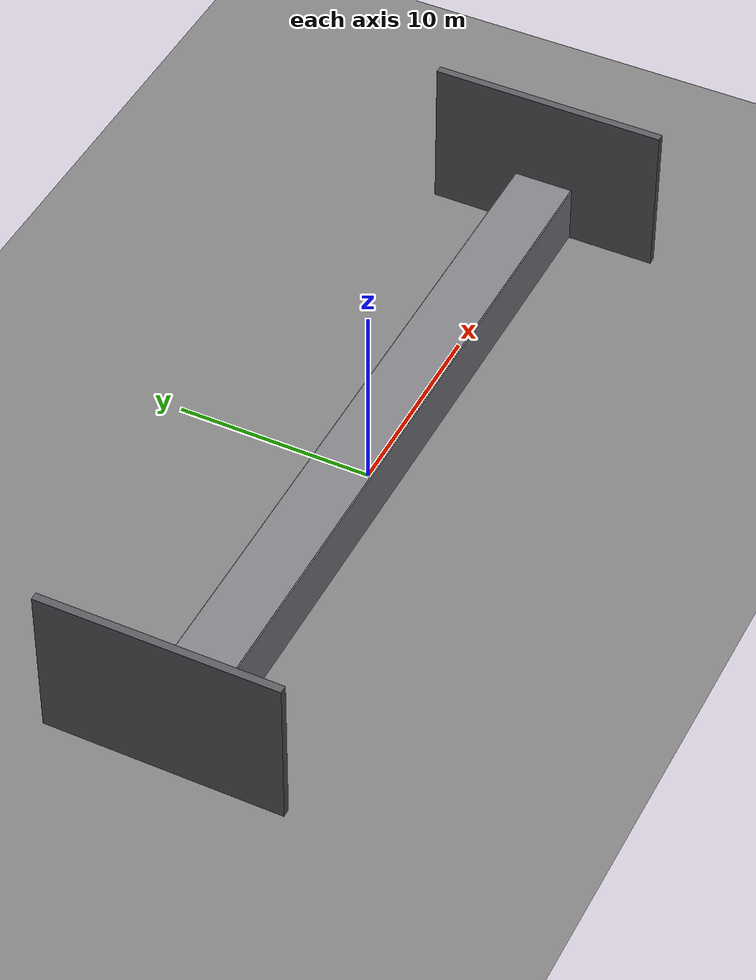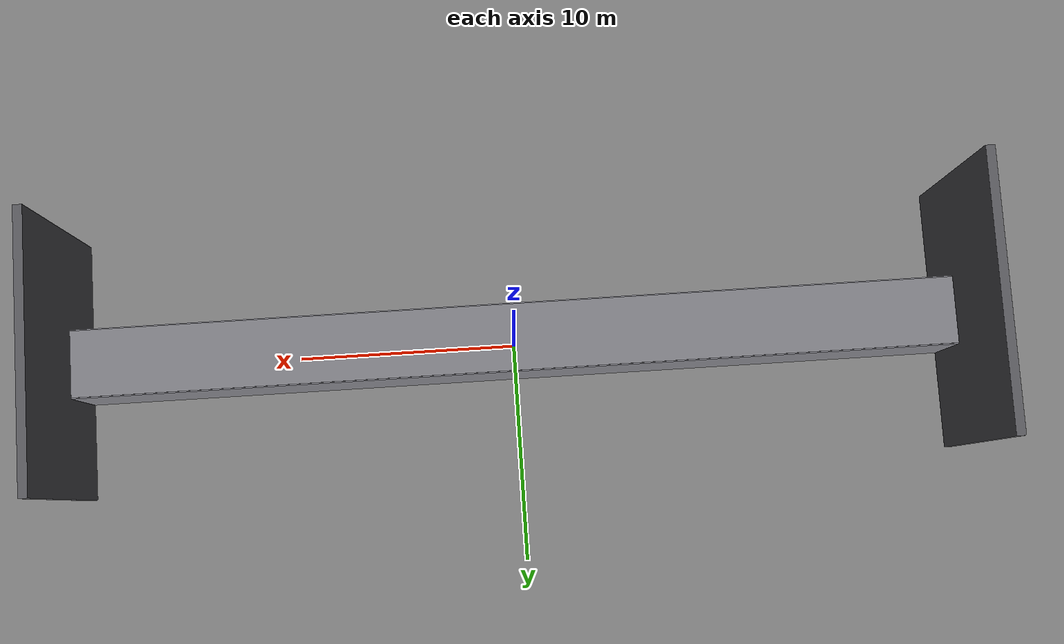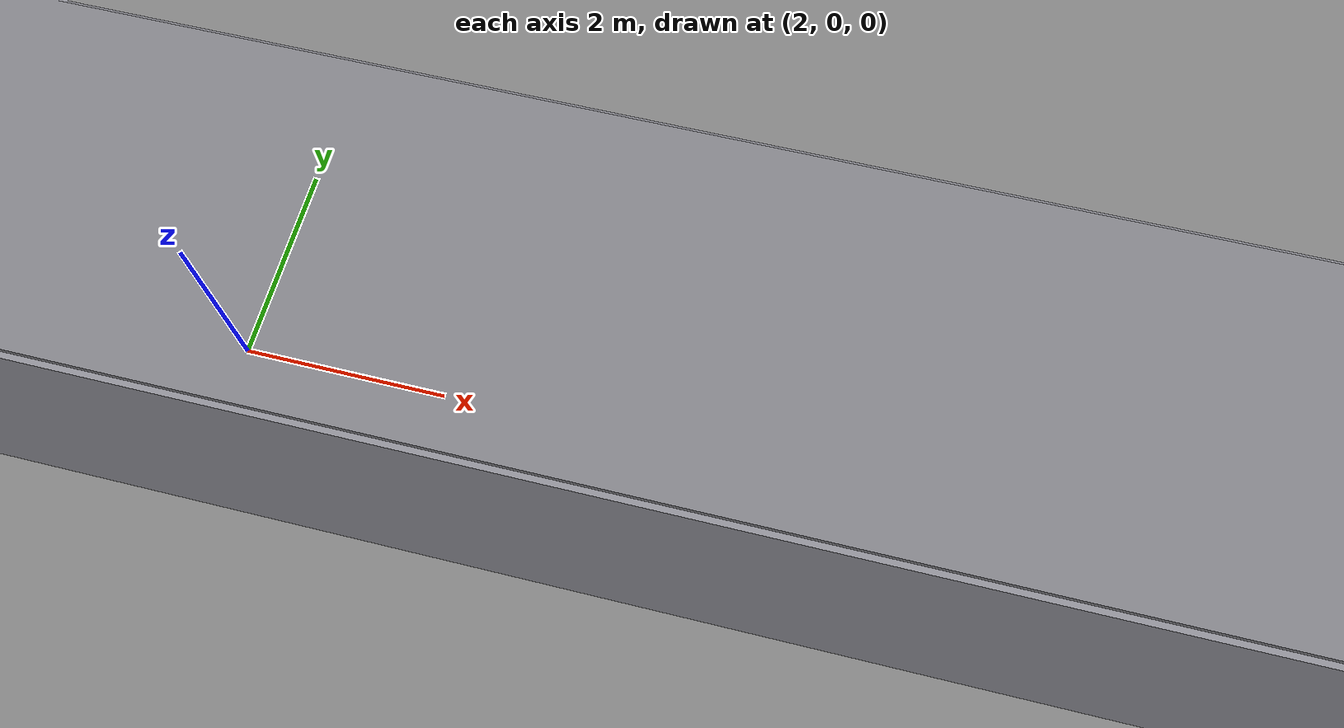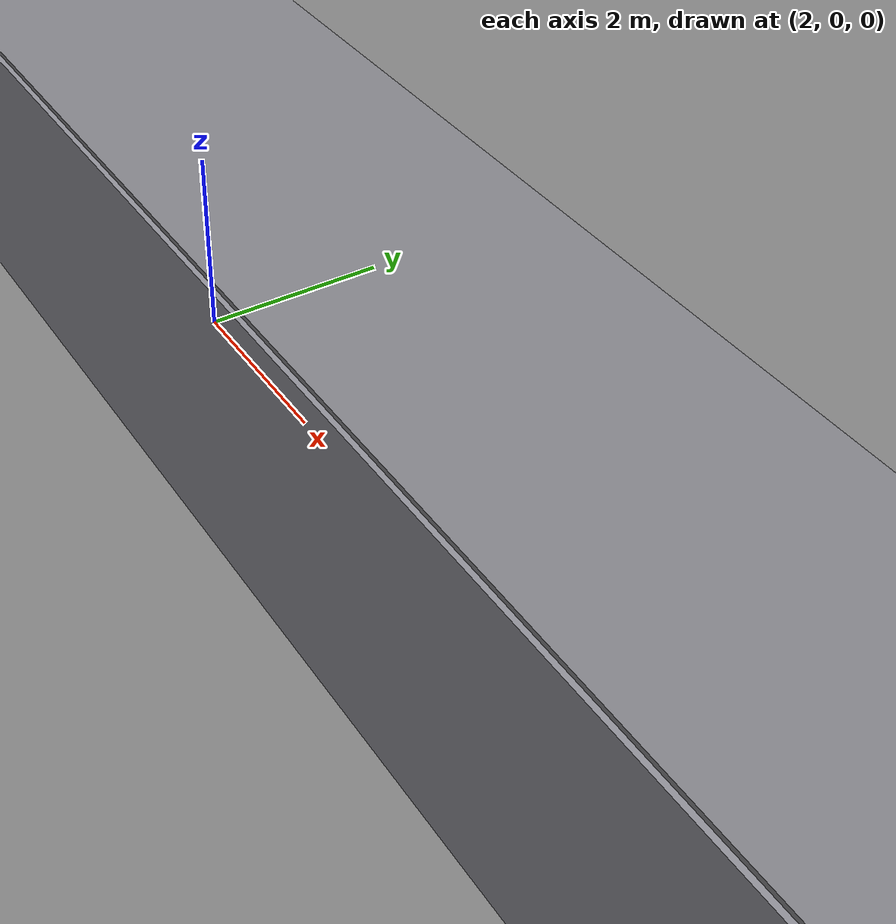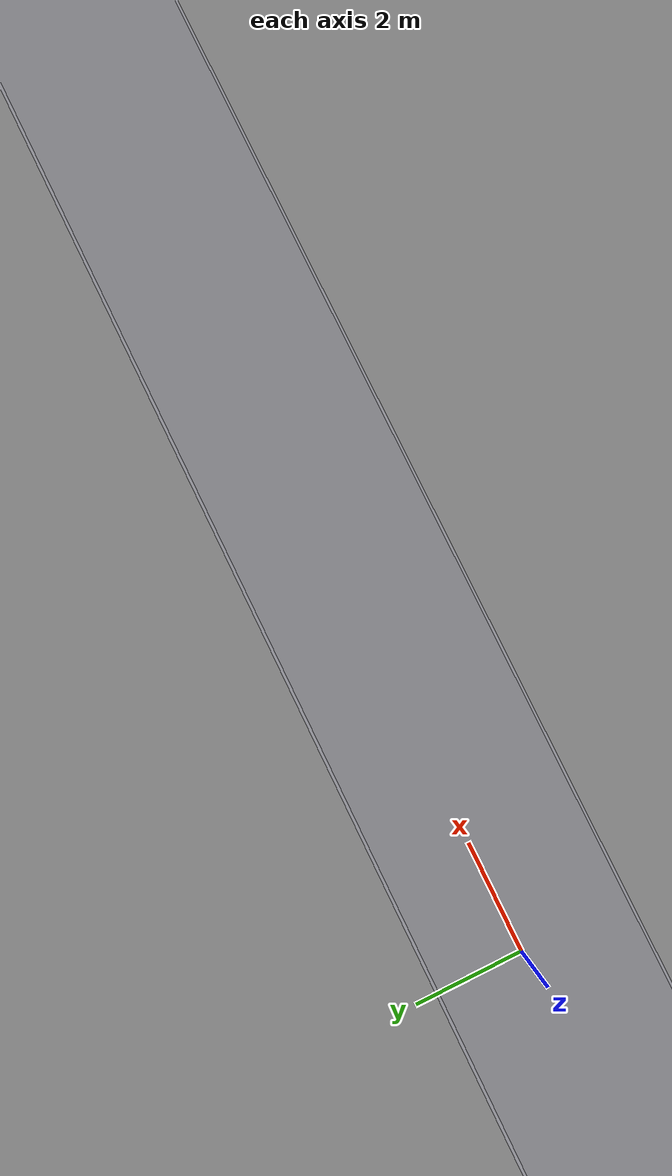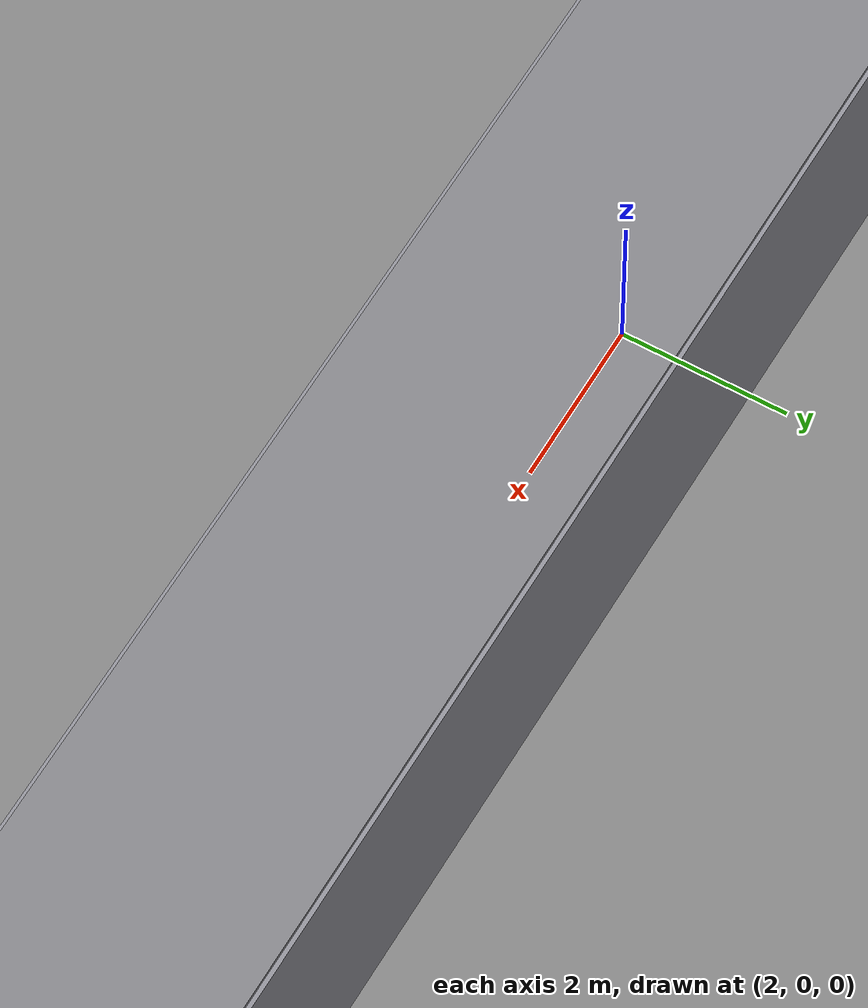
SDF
<?xml version="1.0"?>
<!--
  隧道病害巡检仿真世界
  - 简易矩形隧道走廊: 左墙 + 右墙 + 顶板, 净宽 ~2.5m, 净高 ~2.75m
  - 走廊内放置红/绿/蓝色块与圆柱, 为相机、16线雷达提供丰富特征(供后续 SLAM / 病害检测)
  - 注: 地面与阳光显式定义, 不依赖 model:// 资源路径
-->
<sdf version="1.9">
  <world name="tunnel_world">

    <physics name="default_physics" default="true" type="dart">
      <gravity>0 0 -9.8</gravity>
      <max_step_size>0.002</max_step_size>
      <real_time_factor>1</real_time_factor>
      <real_time_update_rate>500</real_time_update_rate>
    </physics>

    <scene>
      <ambient>0.6 0.6 0.6</ambient>
      <background>0.2 0.2 0.2</background>
      <shadows>true</shadows>
    </scene>

    <plugin filename="gz-sim-sensors-system" name="gz::sim::systems::Sensors">
      <render_engine>ogre2</render_engine>
    </plugin>

    <!-- 关键: world 有 Sensors 等系统插件时, gz-sim 不再自动加载默认系统集(含 Physics)。
         必须显式加 physics-system, 否则物理引擎不创建、实体静止、DiffDrive 永不发 odom。 -->
    <plugin filename="gz-sim-physics-system" name="gz::sim::systems::Physics"/>

    <!-- 太阳(方向光) -->
    <light type="directional" name="sun">
      <cast_shadows>true</cast_shadows>
      <pose>0 0 10 0 0 0</pose>
      <diffuse>0.35 0.35 0.35</diffuse>
      <specular>0.05 0.05 0.05</specular>
      <direction>-0.5 0.1 -0.9</direction>
    </light>

    <!-- 隧道内点光源: 沿隧道每 10m 一盏(z=2.4, range 16)。
         封闭隧道顶挡住太阳直射, 仅靠 scene ambient 会让墙面均匀灰、病害贴图看不清
         (v11-v13t 对比度 std 掉到 10~29 的根源)。点光源制造亮池+暗缝,
         病害 PBR 贴图才能看清。v9/v10 有这组灯, std≈40。 -->
    <light type="point" name="tunnel_light_1">
      <cast_shadows>false</cast_shadows>
      <pose>-15 0 2.4 0 0 0</pose>
      <diffuse>0.5 0.5 0.5</diffuse>
      <specular>0.05 0.05 0.05</specular>
      <attenuation>
        <range>16</range>
        <constant>1.0</constant>
        <linear>0.05</linear>
        <quadratic>0.005</quadratic>
      </attenuation>
      <intensity>1.0</intensity>
    </light>
    <light type="point" name="tunnel_light_2">
      <cast_shadows>false</cast_shadows>
      <pose>-5 0 2.4 0 0 0</pose>
      <diffuse>0.5 0.5 0.5</diffuse>
      <specular>0.05 0.05 0.05</specular>
      <attenuation>
        <range>16</range>
        <constant>1.0</constant>
        <linear>0.05</linear>
        <quadratic>0.005</quadratic>
      </attenuation>
      <intensity>1.0</intensity>
    </light>
    <light type="point" name="tunnel_light_3">
      <cast_shadows>false</cast_shadows>
      <pose>5 0 2.4 0 0 0</pose>
      <diffuse>0.5 0.5 0.5</diffuse>
      <specular>0.05 0.05 0.05</specular>
      <attenuation>
        <range>16</range>
        <constant>1.0</constant>
        <linear>0.05</linear>
        <quadratic>0.005</quadratic>
      </attenuation>
      <intensity>1.0</intensity>
    </light>
    <light type="point" name="tunnel_light_4">
      <cast_shadows>false</cast_shadows>
      <pose>15 0 2.4 0 0 0</pose>
      <diffuse>0.5 0.5 0.5</diffuse>
      <specular>0.05 0.05 0.05</specular>
      <attenuation>
        <range>16</range>
        <constant>1.0</constant>
        <linear>0.05</linear>
        <quadratic>0.005</quadratic>
      </attenuation>
      <intensity>1.0</intensity>
    </light>

    <!-- 地面 -->
    <model name="ground_plane">
      <static>true</static>
      <link name="ground">
        <collision name="ground_collision">
          <geometry>
            <plane><normal>0 0 1</normal><size>100 100</size></plane>
          </geometry>
        </collision>
        <visual name="ground_visual">
          <geometry>
            <plane><normal>0 0 1</normal><size>100 100</size></plane>
          </geometry>
          <material>
  <diffuse>0.50 0.50 0.50 1</diffuse>
  <emissive>0.08 0.08 0.08 1</emissive><ambient>0.5 0.5 0.5</ambient></material>
        </visual>
      </link>
    </model>

    <!-- ============ 隧道左墙 ============ -->
    <model name="tunnel_left_wall">
      <static>true</static>
      <pose>0 1.4 1.5 0 0 0</pose>
      <link name="wall">
        <visual name="wall_visual">
          <geometry><box><size>40 0.3 3</size></box></geometry>
          <material>
  <diffuse>0.55 0.55 0.58 1</diffuse>
  <emissive>0.09 0.09 0.09 1</emissive><ambient>0.55 0.55 0.58</ambient></material>
        </visual>
        <collision name="wall_collision">
          <geometry><box><size>40 0.3 3</size></box></geometry>
        </collision>
      </link>
    </model>

    <!-- ============ 隧道右墙 ============ -->
    <model name="tunnel_right_wall">
      <static>true</static>
      <pose>0 -1.4 1.5 0 0 0</pose>
      <link name="wall">
        <visual name="wall_visual">
          <geometry><box><size>40 0.3 3</size></box></geometry>
          <material>
  <diffuse>0.55 0.55 0.58 1</diffuse>
  <emissive>0.09 0.09 0.09 1</emissive><ambient>0.55 0.55 0.58</ambient></material>
        </visual>
        <collision name="wall_collision">
          <geometry><box><size>40 0.3 3</size></box></geometry>
        </collision>
      </link>
    </model>

    <!-- ============ 隧道顶板 (拱顶近似) ============ -->
    <model name="tunnel_ceiling">
      <static>true</static>
      <pose>0 0 2.9 0 0 0</pose>
      <link name="ceiling">
        <visual name="ceiling_visual">
          <geometry><box><size>40 3 0.3</size></box></geometry>
          <material>
  <diffuse>0.50 0.50 0.52 1</diffuse>
  <emissive>0.08 0.08 0.08 1</emissive><ambient>0.5 0.5 0.52</ambient></material>
        </visual>
        <collision name="ceiling_collision">
          <geometry><box><size>40 3 0.3</size></box></geometry>
        </collision>
      </link>
    </model>

    <!-- ============ 钢轨 (轨道病害载体, 标准轨距 1435mm, 轨顶 z≈0.15) ============ -->
    <model name="rail_left">
      <static>true</static>
      <pose>0 0.717 0.075 0 0 0</pose>
      <link name="rail">
        <visual name="visual">
          <geometry><box><size>40 0.09 0.15</size></box></geometry>
          <material>
            <diffuse>0.72 0.72 0.75 1</diffuse>
            <emissive>0.12 0.12 0.12 1</emissive>
            <ambient>0.72 0.72 0.75</ambient>
          </material>
        </visual>
        <collision name="collision">
          <geometry><box><size>40 0.09 0.15</size></box></geometry>
        </collision>
      </link>
    </model>
    <model name="rail_right">
      <static>true</static>
      <pose>0 -0.717 0.075 0 0 0</pose>
      <link name="rail">
        <visual name="visual">
          <geometry><box><size>40 0.09 0.15</size></box></geometry>
          <material>
            <diffuse>0.72 0.72 0.75 1</diffuse>
            <emissive>0.12 0.12 0.12 1</emissive>
            <ambient>0.72 0.72 0.75</ambient>
          </material>
        </visual>
        <collision name="collision">
          <geometry><box><size>40 0.09 0.15</size></box></geometry>
        </collision>
      </link>
    </model>

    <!-- ============ 隧道端墙 (封住 x=±20 开口, 避免相机看到隧道外天空致盲白屏) ============ -->
    <model name="tunnel_end_wall_far">
      <static>true</static>
      <pose>20 0 3.5 0 0 0</pose>
      <link name="wall">
        <visual name="visual">
          <geometry><box><size>0.4 12 9</size></box></geometry>
          <material>
            <diffuse>0.35 0.35 0.37 1</diffuse>
            <emissive>0.06 0.06 0.06 1</emissive>
            <ambient>0.35 0.35 0.37</ambient>
          </material>
        </visual>
        <collision name="collision">
          <geometry><box><size>0.4 12 9</size></box></geometry>
        </collision>
      </link>
    </model>
    <model name="tunnel_end_wall_near">
      <static>true</static>
      <pose>-20 0 3.5 0 0 0</pose>
      <link name="wall">
        <visual name="visual">
          <geometry><box><size>0.4 12 9</size></box></geometry>
          <material>
            <diffuse>0.35 0.35 0.37 1</diffuse>
            <emissive>0.06 0.06 0.06 1</emissive>
            <ambient>0.35 0.35 0.37</ambient>
          </material>
        </visual>
        <collision name="collision">
          <geometry><box><size>0.4 12 9</size></box></geometry>
        </collision>
      </link>
    </model>

        <!-- ============ 病害模型 (配对数据自动标注真值) ============ -->
    <model name='defect_crack_01'>
      <static>true</static>
      <pose>14.153 1.25 0.87 0 0 0</pose>
      <link name='link'>
        <visual name='visual'>
          <laser_retro>500</laser_retro>
          <geometry><box><size>0.407 0.02 0.385</size></box></geometry>
          <material>
            <ambient>1 1 1 1</ambient>
            <diffuse>1 1 1 1</diffuse>
            <emissive>0.05 0.05 0.05 1</emissive>
            <specular>0.05 0.05 0.05 1</specular>
            <pbr>
              <metal>
                <albedo_map>file:///home/ylf/workspace/inspection_robot/data_gen/textures_data1/crack_8.png</albedo_map>
                <metalness>0.0</metalness>
                <roughness>0.9</roughness>
              </metal>
            </pbr>
          </material>
        </visual>
        <collision name='collision'>
          <geometry><box><size>0.407 0.02 0.385</size></box></geometry>
        </collision>
      </link>
    </model>

    <model name='defect_crack_02'>
      <static>true</static>
      <pose>4.232 1.25 0.946 0 0 0</pose>
      <link name='link'>
        <visual name='visual'>
          <laser_retro>500</laser_retro>
          <geometry><box><size>0.537 0.02 0.211</size></box></geometry>
          <material>
            <ambient>1 1 1 1</ambient>
            <diffuse>1 1 1 1</diffuse>
            <emissive>0.05 0.05 0.05 1</emissive>
            <specular>0.05 0.05 0.05 1</specular>
            <pbr>
              <metal>
                <albedo_map>file:///home/ylf/workspace/inspection_robot/data_gen/textures_data1/crack_19.png</albedo_map>
                <metalness>0.0</metalness>
                <roughness>0.9</roughness>
              </metal>
            </pbr>
          </material>
        </visual>
        <collision name='collision'>
          <geometry><box><size>0.537 0.02 0.211</size></box></geometry>
        </collision>
      </link>
    </model>

    <model name='defect_crack_03'>
      <static>true</static>
      <pose>8.618 -1.25 0.9 0 0 0</pose>
      <link name='link'>
        <visual name='visual'>
          <laser_retro>500</laser_retro>
          <geometry><box><size>0.466 0.02 0.42</size></box></geometry>
          <material>
            <ambient>1 1 1 1</ambient>
            <diffuse>1 1 1 1</diffuse>
            <emissive>0.05 0.05 0.05 1</emissive>
            <specular>0.05 0.05 0.05 1</specular>
            <pbr>
              <metal>
                <albedo_map>file:///home/ylf/workspace/inspection_robot/data_gen/textures_data1/crack_18.png</albedo_map>
                <metalness>0.0</metalness>
                <roughness>0.9</roughness>
              </metal>
            </pbr>
          </material>
        </visual>
        <collision name='collision'>
          <geometry><box><size>0.466 0.02 0.42</size></box></geometry>
        </collision>
      </link>
    </model>

    <model name='defect_crack_04'>
      <static>true</static>
      <pose>7.529 -1.25 1.055 0 0 0</pose>
      <link name='link'>
        <visual name='visual'>
          <laser_retro>500</laser_retro>
          <geometry><box><size>0.49 0.02 0.311</size></box></geometry>
          <material>
            <ambient>1 1 1 1</ambient>
            <diffuse>1 1 1 1</diffuse>
            <emissive>0.05 0.05 0.05 1</emissive>
            <specular>0.05 0.05 0.05 1</specular>
            <pbr>
              <metal>
                <albedo_map>file:///home/ylf/workspace/inspection_robot/data_gen/textures_data1/crack_5.png</albedo_map>
                <metalness>0.0</metalness>
                <roughness>0.9</roughness>
              </metal>
            </pbr>
          </material>
        </visual>
        <collision name='collision'>
          <geometry><box><size>0.49 0.02 0.311</size></box></geometry>
        </collision>
      </link>
    </model>

    <model name='defect_crack_05'>
      <static>true</static>
      <pose>3.364 -1.25 1.076 0 0 0</pose>
      <link name='link'>
        <visual name='visual'>
          <laser_retro>500</laser_retro>
          <geometry><box><size>0.291 0.02 0.254</size></box></geometry>
          <material>
            <ambient>1 1 1 1</ambient>
            <diffuse>1 1 1 1</diffuse>
            <emissive>0.05 0.05 0.05 1</emissive>
            <specular>0.05 0.05 0.05 1</specular>
            <pbr>
              <metal>
                <albedo_map>file:///home/ylf/workspace/inspection_robot/data_gen/textures_data1/crack_12.png</albedo_map>
                <metalness>0.0</metalness>
                <roughness>0.9</roughness>
              </metal>
            </pbr>
          </material>
        </visual>
        <collision name='collision'>
          <geometry><box><size>0.291 0.02 0.254</size></box></geometry>
        </collision>
      </link>
    </model>

    <model name='defect_crack_06'>
      <static>true</static>
      <pose>12.906 -1.25 0.983 0 0 0</pose>
      <link name='link'>
        <visual name='visual'>
          <laser_retro>500</laser_retro>
          <geometry><box><size>0.507 0.02 0.305</size></box></geometry>
          <material>
            <ambient>1 1 1 1</ambient>
            <diffuse>1 1 1 1</diffuse>
            <emissive>0.05 0.05 0.05 1</emissive>
            <specular>0.05 0.05 0.05 1</specular>
            <pbr>
              <metal>
                <albedo_map>file:///home/ylf/workspace/inspection_robot/data_gen/textures_data1/crack_16.png</albedo_map>
                <metalness>0.0</metalness>
                <roughness>0.9</roughness>
              </metal>
            </pbr>
          </material>
        </visual>
        <collision name='collision'>
          <geometry><box><size>0.507 0.02 0.305</size></box></geometry>
        </collision>
      </link>
    </model>

    <model name='defect_crack_07'>
      <static>true</static>
      <pose>9.477 -1.25 0.636 0 0 0</pose>
      <link name='link'>
        <visual name='visual'>
          <laser_retro>500</laser_retro>
          <geometry><box><size>0.372 0.02 0.258</size></box></geometry>
          <material>
            <ambient>1 1 1 1</ambient>
            <diffuse>1 1 1 1</diffuse>
            <emissive>0.05 0.05 0.05 1</emissive>
            <specular>0.05 0.05 0.05 1</specular>
            <pbr>
              <metal>
                <albedo_map>file:///home/ylf/workspace/inspection_robot/data_gen/textures_data1/crack_3.png</albedo_map>
                <metalness>0.0</metalness>
                <roughness>0.9</roughness>
              </metal>
            </pbr>
          </material>
        </visual>
        <collision name='collision'>
          <geometry><box><size>0.372 0.02 0.258</size></box></geometry>
        </collision>
      </link>
    </model>

    <model name='defect_crack_08'>
      <static>true</static>
      <pose>13.99 1.25 0.514 0 0 0</pose>
      <link name='link'>
        <visual name='visual'>
          <laser_retro>500</laser_retro>
          <geometry><box><size>0.547 0.02 0.368</size></box></geometry>
          <material>
            <ambient>1 1 1 1</ambient>
            <diffuse>1 1 1 1</diffuse>
            <emissive>0.05 0.05 0.05 1</emissive>
            <specular>0.05 0.05 0.05 1</specular>
            <pbr>
              <metal>
                <albedo_map>file:///home/ylf/workspace/inspection_robot/data_gen/textures_data1/crack_1.png</albedo_map>
                <metalness>0.0</metalness>
                <roughness>0.9</roughness>
              </metal>
            </pbr>
          </material>
        </visual>
        <collision name='collision'>
          <geometry><box><size>0.547 0.02 0.368</size></box></geometry>
        </collision>
      </link>
    </model>

    <model name='defect_crack_09'>
      <static>true</static>
      <pose>15.505 -1.25 0.9 0 0 0</pose>
      <link name='link'>
        <visual name='visual'>
          <laser_retro>500</laser_retro>
          <geometry><box><size>0.521 0.02 0.342</size></box></geometry>
          <material>
            <ambient>1 1 1 1</ambient>
            <diffuse>1 1 1 1</diffuse>
            <emissive>0.05 0.05 0.05 1</emissive>
            <specular>0.05 0.05 0.05 1</specular>
            <pbr>
              <metal>
                <albedo_map>file:///home/ylf/workspace/inspection_robot/data_gen/textures_data1/crack_15.png</albedo_map>
                <metalness>0.0</metalness>
                <roughness>0.9</roughness>
              </metal>
            </pbr>
          </material>
        </visual>
        <collision name='collision'>
          <geometry><box><size>0.521 0.02 0.342</size></box></geometry>
        </collision>
      </link>
    </model>

    <model name='defect_crack_10'>
      <static>true</static>
      <pose>10.862 1.25 0.487 0 0 0</pose>
      <link name='link'>
        <visual name='visual'>
          <laser_retro>500</laser_retro>
          <geometry><box><size>0.546 0.02 0.267</size></box></geometry>
          <material>
            <ambient>1 1 1 1</ambient>
            <diffuse>1 1 1 1</diffuse>
            <emissive>0.05 0.05 0.05 1</emissive>
            <specular>0.05 0.05 0.05 1</specular>
            <pbr>
              <metal>
                <albedo_map>file:///home/ylf/workspace/inspection_robot/data_gen/textures_data1/crack_14.png</albedo_map>
                <metalness>0.0</metalness>
                <roughness>0.9</roughness>
              </metal>
            </pbr>
          </material>
        </visual>
        <collision name='collision'>
          <geometry><box><size>0.546 0.02 0.267</size></box></geometry>
        </collision>
      </link>
    </model>

    <model name='defect_crack_11'>
      <static>true</static>
      <pose>13.955 -1.25 0.96 0 0 0</pose>
      <link name='link'>
        <visual name='visual'>
          <laser_retro>500</laser_retro>
          <geometry><box><size>0.547 0.02 0.222</size></box></geometry>
          <material>
            <ambient>1 1 1 1</ambient>
            <diffuse>1 1 1 1</diffuse>
            <emissive>0.05 0.05 0.05 1</emissive>
            <specular>0.05 0.05 0.05 1</specular>
            <pbr>
              <metal>
                <albedo_map>file:///home/ylf/workspace/inspection_robot/data_gen/textures_data1/crack_23.png</albedo_map>
                <metalness>0.0</metalness>
                <roughness>0.9</roughness>
              </metal>
            </pbr>
          </material>
        </visual>
        <collision name='collision'>
          <geometry><box><size>0.547 0.02 0.222</size></box></geometry>
        </collision>
      </link>
    </model>

    <model name='defect_crack_12'>
      <static>true</static>
      <pose>14.559 -1.25 0.691 0 0 0</pose>
      <link name='link'>
        <visual name='visual'>
          <laser_retro>500</laser_retro>
          <geometry><box><size>0.256 0.02 0.307</size></box></geometry>
          <material>
            <ambient>1 1 1 1</ambient>
            <diffuse>1 1 1 1</diffuse>
            <emissive>0.05 0.05 0.05 1</emissive>
            <specular>0.05 0.05 0.05 1</specular>
            <pbr>
              <metal>
                <albedo_map>file:///home/ylf/workspace/inspection_robot/data_gen/textures_data1/crack_20.png</albedo_map>
                <metalness>0.0</metalness>
                <roughness>0.9</roughness>
              </metal>
            </pbr>
          </material>
        </visual>
        <collision name='collision'>
          <geometry><box><size>0.256 0.02 0.307</size></box></geometry>
        </collision>
      </link>
    </model>

    <model name='defect_crack_13'>
      <static>true</static>
      <pose>2.619 1.25 0.903 0 0 0</pose>
      <link name='link'>
        <visual name='visual'>
          <laser_retro>500</laser_retro>
          <geometry><box><size>0.434 0.02 0.211</size></box></geometry>
          <material>
            <ambient>1 1 1 1</ambient>
            <diffuse>1 1 1 1</diffuse>
            <emissive>0.05 0.05 0.05 1</emissive>
            <specular>0.05 0.05 0.05 1</specular>
            <pbr>
              <metal>
                <albedo_map>file:///home/ylf/workspace/inspection_robot/data_gen/textures_data1/crack_9.png</albedo_map>
                <metalness>0.0</metalness>
                <roughness>0.9</roughness>
              </metal>
            </pbr>
          </material>
        </visual>
        <collision name='collision'>
          <geometry><box><size>0.434 0.02 0.211</size></box></geometry>
        </collision>
      </link>
    </model>

    <model name='defect_crack_14'>
      <static>true</static>
      <pose>9.712 -1.25 0.565 0 0 0</pose>
      <link name='link'>
        <visual name='visual'>
          <laser_retro>500</laser_retro>
          <geometry><box><size>0.527 0.02 0.27</size></box></geometry>
          <material>
            <ambient>1 1 1 1</ambient>
            <diffuse>1 1 1 1</diffuse>
            <emissive>0.05 0.05 0.05 1</emissive>
            <specular>0.05 0.05 0.05 1</specular>
            <pbr>
              <metal>
                <albedo_map>file:///home/ylf/workspace/inspection_robot/data_gen/textures_data1/crack_4.png</albedo_map>
                <metalness>0.0</metalness>
                <roughness>0.9</roughness>
              </metal>
            </pbr>
          </material>
        </visual>
        <collision name='collision'>
          <geometry><box><size>0.527 0.02 0.27</size></box></geometry>
        </collision>
      </link>
    </model>

    <model name='defect_crack_15'>
      <static>true</static>
      <pose>6.335 1.25 0.422 0 0 0</pose>
      <link name='link'>
        <visual name='visual'>
          <laser_retro>500</laser_retro>
          <geometry><box><size>0.273 0.02 0.35</size></box></geometry>
          <material>
            <ambient>1 1 1 1</ambient>
            <diffuse>1 1 1 1</diffuse>
            <emissive>0.05 0.05 0.05 1</emissive>
            <specular>0.05 0.05 0.05 1</specular>
            <pbr>
              <metal>
                <albedo_map>file:///home/ylf/workspace/inspection_robot/data_gen/textures_data1/crack_10.png</albedo_map>
                <metalness>0.0</metalness>
                <roughness>0.9</roughness>
              </metal>
            </pbr>
          </material>
        </visual>
        <collision name='collision'>
          <geometry><box><size>0.273 0.02 0.35</size></box></geometry>
        </collision>
      </link>
    </model>

    <model name='defect_crack_16'>
      <static>true</static>
      <pose>15.6 1.25 0.883 0 0 0</pose>
      <link name='link'>
        <visual name='visual'>
          <laser_retro>500</laser_retro>
          <geometry><box><size>0.337 0.02 0.266</size></box></geometry>
          <material>
            <ambient>1 1 1 1</ambient>
            <diffuse>1 1 1 1</diffuse>
            <emissive>0.05 0.05 0.05 1</emissive>
            <specular>0.05 0.05 0.05 1</specular>
            <pbr>
              <metal>
                <albedo_map>file:///home/ylf/workspace/inspection_robot/data_gen/textures_data1/crack_13.png</albedo_map>
                <metalness>0.0</metalness>
                <roughness>0.9</roughness>
              </metal>
            </pbr>
          </material>
        </visual>
        <collision name='collision'>
          <geometry><box><size>0.337 0.02 0.266</size></box></geometry>
        </collision>
      </link>
    </model>

    <model name='defect_crack_17'>
      <static>true</static>
      <pose>6.394 -1.25 0.664 0 0 0</pose>
      <link name='link'>
        <visual name='visual'>
          <laser_retro>500</laser_retro>
          <geometry><box><size>0.538 0.02 0.424</size></box></geometry>
          <material>
            <ambient>1 1 1 1</ambient>
            <diffuse>1 1 1 1</diffuse>
            <emissive>0.05 0.05 0.05 1</emissive>
            <specular>0.05 0.05 0.05 1</specular>
            <pbr>
              <metal>
                <albedo_map>file:///home/ylf/workspace/inspection_robot/data_gen/textures_data1/crack_22.png</albedo_map>
                <metalness>0.0</metalness>
                <roughness>0.9</roughness>
              </metal>
            </pbr>
          </material>
        </visual>
        <collision name='collision'>
          <geometry><box><size>0.538 0.02 0.424</size></box></geometry>
        </collision>
      </link>
    </model>

    <model name='defect_crack_18'>
      <static>true</static>
      <pose>14.178 -1.25 0.877 0 0 0</pose>
      <link name='link'>
        <visual name='visual'>
          <laser_retro>500</laser_retro>
          <geometry><box><size>0.366 0.02 0.417</size></box></geometry>
          <material>
            <ambient>1 1 1 1</ambient>
            <diffuse>1 1 1 1</diffuse>
            <emissive>0.05 0.05 0.05 1</emissive>
            <specular>0.05 0.05 0.05 1</specular>
            <pbr>
              <metal>
                <albedo_map>file:///home/ylf/workspace/inspection_robot/data_gen/textures_data1/crack_7.png</albedo_map>
                <metalness>0.0</metalness>
                <roughness>0.9</roughness>
              </metal>
            </pbr>
          </material>
        </visual>
        <collision name='collision'>
          <geometry><box><size>0.366 0.02 0.417</size></box></geometry>
        </collision>
      </link>
    </model>

    <model name='defect_crack_19'>
      <static>true</static>
      <pose>10.682 1.25 0.702 0 0 0</pose>
      <link name='link'>
        <visual name='visual'>
          <laser_retro>500</laser_retro>
          <geometry><box><size>0.532 0.02 0.327</size></box></geometry>
          <material>
            <ambient>1 1 1 1</ambient>
            <diffuse>1 1 1 1</diffuse>
            <emissive>0.05 0.05 0.05 1</emissive>
            <specular>0.05 0.05 0.05 1</specular>
            <pbr>
              <metal>
                <albedo_map>file:///home/ylf/workspace/inspection_robot/data_gen/textures_data1/crack_11.png</albedo_map>
                <metalness>0.0</metalness>
                <roughness>0.9</roughness>
              </metal>
            </pbr>
          </material>
        </visual>
        <collision name='collision'>
          <geometry><box><size>0.532 0.02 0.327</size></box></geometry>
        </collision>
      </link>
    </model>

    <model name='defect_crack_20'>
      <static>true</static>
      <pose>15.11 1.25 0.612 0 0 0</pose>
      <link name='link'>
        <visual name='visual'>
          <laser_retro>500</laser_retro>
          <geometry><box><size>0.381 0.02 0.265</size></box></geometry>
          <material>
            <ambient>1 1 1 1</ambient>
            <diffuse>1 1 1 1</diffuse>
            <emissive>0.05 0.05 0.05 1</emissive>
            <specular>0.05 0.05 0.05 1</specular>
            <pbr>
              <metal>
                <albedo_map>file:///home/ylf/workspace/inspection_robot/data_gen/textures_data1/crack_6.png</albedo_map>
                <metalness>0.0</metalness>
                <roughness>0.9</roughness>
              </metal>
            </pbr>
          </material>
        </visual>
        <collision name='collision'>
          <geometry><box><size>0.381 0.02 0.265</size></box></geometry>
        </collision>
      </link>
    </model>

    <model name='defect_crack_21'>
      <static>true</static>
      <pose>2.16 -1.25 0.414 0 0 0</pose>
      <link name='link'>
        <visual name='visual'>
          <laser_retro>500</laser_retro>
          <geometry><box><size>0.375 0.02 0.345</size></box></geometry>
          <material>
            <ambient>1 1 1 1</ambient>
            <diffuse>1 1 1 1</diffuse>
            <emissive>0.05 0.05 0.05 1</emissive>
            <specular>0.05 0.05 0.05 1</specular>
            <pbr>
              <metal>
                <albedo_map>file:///home/ylf/workspace/inspection_robot/data_gen/textures_data1/crack_17.png</albedo_map>
                <metalness>0.0</metalness>
                <roughness>0.9</roughness>
              </metal>
            </pbr>
          </material>
        </visual>
        <collision name='collision'>
          <geometry><box><size>0.375 0.02 0.345</size></box></geometry>
        </collision>
      </link>
    </model>

    <model name='defect_crack_22'>
      <static>true</static>
      <pose>2.841 1.25 0.875 0 0 0</pose>
      <link name='link'>
        <visual name='visual'>
          <laser_retro>500</laser_retro>
          <geometry><box><size>0.438 0.02 0.317</size></box></geometry>
          <material>
            <ambient>1 1 1 1</ambient>
            <diffuse>1 1 1 1</diffuse>
            <emissive>0.05 0.05 0.05 1</emissive>
            <specular>0.05 0.05 0.05 1</specular>
            <pbr>
              <metal>
                <albedo_map>file:///home/ylf/workspace/inspection_robot/data_gen/textures_data1/crack_21.png</albedo_map>
                <metalness>0.0</metalness>
                <roughness>0.9</roughness>
              </metal>
            </pbr>
          </material>
        </visual>
        <collision name='collision'>
          <geometry><box><size>0.438 0.02 0.317</size></box></geometry>
        </collision>
      </link>
    </model>

    <model name='defect_crack_23'>
      <static>true</static>
      <pose>10.524 -1.25 0.813 0 0 0</pose>
      <link name='link'>
        <visual name='visual'>
          <laser_retro>500</laser_retro>
          <geometry><box><size>0.334 0.02 0.322</size></box></geometry>
          <material>
            <ambient>1 1 1 1</ambient>
            <diffuse>1 1 1 1</diffuse>
            <emissive>0.05 0.05 0.05 1</emissive>
            <specular>0.05 0.05 0.05 1</specular>
            <pbr>
              <metal>
                <albedo_map>file:///home/ylf/workspace/inspection_robot/data_gen/textures_data1/crack_2.png</albedo_map>
                <metalness>0.0</metalness>
                <roughness>0.9</roughness>
              </metal>
            </pbr>
          </material>
        </visual>
        <collision name='collision'>
          <geometry><box><size>0.334 0.02 0.322</size></box></geometry>
        </collision>
      </link>
    </model>

    <model name='defect_equip_bracket_loose_01'>
      <static>true</static>
      <pose>2.411 1.25 0.299 0 0 0</pose>
      <link name='link'>
        <visual name='visual'>
          <laser_retro>760</laser_retro>
          <geometry><box><size>0.209 0.02 0.449</size></box></geometry>
          <material>
            <ambient>1 1 1 1</ambient>
            <diffuse>1 1 1 1</diffuse>
            <emissive>0.05 0.05 0.05 1</emissive>
            <specular>0.05 0.05 0.05 1</specular>
            <pbr>
              <metal>
                <albedo_map>file:///home/ylf/workspace/inspection_robot/data_gen/textures_data1/equip_bracket_loose_12.png</albedo_map>
                <metalness>0.0</metalness>
                <roughness>0.9</roughness>
              </metal>
            </pbr>
          </material>
        </visual>
        <collision name='collision'>
          <geometry><box><size>0.209 0.02 0.449</size></box></geometry>
        </collision>
      </link>
    </model>

    <model name='defect_equip_bracket_loose_02'>
      <static>true</static>
      <pose>15.349 1.25 0.447 0 0 0</pose>
      <link name='link'>
        <visual name='visual'>
          <laser_retro>760</laser_retro>
          <geometry><box><size>0.386 0.02 0.41</size></box></geometry>
          <material>
            <ambient>1 1 1 1</ambient>
            <diffuse>1 1 1 1</diffuse>
            <emissive>0.05 0.05 0.05 1</emissive>
            <specular>0.05 0.05 0.05 1</specular>
            <pbr>
              <metal>
                <albedo_map>file:///home/ylf/workspace/inspection_robot/data_gen/textures_data1/equip_bracket_loose_18.png</albedo_map>
                <metalness>0.0</metalness>
                <roughness>0.9</roughness>
              </metal>
            </pbr>
          </material>
        </visual>
        <collision name='collision'>
          <geometry><box><size>0.386 0.02 0.41</size></box></geometry>
        </collision>
      </link>
    </model>

    <model name='defect_equip_bracket_loose_03'>
      <static>true</static>
      <pose>9.726 -1.25 0.21 0 0 0</pose>
      <link name='link'>
        <visual name='visual'>
          <laser_retro>760</laser_retro>
          <geometry><box><size>0.27 0.02 0.242</size></box></geometry>
          <material>
            <ambient>1 1 1 1</ambient>
            <diffuse>1 1 1 1</diffuse>
            <emissive>0.05 0.05 0.05 1</emissive>
            <specular>0.05 0.05 0.05 1</specular>
            <pbr>
              <metal>
                <albedo_map>file:///home/ylf/workspace/inspection_robot/data_gen/textures_data1/equip_bracket_loose_2.png</albedo_map>
                <metalness>0.0</metalness>
                <roughness>0.9</roughness>
              </metal>
            </pbr>
          </material>
        </visual>
        <collision name='collision'>
          <geometry><box><size>0.27 0.02 0.242</size></box></geometry>
        </collision>
      </link>
    </model>

    <model name='defect_equip_bracket_loose_04'>
      <static>true</static>
      <pose>14.558 1.25 0.599 0 0 0</pose>
      <link name='link'>
        <visual name='visual'>
          <laser_retro>760</laser_retro>
          <geometry><box><size>0.427 0.02 0.317</size></box></geometry>
          <material>
            <ambient>1 1 1 1</ambient>
            <diffuse>1 1 1 1</diffuse>
            <emissive>0.05 0.05 0.05 1</emissive>
            <specular>0.05 0.05 0.05 1</specular>
            <pbr>
              <metal>
                <albedo_map>file:///home/ylf/workspace/inspection_robot/data_gen/textures_data1/equip_bracket_loose_16.png</albedo_map>
                <metalness>0.0</metalness>
                <roughness>0.9</roughness>
              </metal>
            </pbr>
          </material>
        </visual>
        <collision name='collision'>
          <geometry><box><size>0.427 0.02 0.317</size></box></geometry>
        </collision>
      </link>
    </model>

    <model name='defect_equip_bracket_loose_05'>
      <static>true</static>
      <pose>7.195 -1.25 0.244 0 0 0</pose>
      <link name='link'>
        <visual name='visual'>
          <laser_retro>760</laser_retro>
          <geometry><box><size>0.358 0.02 0.273</size></box></geometry>
          <material>
            <ambient>1 1 1 1</ambient>
            <diffuse>1 1 1 1</diffuse>
            <emissive>0.05 0.05 0.05 1</emissive>
            <specular>0.05 0.05 0.05 1</specular>
            <pbr>
              <metal>
                <albedo_map>file:///home/ylf/workspace/inspection_robot/data_gen/textures_data1/equip_bracket_loose_6.png</albedo_map>
                <metalness>0.0</metalness>
                <roughness>0.9</roughness>
              </metal>
            </pbr>
          </material>
        </visual>
        <collision name='collision'>
          <geometry><box><size>0.358 0.02 0.273</size></box></geometry>
        </collision>
      </link>
    </model>

    <model name='defect_equip_bracket_loose_06'>
      <static>true</static>
      <pose>15.89 1.25 0.411 0 0 0</pose>
      <link name='link'>
        <visual name='visual'>
          <laser_retro>760</laser_retro>
          <geometry><box><size>0.337 0.02 0.302</size></box></geometry>
          <material>
            <ambient>1 1 1 1</ambient>
            <diffuse>1 1 1 1</diffuse>
            <emissive>0.05 0.05 0.05 1</emissive>
            <specular>0.05 0.05 0.05 1</specular>
            <pbr>
              <metal>
                <albedo_map>file:///home/ylf/workspace/inspection_robot/data_gen/textures_data1/equip_bracket_loose_8.png</albedo_map>
                <metalness>0.0</metalness>
                <roughness>0.9</roughness>
              </metal>
            </pbr>
          </material>
        </visual>
        <collision name='collision'>
          <geometry><box><size>0.337 0.02 0.302</size></box></geometry>
        </collision>
      </link>
    </model>

    <model name='defect_equip_bracket_loose_07'>
      <static>true</static>
      <pose>5.898 -1.25 0.518 0 0 0</pose>
      <link name='link'>
        <visual name='visual'>
          <laser_retro>760</laser_retro>
          <geometry><box><size>0.264 0.02 0.271</size></box></geometry>
          <material>
            <ambient>1 1 1 1</ambient>
            <diffuse>1 1 1 1</diffuse>
            <emissive>0.05 0.05 0.05 1</emissive>
            <specular>0.05 0.05 0.05 1</specular>
            <pbr>
              <metal>
                <albedo_map>file:///home/ylf/workspace/inspection_robot/data_gen/textures_data1/equip_bracket_loose_1.png</albedo_map>
                <metalness>0.0</metalness>
                <roughness>0.9</roughness>
              </metal>
            </pbr>
          </material>
        </visual>
        <collision name='collision'>
          <geometry><box><size>0.264 0.02 0.271</size></box></geometry>
        </collision>
      </link>
    </model>

    <model name='defect_equip_bracket_loose_08'>
      <static>true</static>
      <pose>3.955 -1.25 0.338 0 0 0</pose>
      <link name='link'>
        <visual name='visual'>
          <laser_retro>760</laser_retro>
          <geometry><box><size>0.209 0.02 0.321</size></box></geometry>
          <material>
            <ambient>1 1 1 1</ambient>
            <diffuse>1 1 1 1</diffuse>
            <emissive>0.05 0.05 0.05 1</emissive>
            <specular>0.05 0.05 0.05 1</specular>
            <pbr>
              <metal>
                <albedo_map>file:///home/ylf/workspace/inspection_robot/data_gen/textures_data1/equip_bracket_loose_9.png</albedo_map>
                <metalness>0.0</metalness>
                <roughness>0.9</roughness>
              </metal>
            </pbr>
          </material>
        </visual>
        <collision name='collision'>
          <geometry><box><size>0.209 0.02 0.321</size></box></geometry>
        </collision>
      </link>
    </model>

    <model name='defect_equip_bracket_loose_09'>
      <static>true</static>
      <pose>15.039 -1.25 0.545 0 0 0</pose>
      <link name='link'>
        <visual name='visual'>
          <laser_retro>760</laser_retro>
          <geometry><box><size>0.353 0.02 0.208</size></box></geometry>
          <material>
            <ambient>1 1 1 1</ambient>
            <diffuse>1 1 1 1</diffuse>
            <emissive>0.05 0.05 0.05 1</emissive>
            <specular>0.05 0.05 0.05 1</specular>
            <pbr>
              <metal>
                <albedo_map>file:///home/ylf/workspace/inspection_robot/data_gen/textures_data1/equip_bracket_loose_14.png</albedo_map>
                <metalness>0.0</metalness>
                <roughness>0.9</roughness>
              </metal>
            </pbr>
          </material>
        </visual>
        <collision name='collision'>
          <geometry><box><size>0.353 0.02 0.208</size></box></geometry>
        </collision>
      </link>
    </model>

    <model name='defect_equip_bracket_loose_10'>
      <static>true</static>
      <pose>8.826 1.25 0.747 0 0 0</pose>
      <link name='link'>
        <visual name='visual'>
          <laser_retro>760</laser_retro>
          <geometry><box><size>0.27 0.02 0.377</size></box></geometry>
          <material>
            <ambient>1 1 1 1</ambient>
            <diffuse>1 1 1 1</diffuse>
            <emissive>0.05 0.05 0.05 1</emissive>
            <specular>0.05 0.05 0.05 1</specular>
            <pbr>
              <metal>
                <albedo_map>file:///home/ylf/workspace/inspection_robot/data_gen/textures_data1/equip_bracket_loose_11.png</albedo_map>
                <metalness>0.0</metalness>
                <roughness>0.9</roughness>
              </metal>
            </pbr>
          </material>
        </visual>
        <collision name='collision'>
          <geometry><box><size>0.27 0.02 0.377</size></box></geometry>
        </collision>
      </link>
    </model>

    <model name='defect_equip_bracket_loose_11'>
      <static>true</static>
      <pose>8.093 1.25 0.492 0 0 0</pose>
      <link name='link'>
        <visual name='visual'>
          <laser_retro>760</laser_retro>
          <geometry><box><size>0.219 0.02 0.208</size></box></geometry>
          <material>
            <ambient>1 1 1 1</ambient>
            <diffuse>1 1 1 1</diffuse>
            <emissive>0.05 0.05 0.05 1</emissive>
            <specular>0.05 0.05 0.05 1</specular>
            <pbr>
              <metal>
                <albedo_map>file:///home/ylf/workspace/inspection_robot/data_gen/textures_data1/equip_bracket_loose_17.png</albedo_map>
                <metalness>0.0</metalness>
                <roughness>0.9</roughness>
              </metal>
            </pbr>
          </material>
        </visual>
        <collision name='collision'>
          <geometry><box><size>0.219 0.02 0.208</size></box></geometry>
        </collision>
      </link>
    </model>

    <model name='defect_equip_bracket_loose_12'>
      <static>true</static>
      <pose>4.731 -1.25 0.43 0 0 0</pose>
      <link name='link'>
        <visual name='visual'>
          <laser_retro>760</laser_retro>
          <geometry><box><size>0.43 0.02 0.245</size></box></geometry>
          <material>
            <ambient>1 1 1 1</ambient>
            <diffuse>1 1 1 1</diffuse>
            <emissive>0.05 0.05 0.05 1</emissive>
            <specular>0.05 0.05 0.05 1</specular>
            <pbr>
              <metal>
                <albedo_map>file:///home/ylf/workspace/inspection_robot/data_gen/textures_data1/equip_bracket_loose_19.png</albedo_map>
                <metalness>0.0</metalness>
                <roughness>0.9</roughness>
              </metal>
            </pbr>
          </material>
        </visual>
        <collision name='collision'>
          <geometry><box><size>0.43 0.02 0.245</size></box></geometry>
        </collision>
      </link>
    </model>

    <model name='defect_equip_bracket_loose_13'>
      <static>true</static>
      <pose>6.427 -1.25 0.766 0 0 0</pose>
      <link name='link'>
        <visual name='visual'>
          <laser_retro>760</laser_retro>
          <geometry><box><size>0.268 0.02 0.437</size></box></geometry>
          <material>
            <ambient>1 1 1 1</ambient>
            <diffuse>1 1 1 1</diffuse>
            <emissive>0.05 0.05 0.05 1</emissive>
            <specular>0.05 0.05 0.05 1</specular>
            <pbr>
              <metal>
                <albedo_map>file:///home/ylf/workspace/inspection_robot/data_gen/textures_data1/equip_bracket_loose_10.png</albedo_map>
                <metalness>0.0</metalness>
                <roughness>0.9</roughness>
              </metal>
            </pbr>
          </material>
        </visual>
        <collision name='collision'>
          <geometry><box><size>0.268 0.02 0.437</size></box></geometry>
        </collision>
      </link>
    </model>

    <model name='defect_equip_bracket_loose_14'>
      <static>true</static>
      <pose>10.548 -1.25 0.45 0 0 0</pose>
      <link name='link'>
        <visual name='visual'>
          <laser_retro>760</laser_retro>
          <geometry><box><size>0.339 0.02 0.209</size></box></geometry>
          <material>
            <ambient>1 1 1 1</ambient>
            <diffuse>1 1 1 1</diffuse>
            <emissive>0.05 0.05 0.05 1</emissive>
            <specular>0.05 0.05 0.05 1</specular>
            <pbr>
              <metal>
                <albedo_map>file:///home/ylf/workspace/inspection_robot/data_gen/textures_data1/equip_bracket_loose_24.png</albedo_map>
                <metalness>0.0</metalness>
                <roughness>0.9</roughness>
              </metal>
            </pbr>
          </material>
        </visual>
        <collision name='collision'>
          <geometry><box><size>0.339 0.02 0.209</size></box></geometry>
        </collision>
      </link>
    </model>

    <model name='defect_equip_bracket_loose_15'>
      <static>true</static>
      <pose>15.722 -1.25 0.32 0 0 0</pose>
      <link name='link'>
        <visual name='visual'>
          <laser_retro>760</laser_retro>
          <geometry><box><size>0.22 0.02 0.257</size></box></geometry>
          <material>
            <ambient>1 1 1 1</ambient>
            <diffuse>1 1 1 1</diffuse>
            <emissive>0.05 0.05 0.05 1</emissive>
            <specular>0.05 0.05 0.05 1</specular>
            <pbr>
              <metal>
                <albedo_map>file:///home/ylf/workspace/inspection_robot/data_gen/textures_data1/equip_bracket_loose_23.png</albedo_map>
                <metalness>0.0</metalness>
                <roughness>0.9</roughness>
              </metal>
            </pbr>
          </material>
        </visual>
        <collision name='collision'>
          <geometry><box><size>0.22 0.02 0.257</size></box></geometry>
        </collision>
      </link>
    </model>

    <model name='defect_equip_bracket_loose_16'>
      <static>true</static>
      <pose>11.775 1.25 0.274 0 0 0</pose>
      <link name='link'>
        <visual name='visual'>
          <laser_retro>760</laser_retro>
          <geometry><box><size>0.229 0.02 0.358</size></box></geometry>
          <material>
            <ambient>1 1 1 1</ambient>
            <diffuse>1 1 1 1</diffuse>
            <emissive>0.05 0.05 0.05 1</emissive>
            <specular>0.05 0.05 0.05 1</specular>
            <pbr>
              <metal>
                <albedo_map>file:///home/ylf/workspace/inspection_robot/data_gen/textures_data1/equip_bracket_loose_20.png</albedo_map>
                <metalness>0.0</metalness>
                <roughness>0.9</roughness>
              </metal>
            </pbr>
          </material>
        </visual>
        <collision name='collision'>
          <geometry><box><size>0.229 0.02 0.358</size></box></geometry>
        </collision>
      </link>
    </model>

    <model name='defect_equip_bracket_loose_17'>
      <static>true</static>
      <pose>15.19 1.25 0.459 0 0 0</pose>
      <link name='link'>
        <visual name='visual'>
          <laser_retro>760</laser_retro>
          <geometry><box><size>0.444 0.02 0.373</size></box></geometry>
          <material>
            <ambient>1 1 1 1</ambient>
            <diffuse>1 1 1 1</diffuse>
            <emissive>0.05 0.05 0.05 1</emissive>
            <specular>0.05 0.05 0.05 1</specular>
            <pbr>
              <metal>
                <albedo_map>file:///home/ylf/workspace/inspection_robot/data_gen/textures_data1/equip_bracket_loose_5.png</albedo_map>
                <metalness>0.0</metalness>
                <roughness>0.9</roughness>
              </metal>
            </pbr>
          </material>
        </visual>
        <collision name='collision'>
          <geometry><box><size>0.444 0.02 0.373</size></box></geometry>
        </collision>
      </link>
    </model>

    <model name='defect_equip_bracket_loose_18'>
      <static>true</static>
      <pose>8.465 -1.25 0.305 0 0 0</pose>
      <link name='link'>
        <visual name='visual'>
          <laser_retro>760</laser_retro>
          <geometry><box><size>0.272 0.02 0.34</size></box></geometry>
          <material>
            <ambient>1 1 1 1</ambient>
            <diffuse>1 1 1 1</diffuse>
            <emissive>0.05 0.05 0.05 1</emissive>
            <specular>0.05 0.05 0.05 1</specular>
            <pbr>
              <metal>
                <albedo_map>file:///home/ylf/workspace/inspection_robot/data_gen/textures_data1/equip_bracket_loose_25.png</albedo_map>
                <metalness>0.0</metalness>
                <roughness>0.9</roughness>
              </metal>
            </pbr>
          </material>
        </visual>
        <collision name='collision'>
          <geometry><box><size>0.272 0.02 0.34</size></box></geometry>
        </collision>
      </link>
    </model>

    <model name='defect_equip_bracket_loose_19'>
      <static>true</static>
      <pose>15.406 -1.25 0.307 0 0 0</pose>
      <link name='link'>
        <visual name='visual'>
          <laser_retro>760</laser_retro>
          <geometry><box><size>0.236 0.02 0.426</size></box></geometry>
          <material>
            <ambient>1 1 1 1</ambient>
            <diffuse>1 1 1 1</diffuse>
            <emissive>0.05 0.05 0.05 1</emissive>
            <specular>0.05 0.05 0.05 1</specular>
            <pbr>
              <metal>
                <albedo_map>file:///home/ylf/workspace/inspection_robot/data_gen/textures_data1/equip_bracket_loose_22.png</albedo_map>
                <metalness>0.0</metalness>
                <roughness>0.9</roughness>
              </metal>
            </pbr>
          </material>
        </visual>
        <collision name='collision'>
          <geometry><box><size>0.236 0.02 0.426</size></box></geometry>
        </collision>
      </link>
    </model>

    <model name='defect_equip_bracket_loose_20'>
      <static>true</static>
      <pose>11.444 -1.25 0.233 0 0 0</pose>
      <link name='link'>
        <visual name='visual'>
          <laser_retro>760</laser_retro>
          <geometry><box><size>0.362 0.02 0.236</size></box></geometry>
          <material>
            <ambient>1 1 1 1</ambient>
            <diffuse>1 1 1 1</diffuse>
            <emissive>0.05 0.05 0.05 1</emissive>
            <specular>0.05 0.05 0.05 1</specular>
            <pbr>
              <metal>
                <albedo_map>file:///home/ylf/workspace/inspection_robot/data_gen/textures_data1/equip_bracket_loose_21.png</albedo_map>
                <metalness>0.0</metalness>
                <roughness>0.9</roughness>
              </metal>
            </pbr>
          </material>
        </visual>
        <collision name='collision'>
          <geometry><box><size>0.362 0.02 0.236</size></box></geometry>
        </collision>
      </link>
    </model>

    <model name='defect_equip_bracket_loose_21'>
      <static>true</static>
      <pose>6.354 1.25 0.288 0 0 0</pose>
      <link name='link'>
        <visual name='visual'>
          <laser_retro>760</laser_retro>
          <geometry><box><size>0.362 0.02 0.233</size></box></geometry>
          <material>
            <ambient>1 1 1 1</ambient>
            <diffuse>1 1 1 1</diffuse>
            <emissive>0.05 0.05 0.05 1</emissive>
            <specular>0.05 0.05 0.05 1</specular>
            <pbr>
              <metal>
                <albedo_map>file:///home/ylf/workspace/inspection_robot/data_gen/textures_data1/equip_bracket_loose_4.png</albedo_map>
                <metalness>0.0</metalness>
                <roughness>0.9</roughness>
              </metal>
            </pbr>
          </material>
        </visual>
        <collision name='collision'>
          <geometry><box><size>0.362 0.02 0.233</size></box></geometry>
        </collision>
      </link>
    </model>

    <model name='defect_equip_bracket_loose_22'>
      <static>true</static>
      <pose>9.486 1.25 0.434 0 0 0</pose>
      <link name='link'>
        <visual name='visual'>
          <laser_retro>760</laser_retro>
          <geometry><box><size>0.296 0.02 0.227</size></box></geometry>
          <material>
            <ambient>1 1 1 1</ambient>
            <diffuse>1 1 1 1</diffuse>
            <emissive>0.05 0.05 0.05 1</emissive>
            <specular>0.05 0.05 0.05 1</specular>
            <pbr>
              <metal>
                <albedo_map>file:///home/ylf/workspace/inspection_robot/data_gen/textures_data1/equip_bracket_loose_13.png</albedo_map>
                <metalness>0.0</metalness>
                <roughness>0.9</roughness>
              </metal>
            </pbr>
          </material>
        </visual>
        <collision name='collision'>
          <geometry><box><size>0.296 0.02 0.227</size></box></geometry>
        </collision>
      </link>
    </model>

    <model name='defect_equip_bracket_loose_23'>
      <static>true</static>
      <pose>5.931 1.25 0.276 0 0 0</pose>
      <link name='link'>
        <visual name='visual'>
          <laser_retro>760</laser_retro>
          <geometry><box><size>0.233 0.02 0.236</size></box></geometry>
          <material>
            <ambient>1 1 1 1</ambient>
            <diffuse>1 1 1 1</diffuse>
            <emissive>0.05 0.05 0.05 1</emissive>
            <specular>0.05 0.05 0.05 1</specular>
            <pbr>
              <metal>
                <albedo_map>file:///home/ylf/workspace/inspection_robot/data_gen/textures_data1/equip_bracket_loose_3.png</albedo_map>
                <metalness>0.0</metalness>
                <roughness>0.9</roughness>
              </metal>
            </pbr>
          </material>
        </visual>
        <collision name='collision'>
          <geometry><box><size>0.233 0.02 0.236</size></box></geometry>
        </collision>
      </link>
    </model>

    <model name='defect_equip_bracket_loose_24'>
      <static>true</static>
      <pose>15.13 -1.25 0.204 0 0 0</pose>
      <link name='link'>
        <visual name='visual'>
          <laser_retro>760</laser_retro>
          <geometry><box><size>0.351 0.02 0.434</size></box></geometry>
          <material>
            <ambient>1 1 1 1</ambient>
            <diffuse>1 1 1 1</diffuse>
            <emissive>0.05 0.05 0.05 1</emissive>
            <specular>0.05 0.05 0.05 1</specular>
            <pbr>
              <metal>
                <albedo_map>file:///home/ylf/workspace/inspection_robot/data_gen/textures_data1/equip_bracket_loose_7.png</albedo_map>
                <metalness>0.0</metalness>
                <roughness>0.9</roughness>
              </metal>
            </pbr>
          </material>
        </visual>
        <collision name='collision'>
          <geometry><box><size>0.351 0.02 0.434</size></box></geometry>
        </collision>
      </link>
    </model>

    <model name='defect_equip_bracket_loose_25'>
      <static>true</static>
      <pose>15.957 -1.25 0.413 0 0 0</pose>
      <link name='link'>
        <visual name='visual'>
          <laser_retro>760</laser_retro>
          <geometry><box><size>0.445 0.02 0.261</size></box></geometry>
          <material>
            <ambient>1 1 1 1</ambient>
            <diffuse>1 1 1 1</diffuse>
            <emissive>0.05 0.05 0.05 1</emissive>
            <specular>0.05 0.05 0.05 1</specular>
            <pbr>
              <metal>
                <albedo_map>file:///home/ylf/workspace/inspection_robot/data_gen/textures_data1/equip_bracket_loose_15.png</albedo_map>
                <metalness>0.0</metalness>
                <roughness>0.9</roughness>
              </metal>
            </pbr>
          </material>
        </visual>
        <collision name='collision'>
          <geometry><box><size>0.445 0.02 0.261</size></box></geometry>
        </collision>
      </link>
    </model>

    <model name='defect_equip_intrusion_01'>
      <static>true</static>
      <pose>10.292 0.32 0.138 0 0 0</pose>
      <link name='link'>
        <visual name='visual'>
          <laser_retro>900</laser_retro>
          <geometry><box><size>0.02 0.251 0.256</size></box></geometry>
          <material>
            <ambient>1 1 1 1</ambient>
            <diffuse>1 1 1 1</diffuse>
            <emissive>0.05 0.05 0.05 1</emissive>
            <specular>0.05 0.05 0.05 1</specular>
            <pbr>
              <metal>
                <albedo_map>file:///home/ylf/workspace/inspection_robot/data_gen/textures_data1/equip_intrusion_9.png</albedo_map>
                <metalness>0.0</metalness>
                <roughness>0.9</roughness>
              </metal>
            </pbr>
          </material>
        </visual>
      </link>
    </model>

    <model name='defect_equip_intrusion_02'>
      <static>true</static>
      <pose>9.042 0.412 0.154 0 0 0</pose>
      <link name='link'>
        <visual name='visual'>
          <laser_retro>900</laser_retro>
          <geometry><box><size>0.02 0.346 0.288</size></box></geometry>
          <material>
            <ambient>1 1 1 1</ambient>
            <diffuse>1 1 1 1</diffuse>
            <emissive>0.05 0.05 0.05 1</emissive>
            <specular>0.05 0.05 0.05 1</specular>
            <pbr>
              <metal>
                <albedo_map>file:///home/ylf/workspace/inspection_robot/data_gen/textures_data1/equip_intrusion_5.png</albedo_map>
                <metalness>0.0</metalness>
                <roughness>0.9</roughness>
              </metal>
            </pbr>
          </material>
        </visual>
      </link>
    </model>

    <model name='defect_equip_intrusion_03'>
      <static>true</static>
      <pose>4.81 -0.477 0.183 0 0 0</pose>
      <link name='link'>
        <visual name='visual'>
          <laser_retro>900</laser_retro>
          <geometry><box><size>0.02 0.445 0.345</size></box></geometry>
          <material>
            <ambient>1 1 1 1</ambient>
            <diffuse>1 1 1 1</diffuse>
            <emissive>0.05 0.05 0.05 1</emissive>
            <specular>0.05 0.05 0.05 1</specular>
            <pbr>
              <metal>
                <albedo_map>file:///home/ylf/workspace/inspection_robot/data_gen/textures_data1/equip_intrusion_1.png</albedo_map>
                <metalness>0.0</metalness>
                <roughness>0.9</roughness>
              </metal>
            </pbr>
          </material>
        </visual>
      </link>
    </model>

    <model name='defect_equip_intrusion_04'>
      <static>true</static>
      <pose>15.161 -0.434 0.165 0 0 0</pose>
      <link name='link'>
        <visual name='visual'>
          <laser_retro>900</laser_retro>
          <geometry><box><size>0.02 0.257 0.311</size></box></geometry>
          <material>
            <ambient>1 1 1 1</ambient>
            <diffuse>1 1 1 1</diffuse>
            <emissive>0.05 0.05 0.05 1</emissive>
            <specular>0.05 0.05 0.05 1</specular>
            <pbr>
              <metal>
                <albedo_map>file:///home/ylf/workspace/inspection_robot/data_gen/textures_data1/equip_intrusion_7.png</albedo_map>
                <metalness>0.0</metalness>
                <roughness>0.9</roughness>
              </metal>
            </pbr>
          </material>
        </visual>
      </link>
    </model>

    <model name='defect_equip_intrusion_05'>
      <static>true</static>
      <pose>3.229 -0.325 0.22 0 0 0</pose>
      <link name='link'>
        <visual name='visual'>
          <laser_retro>900</laser_retro>
          <geometry><box><size>0.02 0.309 0.42</size></box></geometry>
          <material>
            <ambient>1 1 1 1</ambient>
            <diffuse>1 1 1 1</diffuse>
            <emissive>0.05 0.05 0.05 1</emissive>
            <specular>0.05 0.05 0.05 1</specular>
            <pbr>
              <metal>
                <albedo_map>file:///home/ylf/workspace/inspection_robot/data_gen/textures_data1/equip_intrusion_3.png</albedo_map>
                <metalness>0.0</metalness>
                <roughness>0.9</roughness>
              </metal>
            </pbr>
          </material>
        </visual>
      </link>
    </model>

    <model name='defect_equip_intrusion_06'>
      <static>true</static>
      <pose>9.662 -0.389 0.213 0 0 0</pose>
      <link name='link'>
        <visual name='visual'>
          <laser_retro>900</laser_retro>
          <geometry><box><size>0.02 0.357 0.406</size></box></geometry>
          <material>
            <ambient>1 1 1 1</ambient>
            <diffuse>1 1 1 1</diffuse>
            <emissive>0.05 0.05 0.05 1</emissive>
            <specular>0.05 0.05 0.05 1</specular>
            <pbr>
              <metal>
                <albedo_map>file:///home/ylf/workspace/inspection_robot/data_gen/textures_data1/equip_intrusion_6.png</albedo_map>
                <metalness>0.0</metalness>
                <roughness>0.9</roughness>
              </metal>
            </pbr>
          </material>
        </visual>
      </link>
    </model>

    <model name='defect_equip_intrusion_07'>
      <static>true</static>
      <pose>13.699 -0.38 0.227 0 0 0</pose>
      <link name='link'>
        <visual name='visual'>
          <laser_retro>900</laser_retro>
          <geometry><box><size>0.02 0.361 0.435</size></box></geometry>
          <material>
            <ambient>1 1 1 1</ambient>
            <diffuse>1 1 1 1</diffuse>
            <emissive>0.05 0.05 0.05 1</emissive>
            <specular>0.05 0.05 0.05 1</specular>
            <pbr>
              <metal>
                <albedo_map>file:///home/ylf/workspace/inspection_robot/data_gen/textures_data1/equip_intrusion_10.png</albedo_map>
                <metalness>0.0</metalness>
                <roughness>0.9</roughness>
              </metal>
            </pbr>
          </material>
        </visual>
      </link>
    </model>

    <model name='defect_equip_intrusion_08'>
      <static>true</static>
      <pose>8.138 -0.376 0.205 0 0 0</pose>
      <link name='link'>
        <visual name='visual'>
          <laser_retro>900</laser_retro>
          <geometry><box><size>0.02 0.339 0.391</size></box></geometry>
          <material>
            <ambient>1 1 1 1</ambient>
            <diffuse>1 1 1 1</diffuse>
            <emissive>0.05 0.05 0.05 1</emissive>
            <specular>0.05 0.05 0.05 1</specular>
            <pbr>
              <metal>
                <albedo_map>file:///home/ylf/workspace/inspection_robot/data_gen/textures_data1/equip_intrusion_8.png</albedo_map>
                <metalness>0.0</metalness>
                <roughness>0.9</roughness>
              </metal>
            </pbr>
          </material>
        </visual>
      </link>
    </model>

    <model name='defect_equip_intrusion_09'>
      <static>true</static>
      <pose>9.099 0.453 0.227 0 0 0</pose>
      <link name='link'>
        <visual name='visual'>
          <laser_retro>900</laser_retro>
          <geometry><box><size>0.02 0.401 0.433</size></box></geometry>
          <material>
            <ambient>1 1 1 1</ambient>
            <diffuse>1 1 1 1</diffuse>
            <emissive>0.05 0.05 0.05 1</emissive>
            <specular>0.05 0.05 0.05 1</specular>
            <pbr>
              <metal>
                <albedo_map>file:///home/ylf/workspace/inspection_robot/data_gen/textures_data1/equip_intrusion_4.png</albedo_map>
                <metalness>0.0</metalness>
                <roughness>0.9</roughness>
              </metal>
            </pbr>
          </material>
        </visual>
      </link>
    </model>

    <model name='defect_equip_intrusion_10'>
      <static>true</static>
      <pose>2.598 -0.481 0.21 0 0 0</pose>
      <link name='link'>
        <visual name='visual'>
          <laser_retro>900</laser_retro>
          <geometry><box><size>0.02 0.284 0.4</size></box></geometry>
          <material>
            <ambient>1 1 1 1</ambient>
            <diffuse>1 1 1 1</diffuse>
            <emissive>0.05 0.05 0.05 1</emissive>
            <specular>0.05 0.05 0.05 1</specular>
            <pbr>
              <metal>
                <albedo_map>file:///home/ylf/workspace/inspection_robot/data_gen/textures_data1/equip_intrusion_2.png</albedo_map>
                <metalness>0.0</metalness>
                <roughness>0.9</roughness>
              </metal>
            </pbr>
          </material>
        </visual>
      </link>
    </model>

    <model name='defect_leakage_01'>
      <static>true</static>
      <pose>6.589 1.25 0.468 0 0 0</pose>
      <link name='link'>
        <visual name='visual'>
          <laser_retro>300</laser_retro>
          <geometry><box><size>0.639 0.02 0.542</size></box></geometry>
          <material>
            <ambient>1 1 1 1</ambient>
            <diffuse>1 1 1 1</diffuse>
            <emissive>0.05 0.05 0.05 1</emissive>
            <specular>0.05 0.05 0.05 1</specular>
            <pbr>
              <metal>
                <albedo_map>file:///home/ylf/workspace/inspection_robot/data_gen/textures_data1/leakage_22.png</albedo_map>
                <metalness>0.0</metalness>
                <roughness>0.9</roughness>
              </metal>
            </pbr>
          </material>
        </visual>
        <collision name='collision'>
          <geometry><box><size>0.639 0.02 0.542</size></box></geometry>
        </collision>
      </link>
    </model>

    <model name='defect_leakage_02'>
      <static>true</static>
      <pose>15.288 -1.25 0.967 0 0 0</pose>
      <link name='link'>
        <visual name='visual'>
          <laser_retro>300</laser_retro>
          <geometry><box><size>0.637 0.02 0.351</size></box></geometry>
          <material>
            <ambient>1 1 1 1</ambient>
            <diffuse>1 1 1 1</diffuse>
            <emissive>0.05 0.05 0.05 1</emissive>
            <specular>0.05 0.05 0.05 1</specular>
            <pbr>
              <metal>
                <albedo_map>file:///home/ylf/workspace/inspection_robot/data_gen/textures_data1/leakage_1.png</albedo_map>
                <metalness>0.0</metalness>
                <roughness>0.9</roughness>
              </metal>
            </pbr>
          </material>
        </visual>
        <collision name='collision'>
          <geometry><box><size>0.637 0.02 0.351</size></box></geometry>
        </collision>
      </link>
    </model>

    <model name='defect_leakage_03'>
      <static>true</static>
      <pose>3.119 1.25 0.798 0 0 0</pose>
      <link name='link'>
        <visual name='visual'>
          <laser_retro>300</laser_retro>
          <geometry><box><size>0.671 0.02 0.348</size></box></geometry>
          <material>
            <ambient>1 1 1 1</ambient>
            <diffuse>1 1 1 1</diffuse>
            <emissive>0.05 0.05 0.05 1</emissive>
            <specular>0.05 0.05 0.05 1</specular>
            <pbr>
              <metal>
                <albedo_map>file:///home/ylf/workspace/inspection_robot/data_gen/textures_data1/leakage_12.png</albedo_map>
                <metalness>0.0</metalness>
                <roughness>0.9</roughness>
              </metal>
            </pbr>
          </material>
        </visual>
        <collision name='collision'>
          <geometry><box><size>0.671 0.02 0.348</size></box></geometry>
        </collision>
      </link>
    </model>

    <model name='defect_leakage_04'>
      <static>true</static>
      <pose>5.15 -1.25 0.534 0 0 0</pose>
      <link name='link'>
        <visual name='visual'>
          <laser_retro>300</laser_retro>
          <geometry><box><size>0.36 0.02 0.488</size></box></geometry>
          <material>
            <ambient>1 1 1 1</ambient>
            <diffuse>1 1 1 1</diffuse>
            <emissive>0.05 0.05 0.05 1</emissive>
            <specular>0.05 0.05 0.05 1</specular>
            <pbr>
              <metal>
                <albedo_map>file:///home/ylf/workspace/inspection_robot/data_gen/textures_data1/leakage_9.png</albedo_map>
                <metalness>0.0</metalness>
                <roughness>0.9</roughness>
              </metal>
            </pbr>
          </material>
        </visual>
        <collision name='collision'>
          <geometry><box><size>0.36 0.02 0.488</size></box></geometry>
        </collision>
      </link>
    </model>

    <model name='defect_leakage_05'>
      <static>true</static>
      <pose>14.092 1.25 0.46 0 0 0</pose>
      <link name='link'>
        <visual name='visual'>
          <laser_retro>300</laser_retro>
          <geometry><box><size>0.47 0.02 0.623</size></box></geometry>
          <material>
            <ambient>1 1 1 1</ambient>
            <diffuse>1 1 1 1</diffuse>
            <emissive>0.05 0.05 0.05 1</emissive>
            <specular>0.05 0.05 0.05 1</specular>
            <pbr>
              <metal>
                <albedo_map>file:///home/ylf/workspace/inspection_robot/data_gen/textures_data1/leakage_21.png</albedo_map>
                <metalness>0.0</metalness>
                <roughness>0.9</roughness>
              </metal>
            </pbr>
          </material>
        </visual>
        <collision name='collision'>
          <geometry><box><size>0.47 0.02 0.623</size></box></geometry>
        </collision>
      </link>
    </model>

    <model name='defect_leakage_06'>
      <static>true</static>
      <pose>10.253 -1.25 0.995 0 0 0</pose>
      <link name='link'>
        <visual name='visual'>
          <laser_retro>300</laser_retro>
          <geometry><box><size>0.511 0.02 0.483</size></box></geometry>
          <material>
            <ambient>1 1 1 1</ambient>
            <diffuse>1 1 1 1</diffuse>
            <emissive>0.05 0.05 0.05 1</emissive>
            <specular>0.05 0.05 0.05 1</specular>
            <pbr>
              <metal>
                <albedo_map>file:///home/ylf/workspace/inspection_robot/data_gen/textures_data1/leakage_15.png</albedo_map>
                <metalness>0.0</metalness>
                <roughness>0.9</roughness>
              </metal>
            </pbr>
          </material>
        </visual>
        <collision name='collision'>
          <geometry><box><size>0.511 0.02 0.483</size></box></geometry>
        </collision>
      </link>
    </model>

    <model name='defect_leakage_07'>
      <static>true</static>
      <pose>6.849 -1.25 0.687 0 0 0</pose>
      <link name='link'>
        <visual name='visual'>
          <laser_retro>300</laser_retro>
          <geometry><box><size>0.508 0.02 0.439</size></box></geometry>
          <material>
            <ambient>1 1 1 1</ambient>
            <diffuse>1 1 1 1</diffuse>
            <emissive>0.05 0.05 0.05 1</emissive>
            <specular>0.05 0.05 0.05 1</specular>
            <pbr>
              <metal>
                <albedo_map>file:///home/ylf/workspace/inspection_robot/data_gen/textures_data1/leakage_10.png</albedo_map>
                <metalness>0.0</metalness>
                <roughness>0.9</roughness>
              </metal>
            </pbr>
          </material>
        </visual>
        <collision name='collision'>
          <geometry><box><size>0.508 0.02 0.439</size></box></geometry>
        </collision>
      </link>
    </model>

    <model name='defect_leakage_08'>
      <static>true</static>
      <pose>4.184 -1.25 1.016 0 0 0</pose>
      <link name='link'>
        <visual name='visual'>
          <laser_retro>300</laser_retro>
          <geometry><box><size>0.302 0.02 0.674</size></box></geometry>
          <material>
            <ambient>1 1 1 1</ambient>
            <diffuse>1 1 1 1</diffuse>
            <emissive>0.05 0.05 0.05 1</emissive>
            <specular>0.05 0.05 0.05 1</specular>
            <pbr>
              <metal>
                <albedo_map>file:///home/ylf/workspace/inspection_robot/data_gen/textures_data1/leakage_11.png</albedo_map>
                <metalness>0.0</metalness>
                <roughness>0.9</roughness>
              </metal>
            </pbr>
          </material>
        </visual>
        <collision name='collision'>
          <geometry><box><size>0.302 0.02 0.674</size></box></geometry>
        </collision>
      </link>
    </model>

    <model name='defect_leakage_09'>
      <static>true</static>
      <pose>9.824 -1.25 0.423 0 0 0</pose>
      <link name='link'>
        <visual name='visual'>
          <laser_retro>300</laser_retro>
          <geometry><box><size>0.793 0.02 0.573</size></box></geometry>
          <material>
            <ambient>1 1 1 1</ambient>
            <diffuse>1 1 1 1</diffuse>
            <emissive>0.05 0.05 0.05 1</emissive>
            <specular>0.05 0.05 0.05 1</specular>
            <pbr>
              <metal>
                <albedo_map>file:///home/ylf/workspace/inspection_robot/data_gen/textures_data1/leakage_6.png</albedo_map>
                <metalness>0.0</metalness>
                <roughness>0.9</roughness>
              </metal>
            </pbr>
          </material>
        </visual>
        <collision name='collision'>
          <geometry><box><size>0.793 0.02 0.573</size></box></geometry>
        </collision>
      </link>
    </model>

    <model name='defect_leakage_10'>
      <static>true</static>
      <pose>13.714 -1.25 0.602 0 0 0</pose>
      <link name='link'>
        <visual name='visual'>
          <laser_retro>300</laser_retro>
          <geometry><box><size>0.631 0.02 0.484</size></box></geometry>
          <material>
            <ambient>1 1 1 1</ambient>
            <diffuse>1 1 1 1</diffuse>
            <emissive>0.05 0.05 0.05 1</emissive>
            <specular>0.05 0.05 0.05 1</specular>
            <pbr>
              <metal>
                <albedo_map>file:///home/ylf/workspace/inspection_robot/data_gen/textures_data1/leakage_23.png</albedo_map>
                <metalness>0.0</metalness>
                <roughness>0.9</roughness>
              </metal>
            </pbr>
          </material>
        </visual>
        <collision name='collision'>
          <geometry><box><size>0.631 0.02 0.484</size></box></geometry>
        </collision>
      </link>
    </model>

    <model name='defect_leakage_11'>
      <static>true</static>
      <pose>14.456 -1.25 1.08 0 0 0</pose>
      <link name='link'>
        <visual name='visual'>
          <laser_retro>300</laser_retro>
          <geometry><box><size>0.731 0.02 0.636</size></box></geometry>
          <material>
            <ambient>1 1 1 1</ambient>
            <diffuse>1 1 1 1</diffuse>
            <emissive>0.05 0.05 0.05 1</emissive>
            <specular>0.05 0.05 0.05 1</specular>
            <pbr>
              <metal>
                <albedo_map>file:///home/ylf/workspace/inspection_robot/data_gen/textures_data1/leakage_3.png</albedo_map>
                <metalness>0.0</metalness>
                <roughness>0.9</roughness>
              </metal>
            </pbr>
          </material>
        </visual>
        <collision name='collision'>
          <geometry><box><size>0.731 0.02 0.636</size></box></geometry>
        </collision>
      </link>
    </model>

    <model name='defect_leakage_12'>
      <static>true</static>
      <pose>13.343 1.25 0.886 0 0 0</pose>
      <link name='link'>
        <visual name='visual'>
          <laser_retro>300</laser_retro>
          <geometry><box><size>0.323 0.02 0.657</size></box></geometry>
          <material>
            <ambient>1 1 1 1</ambient>
            <diffuse>1 1 1 1</diffuse>
            <emissive>0.05 0.05 0.05 1</emissive>
            <specular>0.05 0.05 0.05 1</specular>
            <pbr>
              <metal>
                <albedo_map>file:///home/ylf/workspace/inspection_robot/data_gen/textures_data1/leakage_17.png</albedo_map>
                <metalness>0.0</metalness>
                <roughness>0.9</roughness>
              </metal>
            </pbr>
          </material>
        </visual>
        <collision name='collision'>
          <geometry><box><size>0.323 0.02 0.657</size></box></geometry>
        </collision>
      </link>
    </model>

    <model name='defect_leakage_13'>
      <static>true</static>
      <pose>14.552 1.25 0.409 0 0 0</pose>
      <link name='link'>
        <visual name='visual'>
          <laser_retro>300</laser_retro>
          <geometry><box><size>0.75 0.02 0.51</size></box></geometry>
          <material>
            <ambient>1 1 1 1</ambient>
            <diffuse>1 1 1 1</diffuse>
            <emissive>0.05 0.05 0.05 1</emissive>
            <specular>0.05 0.05 0.05 1</specular>
            <pbr>
              <metal>
                <albedo_map>file:///home/ylf/workspace/inspection_robot/data_gen/textures_data1/leakage_13.png</albedo_map>
                <metalness>0.0</metalness>
                <roughness>0.9</roughness>
              </metal>
            </pbr>
          </material>
        </visual>
        <collision name='collision'>
          <geometry><box><size>0.75 0.02 0.51</size></box></geometry>
        </collision>
      </link>
    </model>

    <model name='defect_leakage_14'>
      <static>true</static>
      <pose>4.406 1.25 0.767 0 0 0</pose>
      <link name='link'>
        <visual name='visual'>
          <laser_retro>300</laser_retro>
          <geometry><box><size>0.45 0.02 0.548</size></box></geometry>
          <material>
            <ambient>1 1 1 1</ambient>
            <diffuse>1 1 1 1</diffuse>
            <emissive>0.05 0.05 0.05 1</emissive>
            <specular>0.05 0.05 0.05 1</specular>
            <pbr>
              <metal>
                <albedo_map>file:///home/ylf/workspace/inspection_robot/data_gen/textures_data1/leakage_14.png</albedo_map>
                <metalness>0.0</metalness>
                <roughness>0.9</roughness>
              </metal>
            </pbr>
          </material>
        </visual>
        <collision name='collision'>
          <geometry><box><size>0.45 0.02 0.548</size></box></geometry>
        </collision>
      </link>
    </model>

    <model name='defect_leakage_15'>
      <static>true</static>
      <pose>2.745 -1.25 0.488 0 0 0</pose>
      <link name='link'>
        <visual name='visual'>
          <laser_retro>300</laser_retro>
          <geometry><box><size>0.757 0.02 0.301</size></box></geometry>
          <material>
            <ambient>1 1 1 1</ambient>
            <diffuse>1 1 1 1</diffuse>
            <emissive>0.05 0.05 0.05 1</emissive>
            <specular>0.05 0.05 0.05 1</specular>
            <pbr>
              <metal>
                <albedo_map>file:///home/ylf/workspace/inspection_robot/data_gen/textures_data1/leakage_19.png</albedo_map>
                <metalness>0.0</metalness>
                <roughness>0.9</roughness>
              </metal>
            </pbr>
          </material>
        </visual>
        <collision name='collision'>
          <geometry><box><size>0.757 0.02 0.301</size></box></geometry>
        </collision>
      </link>
    </model>

    <model name='defect_leakage_16'>
      <static>true</static>
      <pose>13.362 -1.25 0.486 0 0 0</pose>
      <link name='link'>
        <visual name='visual'>
          <laser_retro>300</laser_retro>
          <geometry><box><size>0.331 0.02 0.349</size></box></geometry>
          <material>
            <ambient>1 1 1 1</ambient>
            <diffuse>1 1 1 1</diffuse>
            <emissive>0.05 0.05 0.05 1</emissive>
            <specular>0.05 0.05 0.05 1</specular>
            <pbr>
              <metal>
                <albedo_map>file:///home/ylf/workspace/inspection_robot/data_gen/textures_data1/leakage_5.png</albedo_map>
                <metalness>0.0</metalness>
                <roughness>0.9</roughness>
              </metal>
            </pbr>
          </material>
        </visual>
        <collision name='collision'>
          <geometry><box><size>0.331 0.02 0.349</size></box></geometry>
        </collision>
      </link>
    </model>

    <model name='defect_leakage_17'>
      <static>true</static>
      <pose>4.398 1.25 0.964 0 0 0</pose>
      <link name='link'>
        <visual name='visual'>
          <laser_retro>300</laser_retro>
          <geometry><box><size>0.696 0.02 0.665</size></box></geometry>
          <material>
            <ambient>1 1 1 1</ambient>
            <diffuse>1 1 1 1</diffuse>
            <emissive>0.05 0.05 0.05 1</emissive>
            <specular>0.05 0.05 0.05 1</specular>
            <pbr>
              <metal>
                <albedo_map>file:///home/ylf/workspace/inspection_robot/data_gen/textures_data1/leakage_18.png</albedo_map>
                <metalness>0.0</metalness>
                <roughness>0.9</roughness>
              </metal>
            </pbr>
          </material>
        </visual>
        <collision name='collision'>
          <geometry><box><size>0.696 0.02 0.665</size></box></geometry>
        </collision>
      </link>
    </model>

    <model name='defect_leakage_18'>
      <static>true</static>
      <pose>8.825 1.25 0.93 0 0 0</pose>
      <link name='link'>
        <visual name='visual'>
          <laser_retro>300</laser_retro>
          <geometry><box><size>0.585 0.02 0.43</size></box></geometry>
          <material>
            <ambient>1 1 1 1</ambient>
            <diffuse>1 1 1 1</diffuse>
            <emissive>0.05 0.05 0.05 1</emissive>
            <specular>0.05 0.05 0.05 1</specular>
            <pbr>
              <metal>
                <albedo_map>file:///home/ylf/workspace/inspection_robot/data_gen/textures_data1/leakage_7.png</albedo_map>
                <metalness>0.0</metalness>
                <roughness>0.9</roughness>
              </metal>
            </pbr>
          </material>
        </visual>
        <collision name='collision'>
          <geometry><box><size>0.585 0.02 0.43</size></box></geometry>
        </collision>
      </link>
    </model>

    <model name='defect_leakage_19'>
      <static>true</static>
      <pose>5.76 1.25 0.731 0 0 0</pose>
      <link name='link'>
        <visual name='visual'>
          <laser_retro>300</laser_retro>
          <geometry><box><size>0.564 0.02 0.44</size></box></geometry>
          <material>
            <ambient>1 1 1 1</ambient>
            <diffuse>1 1 1 1</diffuse>
            <emissive>0.05 0.05 0.05 1</emissive>
            <specular>0.05 0.05 0.05 1</specular>
            <pbr>
              <metal>
                <albedo_map>file:///home/ylf/workspace/inspection_robot/data_gen/textures_data1/leakage_24.png</albedo_map>
                <metalness>0.0</metalness>
                <roughness>0.9</roughness>
              </metal>
            </pbr>
          </material>
        </visual>
        <collision name='collision'>
          <geometry><box><size>0.564 0.02 0.44</size></box></geometry>
        </collision>
      </link>
    </model>

    <model name='defect_leakage_20'>
      <static>true</static>
      <pose>13.998 1.25 0.435 0 0 0</pose>
      <link name='link'>
        <visual name='visual'>
          <laser_retro>300</laser_retro>
          <geometry><box><size>0.688 0.02 0.271</size></box></geometry>
          <material>
            <ambient>1 1 1 1</ambient>
            <diffuse>1 1 1 1</diffuse>
            <emissive>0.05 0.05 0.05 1</emissive>
            <specular>0.05 0.05 0.05 1</specular>
            <pbr>
              <metal>
                <albedo_map>file:///home/ylf/workspace/inspection_robot/data_gen/textures_data1/leakage_8.png</albedo_map>
                <metalness>0.0</metalness>
                <roughness>0.9</roughness>
              </metal>
            </pbr>
          </material>
        </visual>
        <collision name='collision'>
          <geometry><box><size>0.688 0.02 0.271</size></box></geometry>
        </collision>
      </link>
    </model>

    <model name='defect_leakage_21'>
      <static>true</static>
      <pose>15.646 -1.25 0.751 0 0 0</pose>
      <link name='link'>
        <visual name='visual'>
          <laser_retro>300</laser_retro>
          <geometry><box><size>0.727 0.02 0.289</size></box></geometry>
          <material>
            <ambient>1 1 1 1</ambient>
            <diffuse>1 1 1 1</diffuse>
            <emissive>0.05 0.05 0.05 1</emissive>
            <specular>0.05 0.05 0.05 1</specular>
            <pbr>
              <metal>
                <albedo_map>file:///home/ylf/workspace/inspection_robot/data_gen/textures_data1/leakage_25.png</albedo_map>
                <metalness>0.0</metalness>
                <roughness>0.9</roughness>
              </metal>
            </pbr>
          </material>
        </visual>
        <collision name='collision'>
          <geometry><box><size>0.727 0.02 0.289</size></box></geometry>
        </collision>
      </link>
    </model>

    <model name='defect_leakage_22'>
      <static>true</static>
      <pose>4.199 -1.25 0.673 0 0 0</pose>
      <link name='link'>
        <visual name='visual'>
          <laser_retro>300</laser_retro>
          <geometry><box><size>0.336 0.02 0.424</size></box></geometry>
          <material>
            <ambient>1 1 1 1</ambient>
            <diffuse>1 1 1 1</diffuse>
            <emissive>0.05 0.05 0.05 1</emissive>
            <specular>0.05 0.05 0.05 1</specular>
            <pbr>
              <metal>
                <albedo_map>file:///home/ylf/workspace/inspection_robot/data_gen/textures_data1/leakage_2.png</albedo_map>
                <metalness>0.0</metalness>
                <roughness>0.9</roughness>
              </metal>
            </pbr>
          </material>
        </visual>
        <collision name='collision'>
          <geometry><box><size>0.336 0.02 0.424</size></box></geometry>
        </collision>
      </link>
    </model>

    <model name='defect_leakage_23'>
      <static>true</static>
      <pose>7.052 -1.25 0.487 0 0 0</pose>
      <link name='link'>
        <visual name='visual'>
          <laser_retro>300</laser_retro>
          <geometry><box><size>0.396 0.02 0.398</size></box></geometry>
          <material>
            <ambient>1 1 1 1</ambient>
            <diffuse>1 1 1 1</diffuse>
            <emissive>0.05 0.05 0.05 1</emissive>
            <specular>0.05 0.05 0.05 1</specular>
            <pbr>
              <metal>
                <albedo_map>file:///home/ylf/workspace/inspection_robot/data_gen/textures_data1/leakage_4.png</albedo_map>
                <metalness>0.0</metalness>
                <roughness>0.9</roughness>
              </metal>
            </pbr>
          </material>
        </visual>
        <collision name='collision'>
          <geometry><box><size>0.396 0.02 0.398</size></box></geometry>
        </collision>
      </link>
    </model>

    <model name='defect_leakage_24'>
      <static>true</static>
      <pose>12.025 1.25 0.525 0 0 0</pose>
      <link name='link'>
        <visual name='visual'>
          <laser_retro>300</laser_retro>
          <geometry><box><size>0.49 0.02 0.286</size></box></geometry>
          <material>
            <ambient>1 1 1 1</ambient>
            <diffuse>1 1 1 1</diffuse>
            <emissive>0.05 0.05 0.05 1</emissive>
            <specular>0.05 0.05 0.05 1</specular>
            <pbr>
              <metal>
                <albedo_map>file:///home/ylf/workspace/inspection_robot/data_gen/textures_data1/leakage_16.png</albedo_map>
                <metalness>0.0</metalness>
                <roughness>0.9</roughness>
              </metal>
            </pbr>
          </material>
        </visual>
        <collision name='collision'>
          <geometry><box><size>0.49 0.02 0.286</size></box></geometry>
        </collision>
      </link>
    </model>

    <model name='defect_leakage_25'>
      <static>true</static>
      <pose>8.451 -1.25 0.846 0 0 0</pose>
      <link name='link'>
        <visual name='visual'>
          <laser_retro>300</laser_retro>
          <geometry><box><size>0.625 0.02 0.494</size></box></geometry>
          <material>
            <ambient>1 1 1 1</ambient>
            <diffuse>1 1 1 1</diffuse>
            <emissive>0.05 0.05 0.05 1</emissive>
            <specular>0.05 0.05 0.05 1</specular>
            <pbr>
              <metal>
                <albedo_map>file:///home/ylf/workspace/inspection_robot/data_gen/textures_data1/leakage_20.png</albedo_map>
                <metalness>0.0</metalness>
                <roughness>0.9</roughness>
              </metal>
            </pbr>
          </material>
        </visual>
        <collision name='collision'>
          <geometry><box><size>0.625 0.02 0.494</size></box></geometry>
        </collision>
      </link>
    </model>

    <model name='defect_rail_fastener_broken_01'>
      <static>true</static>
      <pose>8.498 0.717 0.276 0 0 0</pose>
      <link name='link'>
        <visual name='visual'>
          <laser_retro>450</laser_retro>
          <geometry><box><size>0.02 0.137 0.241</size></box></geometry>
          <material>
            <ambient>1 1 1 1</ambient>
            <diffuse>1 1 1 1</diffuse>
            <emissive>0.05 0.05 0.05 1</emissive>
            <specular>0.05 0.05 0.05 1</specular>
            <pbr>
              <metal>
                <albedo_map>file:///home/ylf/workspace/inspection_robot/data_gen/textures_data1/rail_fastener_broken_2.png</albedo_map>
                <metalness>0.0</metalness>
                <roughness>0.9</roughness>
              </metal>
            </pbr>
          </material>
        </visual>
      </link>
    </model>

    <model name='defect_rail_fastener_broken_02'>
      <static>true</static>
      <pose>11.346 -0.717 0.263 0 0 0</pose>
      <link name='link'>
        <visual name='visual'>
          <laser_retro>450</laser_retro>
          <geometry><box><size>0.02 0.174 0.216</size></box></geometry>
          <material>
            <ambient>1 1 1 1</ambient>
            <diffuse>1 1 1 1</diffuse>
            <emissive>0.05 0.05 0.05 1</emissive>
            <specular>0.05 0.05 0.05 1</specular>
            <pbr>
              <metal>
                <albedo_map>file:///home/ylf/workspace/inspection_robot/data_gen/textures_data1/rail_fastener_broken_20.png</albedo_map>
                <metalness>0.0</metalness>
                <roughness>0.9</roughness>
              </metal>
            </pbr>
          </material>
        </visual>
      </link>
    </model>

    <model name='defect_rail_fastener_broken_03'>
      <static>true</static>
      <pose>13.363 0.717 0.259 0 0 0</pose>
      <link name='link'>
        <visual name='visual'>
          <laser_retro>450</laser_retro>
          <geometry><box><size>0.02 0.173 0.207</size></box></geometry>
          <material>
            <ambient>1 1 1 1</ambient>
            <diffuse>1 1 1 1</diffuse>
            <emissive>0.05 0.05 0.05 1</emissive>
            <specular>0.05 0.05 0.05 1</specular>
            <pbr>
              <metal>
                <albedo_map>file:///home/ylf/workspace/inspection_robot/data_gen/textures_data1/rail_fastener_broken_14.png</albedo_map>
                <metalness>0.0</metalness>
                <roughness>0.9</roughness>
              </metal>
            </pbr>
          </material>
        </visual>
      </link>
    </model>

    <model name='defect_rail_fastener_broken_04'>
      <static>true</static>
      <pose>12.84 0.717 0.24 0 0 0</pose>
      <link name='link'>
        <visual name='visual'>
          <laser_retro>450</laser_retro>
          <geometry><box><size>0.02 0.133 0.169</size></box></geometry>
          <material>
            <ambient>1 1 1 1</ambient>
            <diffuse>1 1 1 1</diffuse>
            <emissive>0.05 0.05 0.05 1</emissive>
            <specular>0.05 0.05 0.05 1</specular>
            <pbr>
              <metal>
                <albedo_map>file:///home/ylf/workspace/inspection_robot/data_gen/textures_data1/rail_fastener_broken_25.png</albedo_map>
                <metalness>0.0</metalness>
                <roughness>0.9</roughness>
              </metal>
            </pbr>
          </material>
        </visual>
      </link>
    </model>

    <model name='defect_rail_fastener_broken_05'>
      <static>true</static>
      <pose>11.229 0.717 0.276 0 0 0</pose>
      <link name='link'>
        <visual name='visual'>
          <laser_retro>450</laser_retro>
          <geometry><box><size>0.02 0.153 0.242</size></box></geometry>
          <material>
            <ambient>1 1 1 1</ambient>
            <diffuse>1 1 1 1</diffuse>
            <emissive>0.05 0.05 0.05 1</emissive>
            <specular>0.05 0.05 0.05 1</specular>
            <pbr>
              <metal>
                <albedo_map>file:///home/ylf/workspace/inspection_robot/data_gen/textures_data1/rail_fastener_broken_12.png</albedo_map>
                <metalness>0.0</metalness>
                <roughness>0.9</roughness>
              </metal>
            </pbr>
          </material>
        </visual>
      </link>
    </model>

    <model name='defect_rail_fastener_broken_06'>
      <static>true</static>
      <pose>13.781 -0.717 0.277 0 0 0</pose>
      <link name='link'>
        <visual name='visual'>
          <laser_retro>450</laser_retro>
          <geometry><box><size>0.02 0.137 0.244</size></box></geometry>
          <material>
            <ambient>1 1 1 1</ambient>
            <diffuse>1 1 1 1</diffuse>
            <emissive>0.05 0.05 0.05 1</emissive>
            <specular>0.05 0.05 0.05 1</specular>
            <pbr>
              <metal>
                <albedo_map>file:///home/ylf/workspace/inspection_robot/data_gen/textures_data1/rail_fastener_broken_16.png</albedo_map>
                <metalness>0.0</metalness>
                <roughness>0.9</roughness>
              </metal>
            </pbr>
          </material>
        </visual>
      </link>
    </model>

    <model name='defect_rail_fastener_broken_07'>
      <static>true</static>
      <pose>13.707 -0.717 0.264 0 0 0</pose>
      <link name='link'>
        <visual name='visual'>
          <laser_retro>450</laser_retro>
          <geometry><box><size>0.02 0.187 0.218</size></box></geometry>
          <material>
            <ambient>1 1 1 1</ambient>
            <diffuse>1 1 1 1</diffuse>
            <emissive>0.05 0.05 0.05 1</emissive>
            <specular>0.05 0.05 0.05 1</specular>
            <pbr>
              <metal>
                <albedo_map>file:///home/ylf/workspace/inspection_robot/data_gen/textures_data1/rail_fastener_broken_11.png</albedo_map>
                <metalness>0.0</metalness>
                <roughness>0.9</roughness>
              </metal>
            </pbr>
          </material>
        </visual>
      </link>
    </model>

    <model name='defect_rail_fastener_broken_08'>
      <static>true</static>
      <pose>2.508 0.717 0.261 0 0 0</pose>
      <link name='link'>
        <visual name='visual'>
          <laser_retro>450</laser_retro>
          <geometry><box><size>0.02 0.176 0.211</size></box></geometry>
          <material>
            <ambient>1 1 1 1</ambient>
            <diffuse>1 1 1 1</diffuse>
            <emissive>0.05 0.05 0.05 1</emissive>
            <specular>0.05 0.05 0.05 1</specular>
            <pbr>
              <metal>
                <albedo_map>file:///home/ylf/workspace/inspection_robot/data_gen/textures_data1/rail_fastener_broken_23.png</albedo_map>
                <metalness>0.0</metalness>
                <roughness>0.9</roughness>
              </metal>
            </pbr>
          </material>
        </visual>
      </link>
    </model>

    <model name='defect_rail_fastener_broken_09'>
      <static>true</static>
      <pose>3.494 0.717 0.282 0 0 0</pose>
      <link name='link'>
        <visual name='visual'>
          <laser_retro>450</laser_retro>
          <geometry><box><size>0.02 0.175 0.253</size></box></geometry>
          <material>
            <ambient>1 1 1 1</ambient>
            <diffuse>1 1 1 1</diffuse>
            <emissive>0.05 0.05 0.05 1</emissive>
            <specular>0.05 0.05 0.05 1</specular>
            <pbr>
              <metal>
                <albedo_map>file:///home/ylf/workspace/inspection_robot/data_gen/textures_data1/rail_fastener_broken_18.png</albedo_map>
                <metalness>0.0</metalness>
                <roughness>0.9</roughness>
              </metal>
            </pbr>
          </material>
        </visual>
      </link>
    </model>

    <model name='defect_rail_fastener_broken_10'>
      <static>true</static>
      <pose>9.702 0.717 0.244 0 0 0</pose>
      <link name='link'>
        <visual name='visual'>
          <laser_retro>450</laser_retro>
          <geometry><box><size>0.02 0.182 0.178</size></box></geometry>
          <material>
            <ambient>1 1 1 1</ambient>
            <diffuse>1 1 1 1</diffuse>
            <emissive>0.05 0.05 0.05 1</emissive>
            <specular>0.05 0.05 0.05 1</specular>
            <pbr>
              <metal>
                <albedo_map>file:///home/ylf/workspace/inspection_robot/data_gen/textures_data1/rail_fastener_broken_15.png</albedo_map>
                <metalness>0.0</metalness>
                <roughness>0.9</roughness>
              </metal>
            </pbr>
          </material>
        </visual>
      </link>
    </model>

    <model name='defect_rail_fastener_broken_11'>
      <static>true</static>
      <pose>5.39 0.717 0.247 0 0 0</pose>
      <link name='link'>
        <visual name='visual'>
          <laser_retro>450</laser_retro>
          <geometry><box><size>0.02 0.141 0.185</size></box></geometry>
          <material>
            <ambient>1 1 1 1</ambient>
            <diffuse>1 1 1 1</diffuse>
            <emissive>0.05 0.05 0.05 1</emissive>
            <specular>0.05 0.05 0.05 1</specular>
            <pbr>
              <metal>
                <albedo_map>file:///home/ylf/workspace/inspection_robot/data_gen/textures_data1/rail_fastener_broken_1.png</albedo_map>
                <metalness>0.0</metalness>
                <roughness>0.9</roughness>
              </metal>
            </pbr>
          </material>
        </visual>
      </link>
    </model>

    <model name='defect_rail_fastener_broken_12'>
      <static>true</static>
      <pose>5.541 -0.717 0.282 0 0 0</pose>
      <link name='link'>
        <visual name='visual'>
          <laser_retro>450</laser_retro>
          <geometry><box><size>0.02 0.166 0.254</size></box></geometry>
          <material>
            <ambient>1 1 1 1</ambient>
            <diffuse>1 1 1 1</diffuse>
            <emissive>0.05 0.05 0.05 1</emissive>
            <specular>0.05 0.05 0.05 1</specular>
            <pbr>
              <metal>
                <albedo_map>file:///home/ylf/workspace/inspection_robot/data_gen/textures_data1/rail_fastener_broken_4.png</albedo_map>
                <metalness>0.0</metalness>
                <roughness>0.9</roughness>
              </metal>
            </pbr>
          </material>
        </visual>
      </link>
    </model>

    <model name='defect_rail_fastener_broken_13'>
      <static>true</static>
      <pose>15.528 -0.717 0.247 0 0 0</pose>
      <link name='link'>
        <visual name='visual'>
          <laser_retro>450</laser_retro>
          <geometry><box><size>0.02 0.153 0.184</size></box></geometry>
          <material>
            <ambient>1 1 1 1</ambient>
            <diffuse>1 1 1 1</diffuse>
            <emissive>0.05 0.05 0.05 1</emissive>
            <specular>0.05 0.05 0.05 1</specular>
            <pbr>
              <metal>
                <albedo_map>file:///home/ylf/workspace/inspection_robot/data_gen/textures_data1/rail_fastener_broken_17.png</albedo_map>
                <metalness>0.0</metalness>
                <roughness>0.9</roughness>
              </metal>
            </pbr>
          </material>
        </visual>
      </link>
    </model>

    <model name='defect_rail_fastener_broken_14'>
      <static>true</static>
      <pose>13.81 -0.717 0.256 0 0 0</pose>
      <link name='link'>
        <visual name='visual'>
          <laser_retro>450</laser_retro>
          <geometry><box><size>0.02 0.188 0.202</size></box></geometry>
          <material>
            <ambient>1 1 1 1</ambient>
            <diffuse>1 1 1 1</diffuse>
            <emissive>0.05 0.05 0.05 1</emissive>
            <specular>0.05 0.05 0.05 1</specular>
            <pbr>
              <metal>
                <albedo_map>file:///home/ylf/workspace/inspection_robot/data_gen/textures_data1/rail_fastener_broken_9.png</albedo_map>
                <metalness>0.0</metalness>
                <roughness>0.9</roughness>
              </metal>
            </pbr>
          </material>
        </visual>
      </link>
    </model>

    <model name='defect_rail_fastener_broken_15'>
      <static>true</static>
      <pose>4.186 -0.717 0.279 0 0 0</pose>
      <link name='link'>
        <visual name='visual'>
          <laser_retro>450</laser_retro>
          <geometry><box><size>0.02 0.154 0.249</size></box></geometry>
          <material>
            <ambient>1 1 1 1</ambient>
            <diffuse>1 1 1 1</diffuse>
            <emissive>0.05 0.05 0.05 1</emissive>
            <specular>0.05 0.05 0.05 1</specular>
            <pbr>
              <metal>
                <albedo_map>file:///home/ylf/workspace/inspection_robot/data_gen/textures_data1/rail_fastener_broken_5.png</albedo_map>
                <metalness>0.0</metalness>
                <roughness>0.9</roughness>
              </metal>
            </pbr>
          </material>
        </visual>
      </link>
    </model>

    <model name='defect_rail_fastener_broken_16'>
      <static>true</static>
      <pose>3.342 0.717 0.281 0 0 0</pose>
      <link name='link'>
        <visual name='visual'>
          <laser_retro>450</laser_retro>
          <geometry><box><size>0.02 0.175 0.252</size></box></geometry>
          <material>
            <ambient>1 1 1 1</ambient>
            <diffuse>1 1 1 1</diffuse>
            <emissive>0.05 0.05 0.05 1</emissive>
            <specular>0.05 0.05 0.05 1</specular>
            <pbr>
              <metal>
                <albedo_map>file:///home/ylf/workspace/inspection_robot/data_gen/textures_data1/rail_fastener_broken_10.png</albedo_map>
                <metalness>0.0</metalness>
                <roughness>0.9</roughness>
              </metal>
            </pbr>
          </material>
        </visual>
      </link>
    </model>

    <model name='defect_rail_fastener_broken_17'>
      <static>true</static>
      <pose>10.211 -0.717 0.242 0 0 0</pose>
      <link name='link'>
        <visual name='visual'>
          <laser_retro>450</laser_retro>
          <geometry><box><size>0.02 0.181 0.174</size></box></geometry>
          <material>
            <ambient>1 1 1 1</ambient>
            <diffuse>1 1 1 1</diffuse>
            <emissive>0.05 0.05 0.05 1</emissive>
            <specular>0.05 0.05 0.05 1</specular>
            <pbr>
              <metal>
                <albedo_map>file:///home/ylf/workspace/inspection_robot/data_gen/textures_data1/rail_fastener_broken_22.png</albedo_map>
                <metalness>0.0</metalness>
                <roughness>0.9</roughness>
              </metal>
            </pbr>
          </material>
        </visual>
      </link>
    </model>

    <model name='defect_rail_fastener_broken_18'>
      <static>true</static>
      <pose>4.052 0.717 0.282 0 0 0</pose>
      <link name='link'>
        <visual name='visual'>
          <laser_retro>450</laser_retro>
          <geometry><box><size>0.02 0.161 0.253</size></box></geometry>
          <material>
            <ambient>1 1 1 1</ambient>
            <diffuse>1 1 1 1</diffuse>
            <emissive>0.05 0.05 0.05 1</emissive>
            <specular>0.05 0.05 0.05 1</specular>
            <pbr>
              <metal>
                <albedo_map>file:///home/ylf/workspace/inspection_robot/data_gen/textures_data1/rail_fastener_broken_7.png</albedo_map>
                <metalness>0.0</metalness>
                <roughness>0.9</roughness>
              </metal>
            </pbr>
          </material>
        </visual>
      </link>
    </model>

    <model name='defect_rail_fastener_broken_19'>
      <static>true</static>
      <pose>11.399 -0.717 0.265 0 0 0</pose>
      <link name='link'>
        <visual name='visual'>
          <laser_retro>450</laser_retro>
          <geometry><box><size>0.02 0.181 0.22</size></box></geometry>
          <material>
            <ambient>1 1 1 1</ambient>
            <diffuse>1 1 1 1</diffuse>
            <emissive>0.05 0.05 0.05 1</emissive>
            <specular>0.05 0.05 0.05 1</specular>
            <pbr>
              <metal>
                <albedo_map>file:///home/ylf/workspace/inspection_robot/data_gen/textures_data1/rail_fastener_broken_21.png</albedo_map>
                <metalness>0.0</metalness>
                <roughness>0.9</roughness>
              </metal>
            </pbr>
          </material>
        </visual>
      </link>
    </model>

    <model name='defect_rail_fastener_broken_20'>
      <static>true</static>
      <pose>14.452 -0.717 0.248 0 0 0</pose>
      <link name='link'>
        <visual name='visual'>
          <laser_retro>450</laser_retro>
          <geometry><box><size>0.02 0.148 0.187</size></box></geometry>
          <material>
            <ambient>1 1 1 1</ambient>
            <diffuse>1 1 1 1</diffuse>
            <emissive>0.05 0.05 0.05 1</emissive>
            <specular>0.05 0.05 0.05 1</specular>
            <pbr>
              <metal>
                <albedo_map>file:///home/ylf/workspace/inspection_robot/data_gen/textures_data1/rail_fastener_broken_13.png</albedo_map>
                <metalness>0.0</metalness>
                <roughness>0.9</roughness>
              </metal>
            </pbr>
          </material>
        </visual>
      </link>
    </model>

    <model name='defect_rail_fastener_broken_21'>
      <static>true</static>
      <pose>4.809 -0.717 0.247 0 0 0</pose>
      <link name='link'>
        <visual name='visual'>
          <laser_retro>450</laser_retro>
          <geometry><box><size>0.02 0.164 0.184</size></box></geometry>
          <material>
            <ambient>1 1 1 1</ambient>
            <diffuse>1 1 1 1</diffuse>
            <emissive>0.05 0.05 0.05 1</emissive>
            <specular>0.05 0.05 0.05 1</specular>
            <pbr>
              <metal>
                <albedo_map>file:///home/ylf/workspace/inspection_robot/data_gen/textures_data1/rail_fastener_broken_8.png</albedo_map>
                <metalness>0.0</metalness>
                <roughness>0.9</roughness>
              </metal>
            </pbr>
          </material>
        </visual>
      </link>
    </model>

    <model name='defect_rail_fastener_broken_22'>
      <static>true</static>
      <pose>12.839 -0.717 0.285 0 0 0</pose>
      <link name='link'>
        <visual name='visual'>
          <laser_retro>450</laser_retro>
          <geometry><box><size>0.02 0.139 0.259</size></box></geometry>
          <material>
            <ambient>1 1 1 1</ambient>
            <diffuse>1 1 1 1</diffuse>
            <emissive>0.05 0.05 0.05 1</emissive>
            <specular>0.05 0.05 0.05 1</specular>
            <pbr>
              <metal>
                <albedo_map>file:///home/ylf/workspace/inspection_robot/data_gen/textures_data1/rail_fastener_broken_24.png</albedo_map>
                <metalness>0.0</metalness>
                <roughness>0.9</roughness>
              </metal>
            </pbr>
          </material>
        </visual>
      </link>
    </model>

    <model name='defect_rail_fastener_broken_23'>
      <static>true</static>
      <pose>11.821 -0.717 0.264 0 0 0</pose>
      <link name='link'>
        <visual name='visual'>
          <laser_retro>450</laser_retro>
          <geometry><box><size>0.02 0.142 0.218</size></box></geometry>
          <material>
            <ambient>1 1 1 1</ambient>
            <diffuse>1 1 1 1</diffuse>
            <emissive>0.05 0.05 0.05 1</emissive>
            <specular>0.05 0.05 0.05 1</specular>
            <pbr>
              <metal>
                <albedo_map>file:///home/ylf/workspace/inspection_robot/data_gen/textures_data1/rail_fastener_broken_19.png</albedo_map>
                <metalness>0.0</metalness>
                <roughness>0.9</roughness>
              </metal>
            </pbr>
          </material>
        </visual>
      </link>
    </model>

    <model name='defect_rail_fastener_broken_24'>
      <static>true</static>
      <pose>8.738 0.717 0.278 0 0 0</pose>
      <link name='link'>
        <visual name='visual'>
          <laser_retro>450</laser_retro>
          <geometry><box><size>0.02 0.173 0.246</size></box></geometry>
          <material>
            <ambient>1 1 1 1</ambient>
            <diffuse>1 1 1 1</diffuse>
            <emissive>0.05 0.05 0.05 1</emissive>
            <specular>0.05 0.05 0.05 1</specular>
            <pbr>
              <metal>
                <albedo_map>file:///home/ylf/workspace/inspection_robot/data_gen/textures_data1/rail_fastener_broken_3.png</albedo_map>
                <metalness>0.0</metalness>
                <roughness>0.9</roughness>
              </metal>
            </pbr>
          </material>
        </visual>
      </link>
    </model>

    <model name='defect_rail_fastener_broken_25'>
      <static>true</static>
      <pose>12.964 -0.717 0.237 0 0 0</pose>
      <link name='link'>
        <visual name='visual'>
          <laser_retro>450</laser_retro>
          <geometry><box><size>0.02 0.183 0.165</size></box></geometry>
          <material>
            <ambient>1 1 1 1</ambient>
            <diffuse>1 1 1 1</diffuse>
            <emissive>0.05 0.05 0.05 1</emissive>
            <specular>0.05 0.05 0.05 1</specular>
            <pbr>
              <metal>
                <albedo_map>file:///home/ylf/workspace/inspection_robot/data_gen/textures_data1/rail_fastener_broken_6.png</albedo_map>
                <metalness>0.0</metalness>
                <roughness>0.9</roughness>
              </metal>
            </pbr>
          </material>
        </visual>
      </link>
    </model>

    <model name='defect_rail_fastener_loose_01'>
      <static>true</static>
      <pose>12.95 0.717 0.276 0 0 0</pose>
      <link name='link'>
        <visual name='visual'>
          <laser_retro>380</laser_retro>
          <geometry><box><size>0.02 0.143 0.241</size></box></geometry>
          <material>
            <ambient>1 1 1 1</ambient>
            <diffuse>1 1 1 1</diffuse>
            <emissive>0.05 0.05 0.05 1</emissive>
            <specular>0.05 0.05 0.05 1</specular>
            <pbr>
              <metal>
                <albedo_map>file:///home/ylf/workspace/inspection_robot/data_gen/textures_data1/rail_fastener_loose_10.png</albedo_map>
                <metalness>0.0</metalness>
                <roughness>0.9</roughness>
              </metal>
            </pbr>
          </material>
        </visual>
      </link>
    </model>

    <model name='defect_rail_fastener_loose_02'>
      <static>true</static>
      <pose>3.562 -0.717 0.268 0 0 0</pose>
      <link name='link'>
        <visual name='visual'>
          <laser_retro>380</laser_retro>
          <geometry><box><size>0.02 0.147 0.226</size></box></geometry>
          <material>
            <ambient>1 1 1 1</ambient>
            <diffuse>1 1 1 1</diffuse>
            <emissive>0.05 0.05 0.05 1</emissive>
            <specular>0.05 0.05 0.05 1</specular>
            <pbr>
              <metal>
                <albedo_map>file:///home/ylf/workspace/inspection_robot/data_gen/textures_data1/rail_fastener_loose_1.png</albedo_map>
                <metalness>0.0</metalness>
                <roughness>0.9</roughness>
              </metal>
            </pbr>
          </material>
        </visual>
      </link>
    </model>

    <model name='defect_rail_fastener_loose_03'>
      <static>true</static>
      <pose>3.898 0.717 0.266 0 0 0</pose>
      <link name='link'>
        <visual name='visual'>
          <laser_retro>380</laser_retro>
          <geometry><box><size>0.02 0.178 0.222</size></box></geometry>
          <material>
            <ambient>1 1 1 1</ambient>
            <diffuse>1 1 1 1</diffuse>
            <emissive>0.05 0.05 0.05 1</emissive>
            <specular>0.05 0.05 0.05 1</specular>
            <pbr>
              <metal>
                <albedo_map>file:///home/ylf/workspace/inspection_robot/data_gen/textures_data1/rail_fastener_loose_15.png</albedo_map>
                <metalness>0.0</metalness>
                <roughness>0.9</roughness>
              </metal>
            </pbr>
          </material>
        </visual>
      </link>
    </model>

    <model name='defect_rail_fastener_loose_04'>
      <static>true</static>
      <pose>2.357 0.717 0.26 0 0 0</pose>
      <link name='link'>
        <visual name='visual'>
          <laser_retro>380</laser_retro>
          <geometry><box><size>0.02 0.167 0.211</size></box></geometry>
          <material>
            <ambient>1 1 1 1</ambient>
            <diffuse>1 1 1 1</diffuse>
            <emissive>0.05 0.05 0.05 1</emissive>
            <specular>0.05 0.05 0.05 1</specular>
            <pbr>
              <metal>
                <albedo_map>file:///home/ylf/workspace/inspection_robot/data_gen/textures_data1/rail_fastener_loose_14.png</albedo_map>
                <metalness>0.0</metalness>
                <roughness>0.9</roughness>
              </metal>
            </pbr>
          </material>
        </visual>
      </link>
    </model>

    <model name='defect_rail_fastener_loose_05'>
      <static>true</static>
      <pose>9.544 -0.717 0.251 0 0 0</pose>
      <link name='link'>
        <visual name='visual'>
          <laser_retro>380</laser_retro>
          <geometry><box><size>0.02 0.186 0.192</size></box></geometry>
          <material>
            <ambient>1 1 1 1</ambient>
            <diffuse>1 1 1 1</diffuse>
            <emissive>0.05 0.05 0.05 1</emissive>
            <specular>0.05 0.05 0.05 1</specular>
            <pbr>
              <metal>
                <albedo_map>file:///home/ylf/workspace/inspection_robot/data_gen/textures_data1/rail_fastener_loose_13.png</albedo_map>
                <metalness>0.0</metalness>
                <roughness>0.9</roughness>
              </metal>
            </pbr>
          </material>
        </visual>
      </link>
    </model>

    <model name='defect_rail_fastener_loose_06'>
      <static>true</static>
      <pose>11.725 -0.717 0.278 0 0 0</pose>
      <link name='link'>
        <visual name='visual'>
          <laser_retro>380</laser_retro>
          <geometry><box><size>0.02 0.138 0.246</size></box></geometry>
          <material>
            <ambient>1 1 1 1</ambient>
            <diffuse>1 1 1 1</diffuse>
            <emissive>0.05 0.05 0.05 1</emissive>
            <specular>0.05 0.05 0.05 1</specular>
            <pbr>
              <metal>
                <albedo_map>file:///home/ylf/workspace/inspection_robot/data_gen/textures_data1/rail_fastener_loose_11.png</albedo_map>
                <metalness>0.0</metalness>
                <roughness>0.9</roughness>
              </metal>
            </pbr>
          </material>
        </visual>
      </link>
    </model>

    <model name='defect_rail_fastener_loose_07'>
      <static>true</static>
      <pose>12.023 0.717 0.252 0 0 0</pose>
      <link name='link'>
        <visual name='visual'>
          <laser_retro>380</laser_retro>
          <geometry><box><size>0.02 0.174 0.194</size></box></geometry>
          <material>
            <ambient>1 1 1 1</ambient>
            <diffuse>1 1 1 1</diffuse>
            <emissive>0.05 0.05 0.05 1</emissive>
            <specular>0.05 0.05 0.05 1</specular>
            <pbr>
              <metal>
                <albedo_map>file:///home/ylf/workspace/inspection_robot/data_gen/textures_data1/rail_fastener_loose_18.png</albedo_map>
                <metalness>0.0</metalness>
                <roughness>0.9</roughness>
              </metal>
            </pbr>
          </material>
        </visual>
      </link>
    </model>

    <model name='defect_rail_fastener_loose_08'>
      <static>true</static>
      <pose>15.044 0.717 0.257 0 0 0</pose>
      <link name='link'>
        <visual name='visual'>
          <laser_retro>380</laser_retro>
          <geometry><box><size>0.02 0.182 0.204</size></box></geometry>
          <material>
            <ambient>1 1 1 1</ambient>
            <diffuse>1 1 1 1</diffuse>
            <emissive>0.05 0.05 0.05 1</emissive>
            <specular>0.05 0.05 0.05 1</specular>
            <pbr>
              <metal>
                <albedo_map>file:///home/ylf/workspace/inspection_robot/data_gen/textures_data1/rail_fastener_loose_25.png</albedo_map>
                <metalness>0.0</metalness>
                <roughness>0.9</roughness>
              </metal>
            </pbr>
          </material>
        </visual>
      </link>
    </model>

    <model name='defect_rail_fastener_loose_09'>
      <static>true</static>
      <pose>8.79 0.717 0.237 0 0 0</pose>
      <link name='link'>
        <visual name='visual'>
          <laser_retro>380</laser_retro>
          <geometry><box><size>0.02 0.137 0.164</size></box></geometry>
          <material>
            <ambient>1 1 1 1</ambient>
            <diffuse>1 1 1 1</diffuse>
            <emissive>0.05 0.05 0.05 1</emissive>
            <specular>0.05 0.05 0.05 1</specular>
            <pbr>
              <metal>
                <albedo_map>file:///home/ylf/workspace/inspection_robot/data_gen/textures_data1/rail_fastener_loose_16.png</albedo_map>
                <metalness>0.0</metalness>
                <roughness>0.9</roughness>
              </metal>
            </pbr>
          </material>
        </visual>
      </link>
    </model>

    <model name='defect_rail_fastener_loose_10'>
      <static>true</static>
      <pose>13.834 0.717 0.255 0 0 0</pose>
      <link name='link'>
        <visual name='visual'>
          <laser_retro>380</laser_retro>
          <geometry><box><size>0.02 0.172 0.199</size></box></geometry>
          <material>
            <ambient>1 1 1 1</ambient>
            <diffuse>1 1 1 1</diffuse>
            <emissive>0.05 0.05 0.05 1</emissive>
            <specular>0.05 0.05 0.05 1</specular>
            <pbr>
              <metal>
                <albedo_map>file:///home/ylf/workspace/inspection_robot/data_gen/textures_data1/rail_fastener_loose_19.png</albedo_map>
                <metalness>0.0</metalness>
                <roughness>0.9</roughness>
              </metal>
            </pbr>
          </material>
        </visual>
      </link>
    </model>

    <model name='defect_rail_fastener_loose_11'>
      <static>true</static>
      <pose>11.79 -0.717 0.256 0 0 0</pose>
      <link name='link'>
        <visual name='visual'>
          <laser_retro>380</laser_retro>
          <geometry><box><size>0.02 0.162 0.202</size></box></geometry>
          <material>
            <ambient>1 1 1 1</ambient>
            <diffuse>1 1 1 1</diffuse>
            <emissive>0.05 0.05 0.05 1</emissive>
            <specular>0.05 0.05 0.05 1</specular>
            <pbr>
              <metal>
                <albedo_map>file:///home/ylf/workspace/inspection_robot/data_gen/textures_data1/rail_fastener_loose_23.png</albedo_map>
                <metalness>0.0</metalness>
                <roughness>0.9</roughness>
              </metal>
            </pbr>
          </material>
        </visual>
      </link>
    </model>

    <model name='defect_rail_fastener_loose_12'>
      <static>true</static>
      <pose>6.265 -0.717 0.273 0 0 0</pose>
      <link name='link'>
        <visual name='visual'>
          <laser_retro>380</laser_retro>
          <geometry><box><size>0.02 0.158 0.236</size></box></geometry>
          <material>
            <ambient>1 1 1 1</ambient>
            <diffuse>1 1 1 1</diffuse>
            <emissive>0.05 0.05 0.05 1</emissive>
            <specular>0.05 0.05 0.05 1</specular>
            <pbr>
              <metal>
                <albedo_map>file:///home/ylf/workspace/inspection_robot/data_gen/textures_data1/rail_fastener_loose_22.png</albedo_map>
                <metalness>0.0</metalness>
                <roughness>0.9</roughness>
              </metal>
            </pbr>
          </material>
        </visual>
      </link>
    </model>

    <model name='defect_rail_fastener_loose_13'>
      <static>true</static>
      <pose>8.137 -0.717 0.237 0 0 0</pose>
      <link name='link'>
        <visual name='visual'>
          <laser_retro>380</laser_retro>
          <geometry><box><size>0.02 0.157 0.164</size></box></geometry>
          <material>
            <ambient>1 1 1 1</ambient>
            <diffuse>1 1 1 1</diffuse>
            <emissive>0.05 0.05 0.05 1</emissive>
            <specular>0.05 0.05 0.05 1</specular>
            <pbr>
              <metal>
                <albedo_map>file:///home/ylf/workspace/inspection_robot/data_gen/textures_data1/rail_fastener_loose_20.png</albedo_map>
                <metalness>0.0</metalness>
                <roughness>0.9</roughness>
              </metal>
            </pbr>
          </material>
        </visual>
      </link>
    </model>

    <model name='defect_rail_fastener_loose_14'>
      <static>true</static>
      <pose>7.137 -0.717 0.261 0 0 0</pose>
      <link name='link'>
        <visual name='visual'>
          <laser_retro>380</laser_retro>
          <geometry><box><size>0.02 0.152 0.213</size></box></geometry>
          <material>
            <ambient>1 1 1 1</ambient>
            <diffuse>1 1 1 1</diffuse>
            <emissive>0.05 0.05 0.05 1</emissive>
            <specular>0.05 0.05 0.05 1</specular>
            <pbr>
              <metal>
                <albedo_map>file:///home/ylf/workspace/inspection_robot/data_gen/textures_data1/rail_fastener_loose_8.png</albedo_map>
                <metalness>0.0</metalness>
                <roughness>0.9</roughness>
              </metal>
            </pbr>
          </material>
        </visual>
      </link>
    </model>

    <model name='defect_rail_fastener_loose_15'>
      <static>true</static>
      <pose>5.134 -0.717 0.245 0 0 0</pose>
      <link name='link'>
        <visual name='visual'>
          <laser_retro>380</laser_retro>
          <geometry><box><size>0.02 0.13 0.181</size></box></geometry>
          <material>
            <ambient>1 1 1 1</ambient>
            <diffuse>1 1 1 1</diffuse>
            <emissive>0.05 0.05 0.05 1</emissive>
            <specular>0.05 0.05 0.05 1</specular>
            <pbr>
              <metal>
                <albedo_map>file:///home/ylf/workspace/inspection_robot/data_gen/textures_data1/rail_fastener_loose_24.png</albedo_map>
                <metalness>0.0</metalness>
                <roughness>0.9</roughness>
              </metal>
            </pbr>
          </material>
        </visual>
      </link>
    </model>

    <model name='defect_rail_fastener_loose_16'>
      <static>true</static>
      <pose>4.009 -0.717 0.245 0 0 0</pose>
      <link name='link'>
        <visual name='visual'>
          <laser_retro>380</laser_retro>
          <geometry><box><size>0.02 0.158 0.18</size></box></geometry>
          <material>
            <ambient>1 1 1 1</ambient>
            <diffuse>1 1 1 1</diffuse>
            <emissive>0.05 0.05 0.05 1</emissive>
            <specular>0.05 0.05 0.05 1</specular>
            <pbr>
              <metal>
                <albedo_map>file:///home/ylf/workspace/inspection_robot/data_gen/textures_data1/rail_fastener_loose_17.png</albedo_map>
                <metalness>0.0</metalness>
                <roughness>0.9</roughness>
              </metal>
            </pbr>
          </material>
        </visual>
      </link>
    </model>

    <model name='defect_rail_fastener_loose_17'>
      <static>true</static>
      <pose>2.311 0.717 0.26 0 0 0</pose>
      <link name='link'>
        <visual name='visual'>
          <laser_retro>380</laser_retro>
          <geometry><box><size>0.02 0.165 0.21</size></box></geometry>
          <material>
            <ambient>1 1 1 1</ambient>
            <diffuse>1 1 1 1</diffuse>
            <emissive>0.05 0.05 0.05 1</emissive>
            <specular>0.05 0.05 0.05 1</specular>
            <pbr>
              <metal>
                <albedo_map>file:///home/ylf/workspace/inspection_robot/data_gen/textures_data1/rail_fastener_loose_4.png</albedo_map>
                <metalness>0.0</metalness>
                <roughness>0.9</roughness>
              </metal>
            </pbr>
          </material>
        </visual>
      </link>
    </model>

    <model name='defect_rail_fastener_loose_18'>
      <static>true</static>
      <pose>3.95 0.717 0.257 0 0 0</pose>
      <link name='link'>
        <visual name='visual'>
          <laser_retro>380</laser_retro>
          <geometry><box><size>0.02 0.167 0.204</size></box></geometry>
          <material>
            <ambient>1 1 1 1</ambient>
            <diffuse>1 1 1 1</diffuse>
            <emissive>0.05 0.05 0.05 1</emissive>
            <specular>0.05 0.05 0.05 1</specular>
            <pbr>
              <metal>
                <albedo_map>file:///home/ylf/workspace/inspection_robot/data_gen/textures_data1/rail_fastener_loose_21.png</albedo_map>
                <metalness>0.0</metalness>
                <roughness>0.9</roughness>
              </metal>
            </pbr>
          </material>
        </visual>
      </link>
    </model>

    <model name='defect_rail_fastener_loose_19'>
      <static>true</static>
      <pose>2.836 0.717 0.257 0 0 0</pose>
      <link name='link'>
        <visual name='visual'>
          <laser_retro>380</laser_retro>
          <geometry><box><size>0.02 0.131 0.205</size></box></geometry>
          <material>
            <ambient>1 1 1 1</ambient>
            <diffuse>1 1 1 1</diffuse>
            <emissive>0.05 0.05 0.05 1</emissive>
            <specular>0.05 0.05 0.05 1</specular>
            <pbr>
              <metal>
                <albedo_map>file:///home/ylf/workspace/inspection_robot/data_gen/textures_data1/rail_fastener_loose_12.png</albedo_map>
                <metalness>0.0</metalness>
                <roughness>0.9</roughness>
              </metal>
            </pbr>
          </material>
        </visual>
      </link>
    </model>

    <model name='defect_rail_fastener_loose_20'>
      <static>true</static>
      <pose>2.46 -0.717 0.247 0 0 0</pose>
      <link name='link'>
        <visual name='visual'>
          <laser_retro>380</laser_retro>
          <geometry><box><size>0.02 0.173 0.184</size></box></geometry>
          <material>
            <ambient>1 1 1 1</ambient>
            <diffuse>1 1 1 1</diffuse>
            <emissive>0.05 0.05 0.05 1</emissive>
            <specular>0.05 0.05 0.05 1</specular>
            <pbr>
              <metal>
                <albedo_map>file:///home/ylf/workspace/inspection_robot/data_gen/textures_data1/rail_fastener_loose_6.png</albedo_map>
                <metalness>0.0</metalness>
                <roughness>0.9</roughness>
              </metal>
            </pbr>
          </material>
        </visual>
      </link>
    </model>

    <model name='defect_rail_fastener_loose_21'>
      <static>true</static>
      <pose>7.553 0.717 0.283 0 0 0</pose>
      <link name='link'>
        <visual name='visual'>
          <laser_retro>380</laser_retro>
          <geometry><box><size>0.02 0.132 0.257</size></box></geometry>
          <material>
            <ambient>1 1 1 1</ambient>
            <diffuse>1 1 1 1</diffuse>
            <emissive>0.05 0.05 0.05 1</emissive>
            <specular>0.05 0.05 0.05 1</specular>
            <pbr>
              <metal>
                <albedo_map>file:///home/ylf/workspace/inspection_robot/data_gen/textures_data1/rail_fastener_loose_2.png</albedo_map>
                <metalness>0.0</metalness>
                <roughness>0.9</roughness>
              </metal>
            </pbr>
          </material>
        </visual>
      </link>
    </model>

    <model name='defect_rail_fastener_loose_22'>
      <static>true</static>
      <pose>5.382 0.717 0.245 0 0 0</pose>
      <link name='link'>
        <visual name='visual'>
          <laser_retro>380</laser_retro>
          <geometry><box><size>0.02 0.153 0.179</size></box></geometry>
          <material>
            <ambient>1 1 1 1</ambient>
            <diffuse>1 1 1 1</diffuse>
            <emissive>0.05 0.05 0.05 1</emissive>
            <specular>0.05 0.05 0.05 1</specular>
            <pbr>
              <metal>
                <albedo_map>file:///home/ylf/workspace/inspection_robot/data_gen/textures_data1/rail_fastener_loose_9.png</albedo_map>
                <metalness>0.0</metalness>
                <roughness>0.9</roughness>
              </metal>
            </pbr>
          </material>
        </visual>
      </link>
    </model>

    <model name='defect_rail_fastener_loose_23'>
      <static>true</static>
      <pose>10.714 -0.717 0.241 0 0 0</pose>
      <link name='link'>
        <visual name='visual'>
          <laser_retro>380</laser_retro>
          <geometry><box><size>0.02 0.151 0.172</size></box></geometry>
          <material>
            <ambient>1 1 1 1</ambient>
            <diffuse>1 1 1 1</diffuse>
            <emissive>0.05 0.05 0.05 1</emissive>
            <specular>0.05 0.05 0.05 1</specular>
            <pbr>
              <metal>
                <albedo_map>file:///home/ylf/workspace/inspection_robot/data_gen/textures_data1/rail_fastener_loose_7.png</albedo_map>
                <metalness>0.0</metalness>
                <roughness>0.9</roughness>
              </metal>
            </pbr>
          </material>
        </visual>
      </link>
    </model>

    <model name='defect_rail_fastener_loose_24'>
      <static>true</static>
      <pose>13.304 0.717 0.284 0 0 0</pose>
      <link name='link'>
        <visual name='visual'>
          <laser_retro>380</laser_retro>
          <geometry><box><size>0.02 0.147 0.258</size></box></geometry>
          <material>
            <ambient>1 1 1 1</ambient>
            <diffuse>1 1 1 1</diffuse>
            <emissive>0.05 0.05 0.05 1</emissive>
            <specular>0.05 0.05 0.05 1</specular>
            <pbr>
              <metal>
                <albedo_map>file:///home/ylf/workspace/inspection_robot/data_gen/textures_data1/rail_fastener_loose_5.png</albedo_map>
                <metalness>0.0</metalness>
                <roughness>0.9</roughness>
              </metal>
            </pbr>
          </material>
        </visual>
      </link>
    </model>

    <model name='defect_rail_fastener_loose_25'>
      <static>true</static>
      <pose>13.05 -0.717 0.259 0 0 0</pose>
      <link name='link'>
        <visual name='visual'>
          <laser_retro>380</laser_retro>
          <geometry><box><size>0.02 0.188 0.209</size></box></geometry>
          <material>
            <ambient>1 1 1 1</ambient>
            <diffuse>1 1 1 1</diffuse>
            <emissive>0.05 0.05 0.05 1</emissive>
            <specular>0.05 0.05 0.05 1</specular>
            <pbr>
              <metal>
                <albedo_map>file:///home/ylf/workspace/inspection_robot/data_gen/textures_data1/rail_fastener_loose_3.png</albedo_map>
                <metalness>0.0</metalness>
                <roughness>0.9</roughness>
              </metal>
            </pbr>
          </material>
        </visual>
      </link>
    </model>

    <model name='defect_rail_fastener_missing_01'>
      <static>true</static>
      <pose>3.297 0.717 0.25 0 0 0</pose>
      <link name='link'>
        <visual name='visual'>
          <laser_retro>520</laser_retro>
          <geometry><box><size>0.02 0.18 0.189</size></box></geometry>
          <material>
            <ambient>1 1 1 1</ambient>
            <diffuse>1 1 1 1</diffuse>
            <emissive>0.05 0.05 0.05 1</emissive>
            <specular>0.05 0.05 0.05 1</specular>
            <pbr>
              <metal>
                <albedo_map>file:///home/ylf/workspace/inspection_robot/data_gen/textures_data1/rail_fastener_missing_8.png</albedo_map>
                <metalness>0.0</metalness>
                <roughness>0.9</roughness>
              </metal>
            </pbr>
          </material>
        </visual>
      </link>
    </model>

    <model name='defect_rail_fastener_missing_02'>
      <static>true</static>
      <pose>8.333 -0.717 0.252 0 0 0</pose>
      <link name='link'>
        <visual name='visual'>
          <laser_retro>520</laser_retro>
          <geometry><box><size>0.02 0.174 0.194</size></box></geometry>
          <material>
            <ambient>1 1 1 1</ambient>
            <diffuse>1 1 1 1</diffuse>
            <emissive>0.05 0.05 0.05 1</emissive>
            <specular>0.05 0.05 0.05 1</specular>
            <pbr>
              <metal>
                <albedo_map>file:///home/ylf/workspace/inspection_robot/data_gen/textures_data1/rail_fastener_missing_25.png</albedo_map>
                <metalness>0.0</metalness>
                <roughness>0.9</roughness>
              </metal>
            </pbr>
          </material>
        </visual>
      </link>
    </model>

    <model name='defect_rail_fastener_missing_03'>
      <static>true</static>
      <pose>6.687 0.717 0.259 0 0 0</pose>
      <link name='link'>
        <visual name='visual'>
          <laser_retro>520</laser_retro>
          <geometry><box><size>0.02 0.156 0.209</size></box></geometry>
          <material>
            <ambient>1 1 1 1</ambient>
            <diffuse>1 1 1 1</diffuse>
            <emissive>0.05 0.05 0.05 1</emissive>
            <specular>0.05 0.05 0.05 1</specular>
            <pbr>
              <metal>
                <albedo_map>file:///home/ylf/workspace/inspection_robot/data_gen/textures_data1/rail_fastener_missing_21.png</albedo_map>
                <metalness>0.0</metalness>
                <roughness>0.9</roughness>
              </metal>
            </pbr>
          </material>
        </visual>
      </link>
    </model>

    <model name='defect_rail_fastener_missing_04'>
      <static>true</static>
      <pose>11.02 0.717 0.259 0 0 0</pose>
      <link name='link'>
        <visual name='visual'>
          <laser_retro>520</laser_retro>
          <geometry><box><size>0.02 0.175 0.209</size></box></geometry>
          <material>
            <ambient>1 1 1 1</ambient>
            <diffuse>1 1 1 1</diffuse>
            <emissive>0.05 0.05 0.05 1</emissive>
            <specular>0.05 0.05 0.05 1</specular>
            <pbr>
              <metal>
                <albedo_map>file:///home/ylf/workspace/inspection_robot/data_gen/textures_data1/rail_fastener_missing_22.png</albedo_map>
                <metalness>0.0</metalness>
                <roughness>0.9</roughness>
              </metal>
            </pbr>
          </material>
        </visual>
      </link>
    </model>

    <model name='defect_rail_fastener_missing_05'>
      <static>true</static>
      <pose>9.621 0.717 0.249 0 0 0</pose>
      <link name='link'>
        <visual name='visual'>
          <laser_retro>520</laser_retro>
          <geometry><box><size>0.02 0.137 0.187</size></box></geometry>
          <material>
            <ambient>1 1 1 1</ambient>
            <diffuse>1 1 1 1</diffuse>
            <emissive>0.05 0.05 0.05 1</emissive>
            <specular>0.05 0.05 0.05 1</specular>
            <pbr>
              <metal>
                <albedo_map>file:///home/ylf/workspace/inspection_robot/data_gen/textures_data1/rail_fastener_missing_3.png</albedo_map>
                <metalness>0.0</metalness>
                <roughness>0.9</roughness>
              </metal>
            </pbr>
          </material>
        </visual>
      </link>
    </model>

    <model name='defect_rail_fastener_missing_06'>
      <static>true</static>
      <pose>3.575 -0.717 0.28 0 0 0</pose>
      <link name='link'>
        <visual name='visual'>
          <laser_retro>520</laser_retro>
          <geometry><box><size>0.02 0.183 0.251</size></box></geometry>
          <material>
            <ambient>1 1 1 1</ambient>
            <diffuse>1 1 1 1</diffuse>
            <emissive>0.05 0.05 0.05 1</emissive>
            <specular>0.05 0.05 0.05 1</specular>
            <pbr>
              <metal>
                <albedo_map>file:///home/ylf/workspace/inspection_robot/data_gen/textures_data1/rail_fastener_missing_7.png</albedo_map>
                <metalness>0.0</metalness>
                <roughness>0.9</roughness>
              </metal>
            </pbr>
          </material>
        </visual>
      </link>
    </model>

    <model name='defect_rail_fastener_missing_07'>
      <static>true</static>
      <pose>9.388 0.717 0.269 0 0 0</pose>
      <link name='link'>
        <visual name='visual'>
          <laser_retro>520</laser_retro>
          <geometry><box><size>0.02 0.172 0.228</size></box></geometry>
          <material>
            <ambient>1 1 1 1</ambient>
            <diffuse>1 1 1 1</diffuse>
            <emissive>0.05 0.05 0.05 1</emissive>
            <specular>0.05 0.05 0.05 1</specular>
            <pbr>
              <metal>
                <albedo_map>file:///home/ylf/workspace/inspection_robot/data_gen/textures_data1/rail_fastener_missing_9.png</albedo_map>
                <metalness>0.0</metalness>
                <roughness>0.9</roughness>
              </metal>
            </pbr>
          </material>
        </visual>
      </link>
    </model>

    <model name='defect_rail_fastener_missing_08'>
      <static>true</static>
      <pose>12.603 -0.717 0.269 0 0 0</pose>
      <link name='link'>
        <visual name='visual'>
          <laser_retro>520</laser_retro>
          <geometry><box><size>0.02 0.148 0.228</size></box></geometry>
          <material>
            <ambient>1 1 1 1</ambient>
            <diffuse>1 1 1 1</diffuse>
            <emissive>0.05 0.05 0.05 1</emissive>
            <specular>0.05 0.05 0.05 1</specular>
            <pbr>
              <metal>
                <albedo_map>file:///home/ylf/workspace/inspection_robot/data_gen/textures_data1/rail_fastener_missing_24.png</albedo_map>
                <metalness>0.0</metalness>
                <roughness>0.9</roughness>
              </metal>
            </pbr>
          </material>
        </visual>
      </link>
    </model>

    <model name='defect_rail_fastener_missing_09'>
      <static>true</static>
      <pose>3.5 -0.717 0.252 0 0 0</pose>
      <link name='link'>
        <visual name='visual'>
          <laser_retro>520</laser_retro>
          <geometry><box><size>0.02 0.187 0.194</size></box></geometry>
          <material>
            <ambient>1 1 1 1</ambient>
            <diffuse>1 1 1 1</diffuse>
            <emissive>0.05 0.05 0.05 1</emissive>
            <specular>0.05 0.05 0.05 1</specular>
            <pbr>
              <metal>
                <albedo_map>file:///home/ylf/workspace/inspection_robot/data_gen/textures_data1/rail_fastener_missing_20.png</albedo_map>
                <metalness>0.0</metalness>
                <roughness>0.9</roughness>
              </metal>
            </pbr>
          </material>
        </visual>
      </link>
    </model>

    <model name='defect_rail_fastener_missing_10'>
      <static>true</static>
      <pose>11.336 0.717 0.238 0 0 0</pose>
      <link name='link'>
        <visual name='visual'>
          <laser_retro>520</laser_retro>
          <geometry><box><size>0.02 0.161 0.166</size></box></geometry>
          <material>
            <ambient>1 1 1 1</ambient>
            <diffuse>1 1 1 1</diffuse>
            <emissive>0.05 0.05 0.05 1</emissive>
            <specular>0.05 0.05 0.05 1</specular>
            <pbr>
              <metal>
                <albedo_map>file:///home/ylf/workspace/inspection_robot/data_gen/textures_data1/rail_fastener_missing_19.png</albedo_map>
                <metalness>0.0</metalness>
                <roughness>0.9</roughness>
              </metal>
            </pbr>
          </material>
        </visual>
      </link>
    </model>

    <model name='defect_rail_fastener_missing_11'>
      <static>true</static>
      <pose>11.5 -0.717 0.244 0 0 0</pose>
      <link name='link'>
        <visual name='visual'>
          <laser_retro>520</laser_retro>
          <geometry><box><size>0.02 0.164 0.178</size></box></geometry>
          <material>
            <ambient>1 1 1 1</ambient>
            <diffuse>1 1 1 1</diffuse>
            <emissive>0.05 0.05 0.05 1</emissive>
            <specular>0.05 0.05 0.05 1</specular>
            <pbr>
              <metal>
                <albedo_map>file:///home/ylf/workspace/inspection_robot/data_gen/textures_data1/rail_fastener_missing_23.png</albedo_map>
                <metalness>0.0</metalness>
                <roughness>0.9</roughness>
              </metal>
            </pbr>
          </material>
        </visual>
      </link>
    </model>

    <model name='defect_rail_fastener_missing_12'>
      <static>true</static>
      <pose>4.507 0.717 0.268 0 0 0</pose>
      <link name='link'>
        <visual name='visual'>
          <laser_retro>520</laser_retro>
          <geometry><box><size>0.02 0.183 0.226</size></box></geometry>
          <material>
            <ambient>1 1 1 1</ambient>
            <diffuse>1 1 1 1</diffuse>
            <emissive>0.05 0.05 0.05 1</emissive>
            <specular>0.05 0.05 0.05 1</specular>
            <pbr>
              <metal>
                <albedo_map>file:///home/ylf/workspace/inspection_robot/data_gen/textures_data1/rail_fastener_missing_15.png</albedo_map>
                <metalness>0.0</metalness>
                <roughness>0.9</roughness>
              </metal>
            </pbr>
          </material>
        </visual>
      </link>
    </model>

    <model name='defect_rail_fastener_missing_13'>
      <static>true</static>
      <pose>3.515 0.717 0.281 0 0 0</pose>
      <link name='link'>
        <visual name='visual'>
          <laser_retro>520</laser_retro>
          <geometry><box><size>0.02 0.164 0.252</size></box></geometry>
          <material>
            <ambient>1 1 1 1</ambient>
            <diffuse>1 1 1 1</diffuse>
            <emissive>0.05 0.05 0.05 1</emissive>
            <specular>0.05 0.05 0.05 1</specular>
            <pbr>
              <metal>
                <albedo_map>file:///home/ylf/workspace/inspection_robot/data_gen/textures_data1/rail_fastener_missing_10.png</albedo_map>
                <metalness>0.0</metalness>
                <roughness>0.9</roughness>
              </metal>
            </pbr>
          </material>
        </visual>
      </link>
    </model>

    <model name='defect_rail_fastener_missing_14'>
      <static>true</static>
      <pose>9.769 -0.717 0.258 0 0 0</pose>
      <link name='link'>
        <visual name='visual'>
          <laser_retro>520</laser_retro>
          <geometry><box><size>0.02 0.169 0.206</size></box></geometry>
          <material>
            <ambient>1 1 1 1</ambient>
            <diffuse>1 1 1 1</diffuse>
            <emissive>0.05 0.05 0.05 1</emissive>
            <specular>0.05 0.05 0.05 1</specular>
            <pbr>
              <metal>
                <albedo_map>file:///home/ylf/workspace/inspection_robot/data_gen/textures_data1/rail_fastener_missing_12.png</albedo_map>
                <metalness>0.0</metalness>
                <roughness>0.9</roughness>
              </metal>
            </pbr>
          </material>
        </visual>
      </link>
    </model>

    <model name='defect_rail_fastener_missing_15'>
      <static>true</static>
      <pose>12.951 -0.717 0.24 0 0 0</pose>
      <link name='link'>
        <visual name='visual'>
          <laser_retro>520</laser_retro>
          <geometry><box><size>0.02 0.172 0.171</size></box></geometry>
          <material>
            <ambient>1 1 1 1</ambient>
            <diffuse>1 1 1 1</diffuse>
            <emissive>0.05 0.05 0.05 1</emissive>
            <specular>0.05 0.05 0.05 1</specular>
            <pbr>
              <metal>
                <albedo_map>file:///home/ylf/workspace/inspection_robot/data_gen/textures_data1/rail_fastener_missing_11.png</albedo_map>
                <metalness>0.0</metalness>
                <roughness>0.9</roughness>
              </metal>
            </pbr>
          </material>
        </visual>
      </link>
    </model>

    <model name='defect_rail_fastener_missing_16'>
      <static>true</static>
      <pose>12.563 0.717 0.272 0 0 0</pose>
      <link name='link'>
        <visual name='visual'>
          <laser_retro>520</laser_retro>
          <geometry><box><size>0.02 0.163 0.234</size></box></geometry>
          <material>
            <ambient>1 1 1 1</ambient>
            <diffuse>1 1 1 1</diffuse>
            <emissive>0.05 0.05 0.05 1</emissive>
            <specular>0.05 0.05 0.05 1</specular>
            <pbr>
              <metal>
                <albedo_map>file:///home/ylf/workspace/inspection_robot/data_gen/textures_data1/rail_fastener_missing_1.png</albedo_map>
                <metalness>0.0</metalness>
                <roughness>0.9</roughness>
              </metal>
            </pbr>
          </material>
        </visual>
      </link>
    </model>

    <model name='defect_rail_fastener_missing_17'>
      <static>true</static>
      <pose>3.398 -0.717 0.238 0 0 0</pose>
      <link name='link'>
        <visual name='visual'>
          <laser_retro>520</laser_retro>
          <geometry><box><size>0.02 0.146 0.165</size></box></geometry>
          <material>
            <ambient>1 1 1 1</ambient>
            <diffuse>1 1 1 1</diffuse>
            <emissive>0.05 0.05 0.05 1</emissive>
            <specular>0.05 0.05 0.05 1</specular>
            <pbr>
              <metal>
                <albedo_map>file:///home/ylf/workspace/inspection_robot/data_gen/textures_data1/rail_fastener_missing_5.png</albedo_map>
                <metalness>0.0</metalness>
                <roughness>0.9</roughness>
              </metal>
            </pbr>
          </material>
        </visual>
      </link>
    </model>

    <model name='defect_rail_fastener_missing_18'>
      <static>true</static>
      <pose>2.59 0.717 0.247 0 0 0</pose>
      <link name='link'>
        <visual name='visual'>
          <laser_retro>520</laser_retro>
          <geometry><box><size>0.02 0.16 0.185</size></box></geometry>
          <material>
            <ambient>1 1 1 1</ambient>
            <diffuse>1 1 1 1</diffuse>
            <emissive>0.05 0.05 0.05 1</emissive>
            <specular>0.05 0.05 0.05 1</specular>
            <pbr>
              <metal>
                <albedo_map>file:///home/ylf/workspace/inspection_robot/data_gen/textures_data1/rail_fastener_missing_14.png</albedo_map>
                <metalness>0.0</metalness>
                <roughness>0.9</roughness>
              </metal>
            </pbr>
          </material>
        </visual>
      </link>
    </model>

    <model name='defect_rail_fastener_missing_19'>
      <static>true</static>
      <pose>14.253 -0.717 0.257 0 0 0</pose>
      <link name='link'>
        <visual name='visual'>
          <laser_retro>520</laser_retro>
          <geometry><box><size>0.02 0.187 0.205</size></box></geometry>
          <material>
            <ambient>1 1 1 1</ambient>
            <diffuse>1 1 1 1</diffuse>
            <emissive>0.05 0.05 0.05 1</emissive>
            <specular>0.05 0.05 0.05 1</specular>
            <pbr>
              <metal>
                <albedo_map>file:///home/ylf/workspace/inspection_robot/data_gen/textures_data1/rail_fastener_missing_17.png</albedo_map>
                <metalness>0.0</metalness>
                <roughness>0.9</roughness>
              </metal>
            </pbr>
          </material>
        </visual>
      </link>
    </model>

    <model name='defect_rail_fastener_missing_20'>
      <static>true</static>
      <pose>6.94 0.717 0.241 0 0 0</pose>
      <link name='link'>
        <visual name='visual'>
          <laser_retro>520</laser_retro>
          <geometry><box><size>0.02 0.181 0.171</size></box></geometry>
          <material>
            <ambient>1 1 1 1</ambient>
            <diffuse>1 1 1 1</diffuse>
            <emissive>0.05 0.05 0.05 1</emissive>
            <specular>0.05 0.05 0.05 1</specular>
            <pbr>
              <metal>
                <albedo_map>file:///home/ylf/workspace/inspection_robot/data_gen/textures_data1/rail_fastener_missing_13.png</albedo_map>
                <metalness>0.0</metalness>
                <roughness>0.9</roughness>
              </metal>
            </pbr>
          </material>
        </visual>
      </link>
    </model>

    <model name='defect_rail_fastener_missing_21'>
      <static>true</static>
      <pose>10.262 -0.717 0.263 0 0 0</pose>
      <link name='link'>
        <visual name='visual'>
          <laser_retro>520</laser_retro>
          <geometry><box><size>0.02 0.171 0.216</size></box></geometry>
          <material>
            <ambient>1 1 1 1</ambient>
            <diffuse>1 1 1 1</diffuse>
            <emissive>0.05 0.05 0.05 1</emissive>
            <specular>0.05 0.05 0.05 1</specular>
            <pbr>
              <metal>
                <albedo_map>file:///home/ylf/workspace/inspection_robot/data_gen/textures_data1/rail_fastener_missing_18.png</albedo_map>
                <metalness>0.0</metalness>
                <roughness>0.9</roughness>
              </metal>
            </pbr>
          </material>
        </visual>
      </link>
    </model>

    <model name='defect_rail_fastener_missing_22'>
      <static>true</static>
      <pose>4.588 0.717 0.256 0 0 0</pose>
      <link name='link'>
        <visual name='visual'>
          <laser_retro>520</laser_retro>
          <geometry><box><size>0.02 0.141 0.202</size></box></geometry>
          <material>
            <ambient>1 1 1 1</ambient>
            <diffuse>1 1 1 1</diffuse>
            <emissive>0.05 0.05 0.05 1</emissive>
            <specular>0.05 0.05 0.05 1</specular>
            <pbr>
              <metal>
                <albedo_map>file:///home/ylf/workspace/inspection_robot/data_gen/textures_data1/rail_fastener_missing_2.png</albedo_map>
                <metalness>0.0</metalness>
                <roughness>0.9</roughness>
              </metal>
            </pbr>
          </material>
        </visual>
      </link>
    </model>

    <model name='defect_rail_fastener_missing_23'>
      <static>true</static>
      <pose>13.42 -0.717 0.265 0 0 0</pose>
      <link name='link'>
        <visual name='visual'>
          <laser_retro>520</laser_retro>
          <geometry><box><size>0.02 0.175 0.219</size></box></geometry>
          <material>
            <ambient>1 1 1 1</ambient>
            <diffuse>1 1 1 1</diffuse>
            <emissive>0.05 0.05 0.05 1</emissive>
            <specular>0.05 0.05 0.05 1</specular>
            <pbr>
              <metal>
                <albedo_map>file:///home/ylf/workspace/inspection_robot/data_gen/textures_data1/rail_fastener_missing_4.png</albedo_map>
                <metalness>0.0</metalness>
                <roughness>0.9</roughness>
              </metal>
            </pbr>
          </material>
        </visual>
      </link>
    </model>

    <model name='defect_rail_fastener_missing_24'>
      <static>true</static>
      <pose>14.033 0.717 0.262 0 0 0</pose>
      <link name='link'>
        <visual name='visual'>
          <laser_retro>520</laser_retro>
          <geometry><box><size>0.02 0.178 0.214</size></box></geometry>
          <material>
            <ambient>1 1 1 1</ambient>
            <diffuse>1 1 1 1</diffuse>
            <emissive>0.05 0.05 0.05 1</emissive>
            <specular>0.05 0.05 0.05 1</specular>
            <pbr>
              <metal>
                <albedo_map>file:///home/ylf/workspace/inspection_robot/data_gen/textures_data1/rail_fastener_missing_6.png</albedo_map>
                <metalness>0.0</metalness>
                <roughness>0.9</roughness>
              </metal>
            </pbr>
          </material>
        </visual>
      </link>
    </model>

    <model name='defect_rail_fastener_missing_25'>
      <static>true</static>
      <pose>9.957 0.717 0.248 0 0 0</pose>
      <link name='link'>
        <visual name='visual'>
          <laser_retro>520</laser_retro>
          <geometry><box><size>0.02 0.142 0.185</size></box></geometry>
          <material>
            <ambient>1 1 1 1</ambient>
            <diffuse>1 1 1 1</diffuse>
            <emissive>0.05 0.05 0.05 1</emissive>
            <specular>0.05 0.05 0.05 1</specular>
            <pbr>
              <metal>
                <albedo_map>file:///home/ylf/workspace/inspection_robot/data_gen/textures_data1/rail_fastener_missing_16.png</albedo_map>
                <metalness>0.0</metalness>
                <roughness>0.9</roughness>
              </metal>
            </pbr>
          </material>
        </visual>
      </link>
    </model>

    <model name='defect_spalling_01'>
      <static>true</static>
      <pose>3.132 -1.25 0.434 0 0 0</pose>
      <link name='link'>
        <visual name='visual'>
          <laser_retro>700</laser_retro>
          <geometry><box><size>0.445 0.02 0.26</size></box></geometry>
          <material>
            <ambient>1 1 1 1</ambient>
            <diffuse>1 1 1 1</diffuse>
            <emissive>0.05 0.05 0.05 1</emissive>
            <specular>0.05 0.05 0.05 1</specular>
            <pbr>
              <metal>
                <albedo_map>file:///home/ylf/workspace/inspection_robot/data_gen/textures_data1/spalling_3.png</albedo_map>
                <metalness>0.0</metalness>
                <roughness>0.9</roughness>
              </metal>
            </pbr>
          </material>
        </visual>
        <collision name='collision'>
          <geometry><box><size>0.445 0.02 0.26</size></box></geometry>
        </collision>
      </link>
    </model>

    <model name='defect_spalling_02'>
      <static>true</static>
      <pose>15.096 1.25 0.478 0 0 0</pose>
      <link name='link'>
        <visual name='visual'>
          <laser_retro>700</laser_retro>
          <geometry><box><size>0.293 0.02 0.446</size></box></geometry>
          <material>
            <ambient>1 1 1 1</ambient>
            <diffuse>1 1 1 1</diffuse>
            <emissive>0.05 0.05 0.05 1</emissive>
            <specular>0.05 0.05 0.05 1</specular>
            <pbr>
              <metal>
                <albedo_map>file:///home/ylf/workspace/inspection_robot/data_gen/textures_data1/spalling_23.png</albedo_map>
                <metalness>0.0</metalness>
                <roughness>0.9</roughness>
              </metal>
            </pbr>
          </material>
        </visual>
        <collision name='collision'>
          <geometry><box><size>0.293 0.02 0.446</size></box></geometry>
        </collision>
      </link>
    </model>

    <model name='defect_spalling_03'>
      <static>true</static>
      <pose>15.541 -1.25 0.694 0 0 0</pose>
      <link name='link'>
        <visual name='visual'>
          <laser_retro>700</laser_retro>
          <geometry><box><size>0.316 0.02 0.341</size></box></geometry>
          <material>
            <ambient>1 1 1 1</ambient>
            <diffuse>1 1 1 1</diffuse>
            <emissive>0.05 0.05 0.05 1</emissive>
            <specular>0.05 0.05 0.05 1</specular>
            <pbr>
              <metal>
                <albedo_map>file:///home/ylf/workspace/inspection_robot/data_gen/textures_data1/spalling_22.png</albedo_map>
                <metalness>0.0</metalness>
                <roughness>0.9</roughness>
              </metal>
            </pbr>
          </material>
        </visual>
        <collision name='collision'>
          <geometry><box><size>0.316 0.02 0.341</size></box></geometry>
        </collision>
      </link>
    </model>

    <model name='defect_spalling_04'>
      <static>true</static>
      <pose>13.041 -1.25 0.524 0 0 0</pose>
      <link name='link'>
        <visual name='visual'>
          <laser_retro>700</laser_retro>
          <geometry><box><size>0.411 0.02 0.247</size></box></geometry>
          <material>
            <ambient>1 1 1 1</ambient>
            <diffuse>1 1 1 1</diffuse>
            <emissive>0.05 0.05 0.05 1</emissive>
            <specular>0.05 0.05 0.05 1</specular>
            <pbr>
              <metal>
                <albedo_map>file:///home/ylf/workspace/inspection_robot/data_gen/textures_data1/spalling_24.png</albedo_map>
                <metalness>0.0</metalness>
                <roughness>0.9</roughness>
              </metal>
            </pbr>
          </material>
        </visual>
        <collision name='collision'>
          <geometry><box><size>0.411 0.02 0.247</size></box></geometry>
        </collision>
      </link>
    </model>

    <model name='defect_spalling_05'>
      <static>true</static>
      <pose>2.578 1.25 1.001 0 0 0</pose>
      <link name='link'>
        <visual name='visual'>
          <laser_retro>700</laser_retro>
          <geometry><box><size>0.492 0.02 0.35</size></box></geometry>
          <material>
            <ambient>1 1 1 1</ambient>
            <diffuse>1 1 1 1</diffuse>
            <emissive>0.05 0.05 0.05 1</emissive>
            <specular>0.05 0.05 0.05 1</specular>
            <pbr>
              <metal>
                <albedo_map>file:///home/ylf/workspace/inspection_robot/data_gen/textures_data1/spalling_4.png</albedo_map>
                <metalness>0.0</metalness>
                <roughness>0.9</roughness>
              </metal>
            </pbr>
          </material>
        </visual>
        <collision name='collision'>
          <geometry><box><size>0.492 0.02 0.35</size></box></geometry>
        </collision>
      </link>
    </model>

    <model name='defect_spalling_06'>
      <static>true</static>
      <pose>4.79 1.25 0.726 0 0 0</pose>
      <link name='link'>
        <visual name='visual'>
          <laser_retro>700</laser_retro>
          <geometry><box><size>0.518 0.02 0.221</size></box></geometry>
          <material>
            <ambient>1 1 1 1</ambient>
            <diffuse>1 1 1 1</diffuse>
            <emissive>0.05 0.05 0.05 1</emissive>
            <specular>0.05 0.05 0.05 1</specular>
            <pbr>
              <metal>
                <albedo_map>file:///home/ylf/workspace/inspection_robot/data_gen/textures_data1/spalling_11.png</albedo_map>
                <metalness>0.0</metalness>
                <roughness>0.9</roughness>
              </metal>
            </pbr>
          </material>
        </visual>
        <collision name='collision'>
          <geometry><box><size>0.518 0.02 0.221</size></box></geometry>
        </collision>
      </link>
    </model>

    <model name='defect_spalling_07'>
      <static>true</static>
      <pose>13.556 1.25 0.74 0 0 0</pose>
      <link name='link'>
        <visual name='visual'>
          <laser_retro>700</laser_retro>
          <geometry><box><size>0.454 0.02 0.227</size></box></geometry>
          <material>
            <ambient>1 1 1 1</ambient>
            <diffuse>1 1 1 1</diffuse>
            <emissive>0.05 0.05 0.05 1</emissive>
            <specular>0.05 0.05 0.05 1</specular>
            <pbr>
              <metal>
                <albedo_map>file:///home/ylf/workspace/inspection_robot/data_gen/textures_data1/spalling_8.png</albedo_map>
                <metalness>0.0</metalness>
                <roughness>0.9</roughness>
              </metal>
            </pbr>
          </material>
        </visual>
        <collision name='collision'>
          <geometry><box><size>0.454 0.02 0.227</size></box></geometry>
        </collision>
      </link>
    </model>

    <model name='defect_spalling_08'>
      <static>true</static>
      <pose>7.64 -1.25 0.604 0 0 0</pose>
      <link name='link'>
        <visual name='visual'>
          <laser_retro>700</laser_retro>
          <geometry><box><size>0.448 0.02 0.394</size></box></geometry>
          <material>
            <ambient>1 1 1 1</ambient>
            <diffuse>1 1 1 1</diffuse>
            <emissive>0.05 0.05 0.05 1</emissive>
            <specular>0.05 0.05 0.05 1</specular>
            <pbr>
              <metal>
                <albedo_map>file:///home/ylf/workspace/inspection_robot/data_gen/textures_data1/spalling_2.png</albedo_map>
                <metalness>0.0</metalness>
                <roughness>0.9</roughness>
              </metal>
            </pbr>
          </material>
        </visual>
        <collision name='collision'>
          <geometry><box><size>0.448 0.02 0.394</size></box></geometry>
        </collision>
      </link>
    </model>

    <model name='defect_spalling_09'>
      <static>true</static>
      <pose>13.407 -1.25 0.725 0 0 0</pose>
      <link name='link'>
        <visual name='visual'>
          <laser_retro>700</laser_retro>
          <geometry><box><size>0.312 0.02 0.335</size></box></geometry>
          <material>
            <ambient>1 1 1 1</ambient>
            <diffuse>1 1 1 1</diffuse>
            <emissive>0.05 0.05 0.05 1</emissive>
            <specular>0.05 0.05 0.05 1</specular>
            <pbr>
              <metal>
                <albedo_map>file:///home/ylf/workspace/inspection_robot/data_gen/textures_data1/spalling_18.png</albedo_map>
                <metalness>0.0</metalness>
                <roughness>0.9</roughness>
              </metal>
            </pbr>
          </material>
        </visual>
        <collision name='collision'>
          <geometry><box><size>0.312 0.02 0.335</size></box></geometry>
        </collision>
      </link>
    </model>

    <model name='defect_spalling_10'>
      <static>true</static>
      <pose>6.782 1.25 1.047 0 0 0</pose>
      <link name='link'>
        <visual name='visual'>
          <laser_retro>700</laser_retro>
          <geometry><box><size>0.308 0.02 0.388</size></box></geometry>
          <material>
            <ambient>1 1 1 1</ambient>
            <diffuse>1 1 1 1</diffuse>
            <emissive>0.05 0.05 0.05 1</emissive>
            <specular>0.05 0.05 0.05 1</specular>
            <pbr>
              <metal>
                <albedo_map>file:///home/ylf/workspace/inspection_robot/data_gen/textures_data1/spalling_15.png</albedo_map>
                <metalness>0.0</metalness>
                <roughness>0.9</roughness>
              </metal>
            </pbr>
          </material>
        </visual>
        <collision name='collision'>
          <geometry><box><size>0.308 0.02 0.388</size></box></geometry>
        </collision>
      </link>
    </model>

    <model name='defect_spalling_11'>
      <static>true</static>
      <pose>7.92 -1.25 0.55 0 0 0</pose>
      <link name='link'>
        <visual name='visual'>
          <laser_retro>700</laser_retro>
          <geometry><box><size>0.445 0.02 0.351</size></box></geometry>
          <material>
            <ambient>1 1 1 1</ambient>
            <diffuse>1 1 1 1</diffuse>
            <emissive>0.05 0.05 0.05 1</emissive>
            <specular>0.05 0.05 0.05 1</specular>
            <pbr>
              <metal>
                <albedo_map>file:///home/ylf/workspace/inspection_robot/data_gen/textures_data1/spalling_19.png</albedo_map>
                <metalness>0.0</metalness>
                <roughness>0.9</roughness>
              </metal>
            </pbr>
          </material>
        </visual>
        <collision name='collision'>
          <geometry><box><size>0.445 0.02 0.351</size></box></geometry>
        </collision>
      </link>
    </model>

    <model name='defect_spalling_12'>
      <static>true</static>
      <pose>13.732 -1.25 0.707 0 0 0</pose>
      <link name='link'>
        <visual name='visual'>
          <laser_retro>700</laser_retro>
          <geometry><box><size>0.269 0.02 0.259</size></box></geometry>
          <material>
            <ambient>1 1 1 1</ambient>
            <diffuse>1 1 1 1</diffuse>
            <emissive>0.05 0.05 0.05 1</emissive>
            <specular>0.05 0.05 0.05 1</specular>
            <pbr>
              <metal>
                <albedo_map>file:///home/ylf/workspace/inspection_robot/data_gen/textures_data1/spalling_14.png</albedo_map>
                <metalness>0.0</metalness>
                <roughness>0.9</roughness>
              </metal>
            </pbr>
          </material>
        </visual>
        <collision name='collision'>
          <geometry><box><size>0.269 0.02 0.259</size></box></geometry>
        </collision>
      </link>
    </model>

    <model name='defect_spalling_13'>
      <static>true</static>
      <pose>5.05 -1.25 0.908 0 0 0</pose>
      <link name='link'>
        <visual name='visual'>
          <laser_retro>700</laser_retro>
          <geometry><box><size>0.3 0.02 0.433</size></box></geometry>
          <material>
            <ambient>1 1 1 1</ambient>
            <diffuse>1 1 1 1</diffuse>
            <emissive>0.05 0.05 0.05 1</emissive>
            <specular>0.05 0.05 0.05 1</specular>
            <pbr>
              <metal>
                <albedo_map>file:///home/ylf/workspace/inspection_robot/data_gen/textures_data1/spalling_12.png</albedo_map>
                <metalness>0.0</metalness>
                <roughness>0.9</roughness>
              </metal>
            </pbr>
          </material>
        </visual>
        <collision name='collision'>
          <geometry><box><size>0.3 0.02 0.433</size></box></geometry>
        </collision>
      </link>
    </model>

    <model name='defect_spalling_14'>
      <static>true</static>
      <pose>15.039 -1.25 1.064 0 0 0</pose>
      <link name='link'>
        <visual name='visual'>
          <laser_retro>700</laser_retro>
          <geometry><box><size>0.411 0.02 0.305</size></box></geometry>
          <material>
            <ambient>1 1 1 1</ambient>
            <diffuse>1 1 1 1</diffuse>
            <emissive>0.05 0.05 0.05 1</emissive>
            <specular>0.05 0.05 0.05 1</specular>
            <pbr>
              <metal>
                <albedo_map>file:///home/ylf/workspace/inspection_robot/data_gen/textures_data1/spalling_20.png</albedo_map>
                <metalness>0.0</metalness>
                <roughness>0.9</roughness>
              </metal>
            </pbr>
          </material>
        </visual>
        <collision name='collision'>
          <geometry><box><size>0.411 0.02 0.305</size></box></geometry>
        </collision>
      </link>
    </model>

    <model name='defect_spalling_15'>
      <static>true</static>
      <pose>8.779 -1.25 1.098 0 0 0</pose>
      <link name='link'>
        <visual name='visual'>
          <laser_retro>700</laser_retro>
          <geometry><box><size>0.482 0.02 0.302</size></box></geometry>
          <material>
            <ambient>1 1 1 1</ambient>
            <diffuse>1 1 1 1</diffuse>
            <emissive>0.05 0.05 0.05 1</emissive>
            <specular>0.05 0.05 0.05 1</specular>
            <pbr>
              <metal>
                <albedo_map>file:///home/ylf/workspace/inspection_robot/data_gen/textures_data1/spalling_6.png</albedo_map>
                <metalness>0.0</metalness>
                <roughness>0.9</roughness>
              </metal>
            </pbr>
          </material>
        </visual>
        <collision name='collision'>
          <geometry><box><size>0.482 0.02 0.302</size></box></geometry>
        </collision>
      </link>
    </model>

    <model name='defect_spalling_16'>
      <static>true</static>
      <pose>6.089 1.25 0.467 0 0 0</pose>
      <link name='link'>
        <visual name='visual'>
          <laser_retro>700</laser_retro>
          <geometry><box><size>0.53 0.02 0.246</size></box></geometry>
          <material>
            <ambient>1 1 1 1</ambient>
            <diffuse>1 1 1 1</diffuse>
            <emissive>0.05 0.05 0.05 1</emissive>
            <specular>0.05 0.05 0.05 1</specular>
            <pbr>
              <metal>
                <albedo_map>file:///home/ylf/workspace/inspection_robot/data_gen/textures_data1/spalling_13.png</albedo_map>
                <metalness>0.0</metalness>
                <roughness>0.9</roughness>
              </metal>
            </pbr>
          </material>
        </visual>
        <collision name='collision'>
          <geometry><box><size>0.53 0.02 0.246</size></box></geometry>
        </collision>
      </link>
    </model>

    <model name='defect_spalling_17'>
      <static>true</static>
      <pose>6.12 1.25 0.428 0 0 0</pose>
      <link name='link'>
        <visual name='visual'>
          <laser_retro>700</laser_retro>
          <geometry><box><size>0.406 0.02 0.36</size></box></geometry>
          <material>
            <ambient>1 1 1 1</ambient>
            <diffuse>1 1 1 1</diffuse>
            <emissive>0.05 0.05 0.05 1</emissive>
            <specular>0.05 0.05 0.05 1</specular>
            <pbr>
              <metal>
                <albedo_map>file:///home/ylf/workspace/inspection_robot/data_gen/textures_data1/spalling_1.png</albedo_map>
                <metalness>0.0</metalness>
                <roughness>0.9</roughness>
              </metal>
            </pbr>
          </material>
        </visual>
        <collision name='collision'>
          <geometry><box><size>0.406 0.02 0.36</size></box></geometry>
        </collision>
      </link>
    </model>

    <model name='defect_spalling_18'>
      <static>true</static>
      <pose>5.864 1.25 0.919 0 0 0</pose>
      <link name='link'>
        <visual name='visual'>
          <laser_retro>700</laser_retro>
          <geometry><box><size>0.38 0.02 0.286</size></box></geometry>
          <material>
            <ambient>1 1 1 1</ambient>
            <diffuse>1 1 1 1</diffuse>
            <emissive>0.05 0.05 0.05 1</emissive>
            <specular>0.05 0.05 0.05 1</specular>
            <pbr>
              <metal>
                <albedo_map>file:///home/ylf/workspace/inspection_robot/data_gen/textures_data1/spalling_17.png</albedo_map>
                <metalness>0.0</metalness>
                <roughness>0.9</roughness>
              </metal>
            </pbr>
          </material>
        </visual>
        <collision name='collision'>
          <geometry><box><size>0.38 0.02 0.286</size></box></geometry>
        </collision>
      </link>
    </model>

    <model name='defect_spalling_19'>
      <static>true</static>
      <pose>4.001 -1.25 0.711 0 0 0</pose>
      <link name='link'>
        <visual name='visual'>
          <laser_retro>700</laser_retro>
          <geometry><box><size>0.383 0.02 0.427</size></box></geometry>
          <material>
            <ambient>1 1 1 1</ambient>
            <diffuse>1 1 1 1</diffuse>
            <emissive>0.05 0.05 0.05 1</emissive>
            <specular>0.05 0.05 0.05 1</specular>
            <pbr>
              <metal>
                <albedo_map>file:///home/ylf/workspace/inspection_robot/data_gen/textures_data1/spalling_16.png</albedo_map>
                <metalness>0.0</metalness>
                <roughness>0.9</roughness>
              </metal>
            </pbr>
          </material>
        </visual>
        <collision name='collision'>
          <geometry><box><size>0.383 0.02 0.427</size></box></geometry>
        </collision>
      </link>
    </model>

    <model name='defect_spalling_20'>
      <static>true</static>
      <pose>4.145 1.25 1.083 0 0 0</pose>
      <link name='link'>
        <visual name='visual'>
          <laser_retro>700</laser_retro>
          <geometry><box><size>0.479 0.02 0.375</size></box></geometry>
          <material>
            <ambient>1 1 1 1</ambient>
            <diffuse>1 1 1 1</diffuse>
            <emissive>0.05 0.05 0.05 1</emissive>
            <specular>0.05 0.05 0.05 1</specular>
            <pbr>
              <metal>
                <albedo_map>file:///home/ylf/workspace/inspection_robot/data_gen/textures_data1/spalling_21.png</albedo_map>
                <metalness>0.0</metalness>
                <roughness>0.9</roughness>
              </metal>
            </pbr>
          </material>
        </visual>
        <collision name='collision'>
          <geometry><box><size>0.479 0.02 0.375</size></box></geometry>
        </collision>
      </link>
    </model>

    <model name='defect_spalling_21'>
      <static>true</static>
      <pose>15.199 -1.25 0.732 0 0 0</pose>
      <link name='link'>
        <visual name='visual'>
          <laser_retro>700</laser_retro>
          <geometry><box><size>0.379 0.02 0.435</size></box></geometry>
          <material>
            <ambient>1 1 1 1</ambient>
            <diffuse>1 1 1 1</diffuse>
            <emissive>0.05 0.05 0.05 1</emissive>
            <specular>0.05 0.05 0.05 1</specular>
            <pbr>
              <metal>
                <albedo_map>file:///home/ylf/workspace/inspection_robot/data_gen/textures_data1/spalling_9.png</albedo_map>
                <metalness>0.0</metalness>
                <roughness>0.9</roughness>
              </metal>
            </pbr>
          </material>
        </visual>
        <collision name='collision'>
          <geometry><box><size>0.379 0.02 0.435</size></box></geometry>
        </collision>
      </link>
    </model>

    <model name='defect_spalling_22'>
      <static>true</static>
      <pose>7.036 1.25 0.724 0 0 0</pose>
      <link name='link'>
        <visual name='visual'>
          <laser_retro>700</laser_retro>
          <geometry><box><size>0.506 0.02 0.271</size></box></geometry>
          <material>
            <ambient>1 1 1 1</ambient>
            <diffuse>1 1 1 1</diffuse>
            <emissive>0.05 0.05 0.05 1</emissive>
            <specular>0.05 0.05 0.05 1</specular>
            <pbr>
              <metal>
                <albedo_map>file:///home/ylf/workspace/inspection_robot/data_gen/textures_data1/spalling_25.png</albedo_map>
                <metalness>0.0</metalness>
                <roughness>0.9</roughness>
              </metal>
            </pbr>
          </material>
        </visual>
        <collision name='collision'>
          <geometry><box><size>0.506 0.02 0.271</size></box></geometry>
        </collision>
      </link>
    </model>

    <model name='defect_spalling_23'>
      <static>true</static>
      <pose>13.3 -1.25 0.965 0 0 0</pose>
      <link name='link'>
        <visual name='visual'>
          <laser_retro>700</laser_retro>
          <geometry><box><size>0.339 0.02 0.261</size></box></geometry>
          <material>
            <ambient>1 1 1 1</ambient>
            <diffuse>1 1 1 1</diffuse>
            <emissive>0.05 0.05 0.05 1</emissive>
            <specular>0.05 0.05 0.05 1</specular>
            <pbr>
              <metal>
                <albedo_map>file:///home/ylf/workspace/inspection_robot/data_gen/textures_data1/spalling_10.png</albedo_map>
                <metalness>0.0</metalness>
                <roughness>0.9</roughness>
              </metal>
            </pbr>
          </material>
        </visual>
        <collision name='collision'>
          <geometry><box><size>0.339 0.02 0.261</size></box></geometry>
        </collision>
      </link>
    </model>

    <model name='defect_spalling_24'>
      <static>true</static>
      <pose>2.2 1.25 0.415 0 0 0</pose>
      <link name='link'>
        <visual name='visual'>
          <laser_retro>700</laser_retro>
          <geometry><box><size>0.439 0.02 0.237</size></box></geometry>
          <material>
            <ambient>1 1 1 1</ambient>
            <diffuse>1 1 1 1</diffuse>
            <emissive>0.05 0.05 0.05 1</emissive>
            <specular>0.05 0.05 0.05 1</specular>
            <pbr>
              <metal>
                <albedo_map>file:///home/ylf/workspace/inspection_robot/data_gen/textures_data1/spalling_7.png</albedo_map>
                <metalness>0.0</metalness>
                <roughness>0.9</roughness>
              </metal>
            </pbr>
          </material>
        </visual>
        <collision name='collision'>
          <geometry><box><size>0.439 0.02 0.237</size></box></geometry>
        </collision>
      </link>
    </model>

    <model name='defect_spalling_25'>
      <static>true</static>
      <pose>2.027 1.25 0.648 0 0 0</pose>
      <link name='link'>
        <visual name='visual'>
          <laser_retro>700</laser_retro>
          <geometry><box><size>0.545 0.02 0.398</size></box></geometry>
          <material>
            <ambient>1 1 1 1</ambient>
            <diffuse>1 1 1 1</diffuse>
            <emissive>0.05 0.05 0.05 1</emissive>
            <specular>0.05 0.05 0.05 1</specular>
            <pbr>
              <metal>
                <albedo_map>file:///home/ylf/workspace/inspection_robot/data_gen/textures_data1/spalling_5.png</albedo_map>
                <metalness>0.0</metalness>
                <roughness>0.9</roughness>
              </metal>
            </pbr>
          </material>
        </visual>
        <collision name='collision'>
          <geometry><box><size>0.545 0.02 0.398</size></box></geometry>
        </collision>
      </link>
    </model>

  <model name='inspection_robot'>
    <pose>0 0 0.20 0 0 0</pose>
    <link name='base_link'>
      <inertial>
        <pose>0.0025433526011560698 0 0.018612716763005781 0 0 0</pose>
        <mass>8.6500000000000004</mass>
        <inertia>
          <ixx>0.1442233526011561</ixx>
          <ixy>0</ixy>
          <ixz>-0.001790520231213873</ixz>
          <iyy>0.20900739884393069</iyy>
          <iyz>0</iyz>
          <izz>0.22598404624277449</izz>
        </inertia>
      </inertial>
      <collision name='base_link_collision'>
        <pose>0 0 0 0 0 0</pose>
        <geometry>
          <box>
            <size>0.45000000000000001 0.34999999999999998 0.17999999999999999</size>
          </box>
        </geometry>
      </collision>
      <collision name='base_link_fixed_joint_lump__camera_link_collision_1'>
        <pose>0.22 0 0.10000000000000001 0 0 0</pose>
        <geometry>
          <box>
            <size>0.059999999999999998 0.040000000000000001 0.040000000000000001</size>
          </box>
        </geometry>
        <surface>
          <contact>
            <ode/>
          </contact>
          <friction>
            <ode/>
          </friction>
        </surface>
      </collision>
      <collision name='base_link_fixed_joint_lump__imu_link_collision_2'>
        <pose>0 0 0.02 0 0 0</pose>
        <geometry>
          <box>
            <size>0.040000000000000001 0.040000000000000001 0.02</size>
          </box>
        </geometry>
        <surface>
          <contact>
            <ode/>
          </contact>
          <friction>
            <ode/>
          </friction>
        </surface>
      </collision>
      <collision name='base_link_fixed_joint_lump__lidar_link_collision_3'>
        <pose>0 0 0.29999999999999999 0 0 0</pose>
        <geometry>
          <cylinder>
            <length>0.070000000000000007</length>
            <radius>0.050000000000000003</radius>
          </cylinder>
        </geometry>
        <surface>
          <contact>
            <ode/>
          </contact>
          <friction>
            <ode/>
          </friction>
        </surface>
      </collision>
      <visual name='base_link_visual'>
        <pose>0 0 0 0 0 0</pose>
        <geometry>
          <box>
            <size>0.45000000000000001 0.34999999999999998 0.17999999999999999</size>
          </box>
        </geometry>
        <material>
          <diffuse>0.25 0.5 1 1</diffuse>
          <ambient>0.25 0.5 1 1</ambient>
        </material>
      </visual>
      <visual name='base_link_fixed_joint_lump__camera_link_visual_1'>
        <pose>0.22 0 0.10000000000000001 0 0 0</pose>
        <geometry>
          <box>
            <size>0.059999999999999998 0.040000000000000001 0.040000000000000001</size>
          </box>
        </geometry>
        <material>
          <diffuse>1 1 0.125 1</diffuse>
          <ambient>1 1 0.125 1</ambient>
        </material>
      </visual>
      <visual name='base_link_fixed_joint_lump__imu_link_visual_2'>
        <pose>0 0 0.02 0 0 0</pose>
        <geometry>
          <box>
            <size>0.040000000000000001 0.040000000000000001 0.02</size>
          </box>
        </geometry>
        <material>
          <diffuse>0.125 1 0.25 1</diffuse>
          <ambient>0.125 1 0.25 1</ambient>
        </material>
      </visual>
      <visual name='base_link_fixed_joint_lump__lidar_link_visual_3'>
        <pose>0 0 0.29999999999999999 0 0 0</pose>
        <geometry>
          <cylinder>
            <length>0.070000000000000007</length>
            <radius>0.050000000000000003</radius>
          </cylinder>
        </geometry>
        <material>
          <diffuse>1 0.25 0.25 1</diffuse>
          <ambient>1 0.25 0.25 1</ambient>
        </material>
      </visual>
      <sensor name='camera' type='camera'>
        <always_on>true</always_on>
        <update_rate>30</update_rate>
        <topic>/camera</topic>
        <camera>
          <horizontal_fov>1.0469999999999999</horizontal_fov>
          <image>
            <width>1280</width>
            <height>720</height>
          </image>
          <clip>
            <near>0.10000000000000001</near>
            <far>50</far>
          </clip>
        </camera>
        <pose>0.22 0 0.10000000000000001 0 0 0</pose>
      </sensor>
      <sensor name='imu' type='imu'>
        <always_on>true</always_on>
        <update_rate>200</update_rate>
        <topic>/imu</topic>
        <plugin name='gz::sim::systems::Imu' filename='gz-sim-imu-system'/>
        <pose>0 0 0.02 0 0 0</pose>
        <imu/>
      </sensor>
      <sensor name='lidar' type='gpu_lidar'>
        <always_on>true</always_on>
        <update_rate>10</update_rate>
        <topic>/lidar/points</topic>
        <lidar>
          <scan>
            <horizontal>
              <samples>1800</samples>
              <resolution>1</resolution>
              <min_angle>-3.1415899999999999</min_angle>
              <max_angle>3.1415899999999999</max_angle>
            </horizontal>
            <vertical>
              <samples>16</samples>
              <resolution>1</resolution>
              <min_angle>-0.261799</min_angle>
              <max_angle>0.261799</max_angle>
            </vertical>
          </scan>
          <range>
            <min>0.20000000000000001</min>
            <max>50</max>
          </range>
        </lidar>
        <pose>0 0 0.29999999999999999 0 0 0</pose>
      </sensor>
    </link>
    <joint name='caster_front_left_swivel' type='revolute'>
      <pose relative_to='base_link'>0.16 0 -0.10000000000000001 0 0 0</pose>
      <parent>base_link</parent>
      <child>caster_front_left_shaft</child>
      <axis>
        <xyz>0 0 1</xyz>
        <limit>
          <lower>-inf</lower>
          <upper>inf</upper>
        </limit>
        <dynamics>
          <damping>0.29999999999999999</damping>
          <friction>0</friction>
          <spring_reference>0</spring_reference>
          <spring_stiffness>0</spring_stiffness>
        </dynamics>
      </axis>
    </joint>
    <link name='caster_front_left_shaft'>
      <pose relative_to='caster_front_left_swivel'>0 0 0 0 0 0</pose>
      <inertial>
        <pose>0 0 0 0 0 0</pose>
        <mass>0.080000000000000002</mass>
        <inertia>
          <ixx>0.0001</ixx>
          <ixy>0</ixy>
          <ixz>0</ixz>
          <iyy>0.0001</iyy>
          <iyz>0</iyz>
          <izz>0.0001</izz>
        </inertia>
      </inertial>
      <visual name='caster_front_left_shaft_visual'>
        <pose>0 0 0 0 0 0</pose>
        <geometry>
          <cylinder>
            <length>0.040000000000000001</length>
            <radius>0.014999999999999999</radius>
          </cylinder>
        </geometry>
        <material>
          <diffuse>0.125 0.125 0.125 1</diffuse>
          <ambient>0.125 0.125 0.125 1</ambient>
        </material>
      </visual>
    </link>
    <joint name='caster_front_left_wheel_joint' type='revolute'>
      <pose relative_to='caster_front_left_shaft'>0.040000000000000001 0 -0.059999999999999998 0 0 0</pose>
      <parent>caster_front_left_shaft</parent>
      <child>caster_front_left_wheel</child>
      <axis>
        <xyz>0 1 0</xyz>
        <limit>
          <lower>-inf</lower>
          <upper>inf</upper>
        </limit>
        <dynamics>
          <spring_reference>0</spring_reference>
          <spring_stiffness>0</spring_stiffness>
        </dynamics>
      </axis>
    </joint>
    <link name='caster_front_left_wheel'>
      <pose relative_to='caster_front_left_wheel_joint'>0 0 0 0 0 0</pose>
      <inertial>
        <pose>0 0 0 0 0 0</pose>
        <mass>0.20000000000000001</mass>
        <inertia>
          <ixx>0.00020000000000000001</ixx>
          <ixy>0</ixy>
          <ixz>0</ixz>
          <iyy>0.00020000000000000001</iyy>
          <iyz>0</iyz>
          <izz>0.00020000000000000001</izz>
        </inertia>
      </inertial>
      <collision name='caster_front_left_wheel_collision'>
        <pose>0 0 0 0 0 0</pose>
        <geometry>
          <sphere>
            <radius>0.040000000000000001</radius>
          </sphere>
        </geometry>
        <surface>
          <friction>
            <ode>
              <mu>0.29999999999999999</mu>
              <mu2>0.29999999999999999</mu2>
            </ode>
          </friction>
          <contact>
            <ode/>
          </contact>
        </surface>
      </collision>
      <visual name='caster_front_left_wheel_visual'>
        <pose>0 0 0 0 0 0</pose>
        <geometry>
          <sphere>
            <radius>0.040000000000000001</radius>
          </sphere>
        </geometry>
        <material>
          <diffuse>0.125 0.125 0.125 1</diffuse>
          <ambient>0.125 0.125 0.125 1</ambient>
        </material>
      </visual>
    </link>
    <joint name='caster_rear_right_swivel' type='revolute'>
      <pose relative_to='base_link'>-0.16 0 -0.10000000000000001 0 0 0</pose>
      <parent>base_link</parent>
      <child>caster_rear_right_shaft</child>
      <axis>
        <xyz>0 0 1</xyz>
        <limit>
          <lower>-inf</lower>
          <upper>inf</upper>
        </limit>
        <dynamics>
          <damping>0.29999999999999999</damping>
          <friction>0</friction>
          <spring_reference>0</spring_reference>
          <spring_stiffness>0</spring_stiffness>
        </dynamics>
      </axis>
    </joint>
    <link name='caster_rear_right_shaft'>
      <pose relative_to='caster_rear_right_swivel'>0 0 0 0 0 0</pose>
      <inertial>
        <pose>0 0 0 0 0 0</pose>
        <mass>0.080000000000000002</mass>
        <inertia>
          <ixx>0.0001</ixx>
          <ixy>0</ixy>
          <ixz>0</ixz>
          <iyy>0.0001</iyy>
          <iyz>0</iyz>
          <izz>0.0001</izz>
        </inertia>
      </inertial>
      <visual name='caster_rear_right_shaft_visual'>
        <pose>0 0 0 0 0 0</pose>
        <geometry>
          <cylinder>
            <length>0.040000000000000001</length>
            <radius>0.014999999999999999</radius>
          </cylinder>
        </geometry>
        <material>
          <diffuse>0.125 0.125 0.125 1</diffuse>
          <ambient>0.125 0.125 0.125 1</ambient>
        </material>
      </visual>
    </link>
    <joint name='caster_rear_right_wheel_joint' type='revolute'>
      <pose relative_to='caster_rear_right_shaft'>0.040000000000000001 0 -0.059999999999999998 0 0 0</pose>
      <parent>caster_rear_right_shaft</parent>
      <child>caster_rear_right_wheel</child>
      <axis>
        <xyz>0 1 0</xyz>
        <limit>
          <lower>-inf</lower>
          <upper>inf</upper>
        </limit>
        <dynamics>
          <spring_reference>0</spring_reference>
          <spring_stiffness>0</spring_stiffness>
        </dynamics>
      </axis>
    </joint>
    <link name='caster_rear_right_wheel'>
      <pose relative_to='caster_rear_right_wheel_joint'>0 0 0 0 0 0</pose>
      <inertial>
        <pose>0 0 0 0 0 0</pose>
        <mass>0.20000000000000001</mass>
        <inertia>
          <ixx>0.00020000000000000001</ixx>
          <ixy>0</ixy>
          <ixz>0</ixz>
          <iyy>0.00020000000000000001</iyy>
          <iyz>0</iyz>
          <izz>0.00020000000000000001</izz>
        </inertia>
      </inertial>
      <collision name='caster_rear_right_wheel_collision'>
        <pose>0 0 0 0 0 0</pose>
        <geometry>
          <sphere>
            <radius>0.040000000000000001</radius>
          </sphere>
        </geometry>
        <surface>
          <friction>
            <ode>
              <mu>0.29999999999999999</mu>
              <mu2>0.29999999999999999</mu2>
            </ode>
          </friction>
          <contact>
            <ode/>
          </contact>
        </surface>
      </collision>
      <visual name='caster_rear_right_wheel_visual'>
        <pose>0 0 0 0 0 0</pose>
        <geometry>
          <sphere>
            <radius>0.040000000000000001</radius>
          </sphere>
        </geometry>
        <material>
          <diffuse>0.125 0.125 0.125 1</diffuse>
          <ambient>0.125 0.125 0.125 1</ambient>
        </material>
      </visual>
    </link>
    <joint name='left_wheel_joint' type='revolute'>
      <pose relative_to='base_link'>0 0.20000000000000001 -0.10000000000000001 0 0 0</pose>
      <parent>base_link</parent>
      <child>left_wheel</child>
      <axis>
        <xyz>0 1 0</xyz>
        <limit>
          <effort>100</effort>
          <velocity>10</velocity>
          <lower>-inf</lower>
          <upper>inf</upper>
        </limit>
        <dynamics>
          <spring_reference>0</spring_reference>
          <spring_stiffness>0</spring_stiffness>
        </dynamics>
      </axis>
    </joint>
    <link name='left_wheel'>
      <pose relative_to='left_wheel_joint'>0 0 0 0 0 0</pose>
      <inertial>
        <pose>0 0 0 0 0 0</pose>
        <mass>0.80000000000000004</mass>
        <inertia>
          <ixx>0.0023</ixx>
          <ixy>0</ixy>
          <ixz>0</ixz>
          <iyy>0.0023</iyy>
          <iyz>0</iyz>
          <izz>0.0040000000000000001</izz>
        </inertia>
      </inertial>
      <collision name='left_wheel_collision'>
        <pose>0 0 0 1.5707963267948959 0 0</pose>
        <geometry>
          <cylinder>
            <length>0.059999999999999998</length>
            <radius>0.10000000000000001</radius>
          </cylinder>
        </geometry>
        <surface>
          <friction>
            <ode>
              <mu>1</mu>
              <mu2>1</mu2>
            </ode>
          </friction>
          <contact>
            <ode/>
          </contact>
        </surface>
      </collision>
      <visual name='left_wheel_visual'>
        <pose>0 0 0 1.5707963267948959 0 0</pose>
        <geometry>
          <cylinder>
            <length>0.059999999999999998</length>
            <radius>0.10000000000000001</radius>
          </cylinder>
        </geometry>
        <material>
          <diffuse>0.125 0.125 0.125 1</diffuse>
          <ambient>0.125 0.125 0.125 1</ambient>
        </material>
      </visual>
    </link>
    <joint name='right_wheel_joint' type='revolute'>
      <pose relative_to='base_link'>0 -0.20000000000000001 -0.10000000000000001 0 0 0</pose>
      <parent>base_link</parent>
      <child>right_wheel</child>
      <axis>
        <xyz>0 1 0</xyz>
        <limit>
          <effort>100</effort>
          <velocity>10</velocity>
          <lower>-inf</lower>
          <upper>inf</upper>
        </limit>
        <dynamics>
          <spring_reference>0</spring_reference>
          <spring_stiffness>0</spring_stiffness>
        </dynamics>
      </axis>
    </joint>
    <link name='right_wheel'>
      <pose relative_to='right_wheel_joint'>0 0 0 0 0 0</pose>
      <inertial>
        <pose>0 0 0 0 0 0</pose>
        <mass>0.80000000000000004</mass>
        <inertia>
          <ixx>0.0023</ixx>
          <ixy>0</ixy>
          <ixz>0</ixz>
          <iyy>0.0023</iyy>
          <iyz>0</iyz>
          <izz>0.0040000000000000001</izz>
        </inertia>
      </inertial>
      <collision name='right_wheel_collision'>
        <pose>0 0 0 1.5707963267948959 0 0</pose>
        <geometry>
          <cylinder>
            <length>0.059999999999999998</length>
            <radius>0.10000000000000001</radius>
          </cylinder>
        </geometry>
        <surface>
          <friction>
            <ode>
              <mu>1</mu>
              <mu2>1</mu2>
            </ode>
          </friction>
          <contact>
            <ode/>
          </contact>
        </surface>
      </collision>
      <visual name='right_wheel_visual'>
        <pose>0 0 0 1.5707963267948959 0 0</pose>
        <geometry>
          <cylinder>
            <length>0.059999999999999998</length>
            <radius>0.10000000000000001</radius>
          </cylinder>
        </geometry>
        <material>
          <diffuse>0.125 0.125 0.125 1</diffuse>
          <ambient>0.125 0.125 0.125 1</ambient>
        </material>
      </visual>
    </link>
    <plugin name='gz::sim::systems::DiffDrive' filename='gz-sim-diff-drive-system'>
      <left_joint>left_wheel_joint</left_joint>
      <right_joint>right_wheel_joint</right_joint>
      <wheel_separation>0.4</wheel_separation>
      <wheel_radius>0.1</wheel_radius>
      <odom_publish_frequency>20</odom_publish_frequency>
      <max_linear_velocity>1.0</max_linear_velocity>
      <max_angular_velocity>2.0</max_angular_velocity>
      <linear_odometry_factor>1.0</linear_odometry_factor>
    </plugin>
    <frame name='camera_joint' attached_to='base_link'>
      <pose>0.22 0 0.10000000000000001 0 0 0</pose>
    </frame>
    <frame name='camera_link' attached_to='camera_joint'>
      <pose>0 0 0 0 0 0</pose>
    </frame>
    <frame name='imu_joint' attached_to='base_link'>
      <pose>0 0 0.02 0 0 0</pose>
    </frame>
    <frame name='imu_link' attached_to='imu_joint'>
      <pose>0 0 0 0 0 0</pose>
    </frame>
    <frame name='lidar_joint' attached_to='base_link'>
      <pose>0 0 0.29999999999999999 0 0 0</pose>
    </frame>
    <frame name='lidar_link' attached_to='lidar_joint'>
      <pose>0 0 0 0 0 0</pose>
    </frame>
  </model>
  </world>
</sdf>
